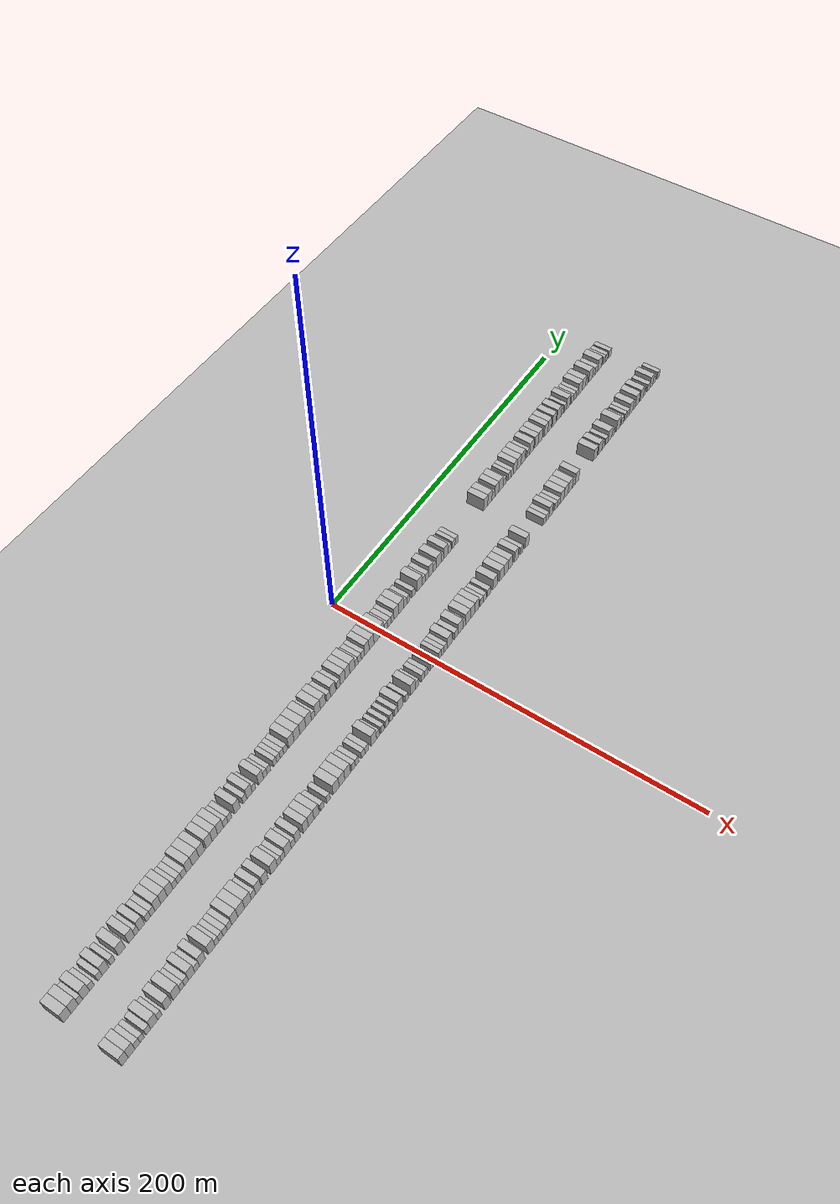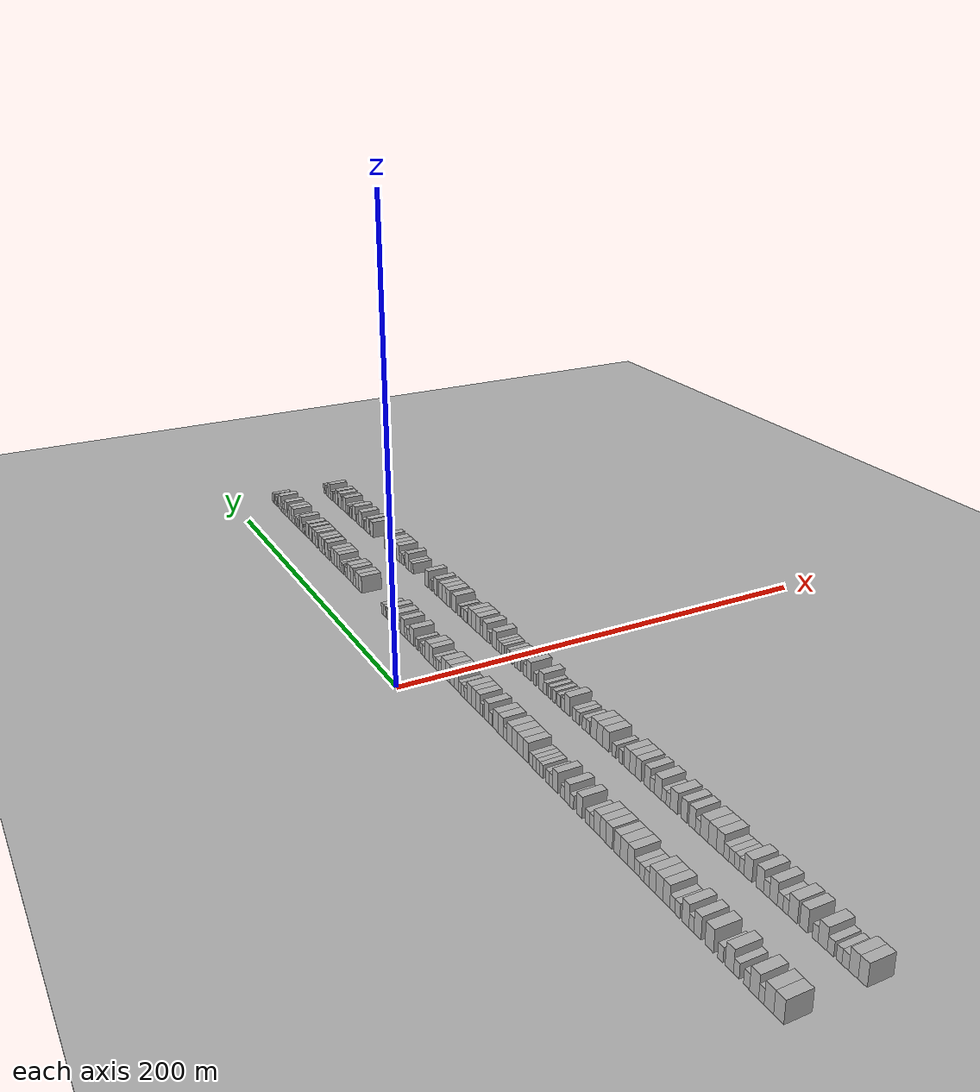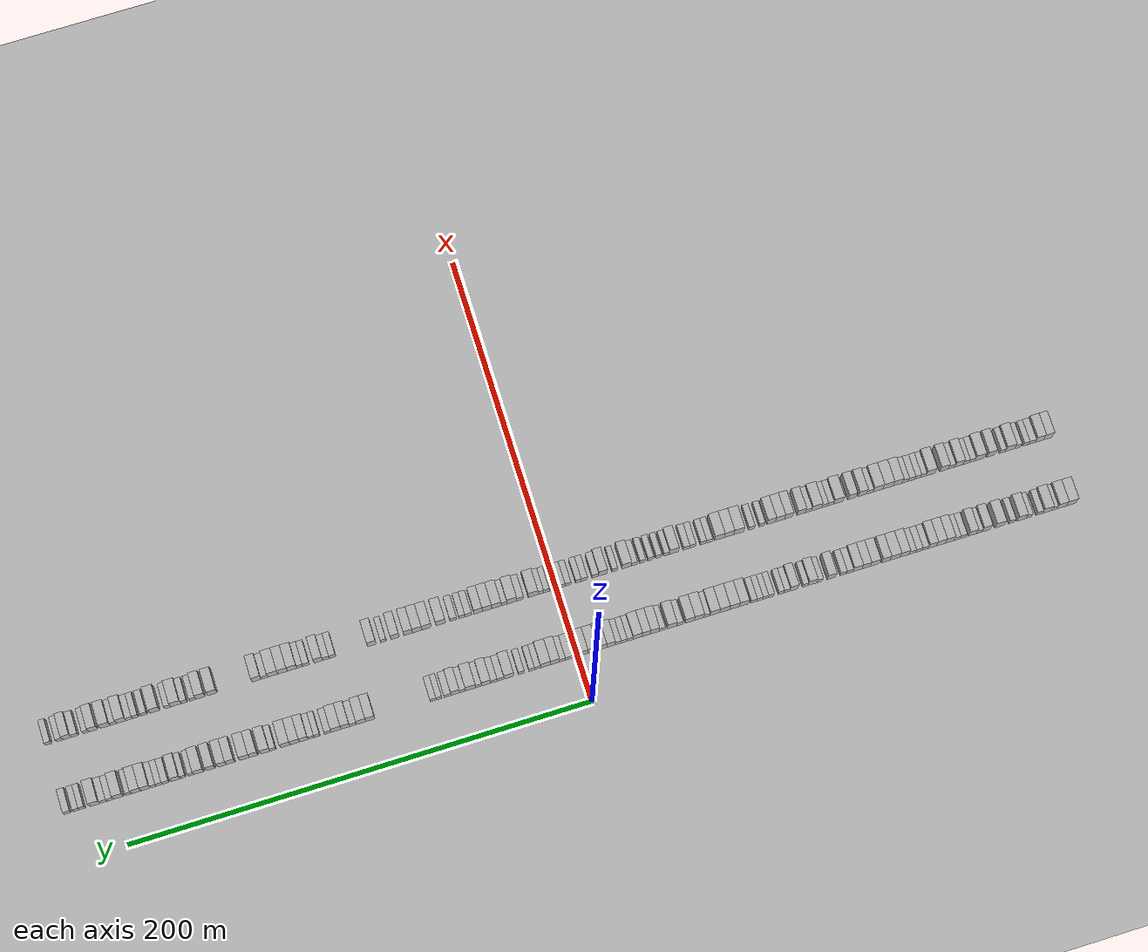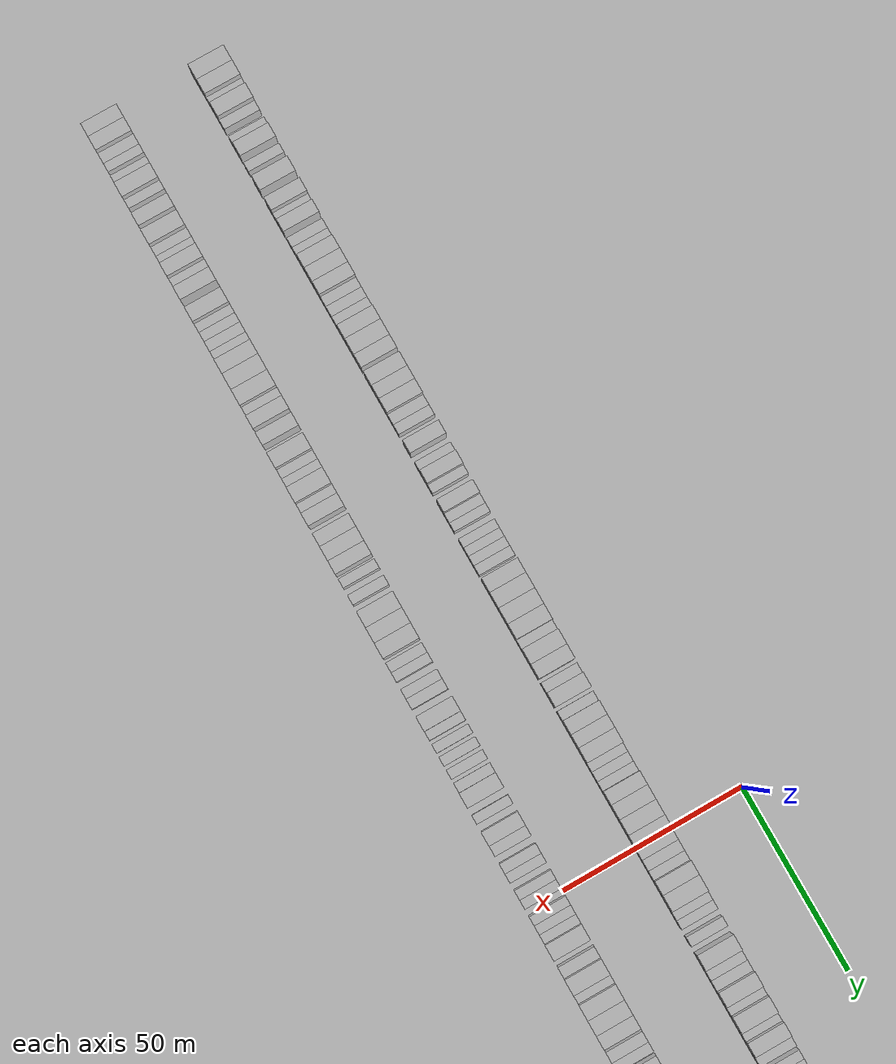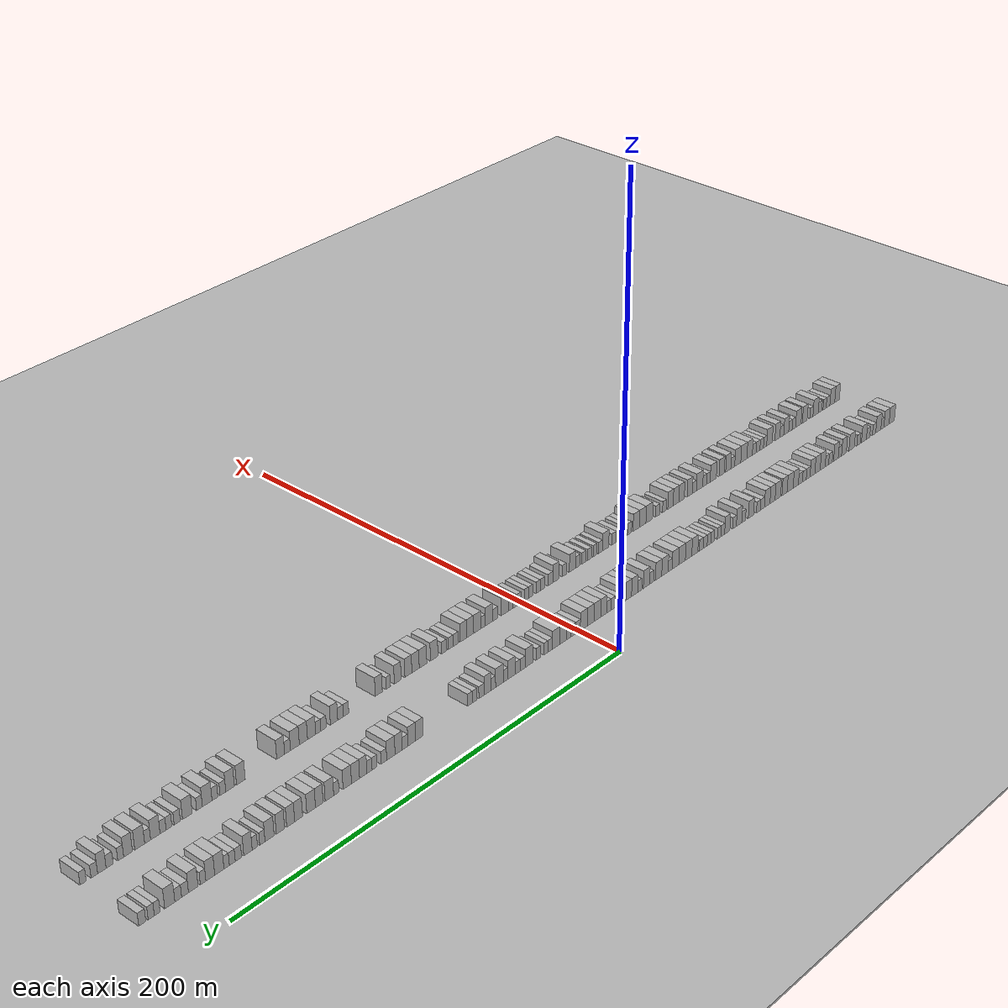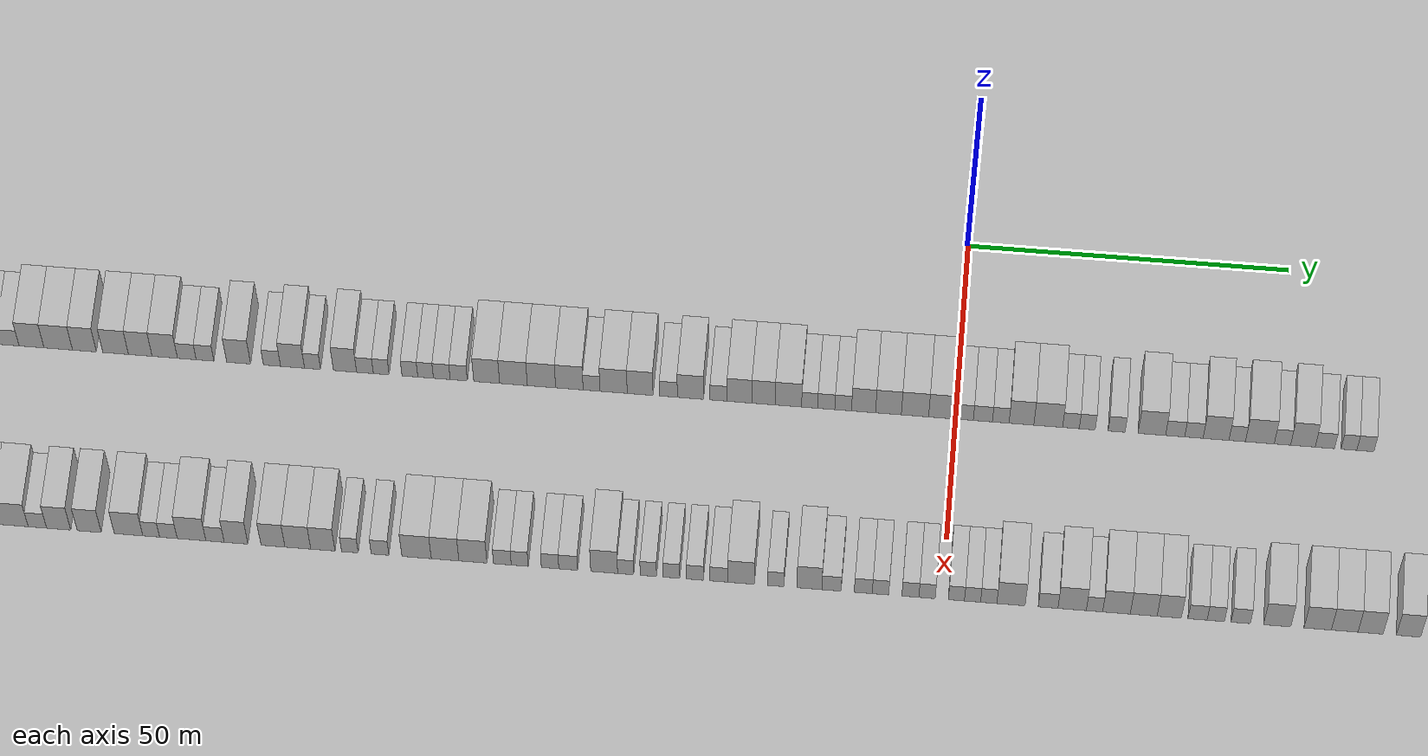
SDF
<?xml version="1.0" encoding="utf-8"?>

<sdf version="1.6">

   <world name="default">

      <gui fullscreen="0">

         <camera name="user_camera">

            <pose>-15 0 4.57585 0 0 0</pose>

            <view_controller>orbit</view_controller>

         </camera>

      </gui>

      <scene>

         <sky>

           <clouds>

             <speed>12</speed>

           </clouds>

         </sky>

         <ambient>0.4 0.4 0.4 1</ambient>

         <background>0.7 0.7 0.7 1</background>

         <shadows>1</shadows>

      </scene>

      <gravity>0 0 -9.8066</gravity>

      <magnetic_field>6e-06 2.3e-05 -4.2e-05</magnetic_field>

      <physics default="0" name="default_physics" type="ode">

         <ode>

            <solver>

               <type>quick</type>

               <iters>10</iters>

               <sor>1.0</sor>

               <use_dynamic_moi_rescaling>0</use_dynamic_moi_rescaling>

            </solver>

            <constraints>

               <cfm>0</cfm>

               <erp>0.2</erp>

               <contact_max_correcting_vel>100</contact_max_correcting_vel>

               <contact_surface_layer>0.001</contact_surface_layer>

            </constraints>

         </ode>

         <max_step_size>0.004</max_step_size>

         <real_time_factor>1</real_time_factor>

         <real_time_update_rate>250</real_time_update_rate>

      </physics>

      <light name="sun" type="directional">

         <cast_shadows>1</cast_shadows>

         <pose>0 0 10 0 0 0</pose>

         <diffuse>0.8 0.8 0.8 1</diffuse>

         <specular>0.2 0.2 0.2 1</specular>

         <attenuation>

            <range>1000</range>

            <constant>0.9</constant>

            <linear>0.01</linear>

            <quadratic>0.001</quadratic>

         </attenuation>

         <direction>-0.5 0.1 -0.9</direction>

      </light>

      <include>

         <name>ground_plane_1</name>

         <uri>model://HANNAS_ground_plane</uri>

         <pose>0 0 0  0 0 0</pose>

      </include>

      <include>

         <name>ground_plane_2</name>

         <uri>model://HANNAS_ground_plane</uri>

         <pose>100 0 0  0 0 0</pose>

      </include>

      <model name="building_1">

         <static>1</static>

         <pose frame="">25.0000 -217.8196 0 0.000000 0.000000 0.000000</pose>

         <link name="link">

            <pose frame="">0 0 4.50 0 0 0</pose>

            <collision name="collision">

               <geometry>

                  <box>

                     <size>10.0000 4.3608 9.0000</size>

                  </box>

               </geometry>

               <max_contacts>10</max_contacts>

               <surface>

                  <contact>

                     <ode/>

                  </contact>

                  <bounce/>

                  <friction>

                     <torsional>

                        <ode/>

                     </torsional>

                     <ode/>

                  </friction>

               </surface>

            </collision>

            <visual name="visual">

               <cast_shadows>0</cast_shadows>

               <geometry>

                  <box>

                     <size>10.0000 4.3608 9.0000</size>

                  </box>

               </geometry>

               <material>

                  <script>

                     <uri>model://HANNAS_wall/materials/scripts</uri>

                     <uri>model://HANNAS_wall/materials/textures</uri>

                     <name>vrc/HANNAS_wall</name>

                  </script>

               </material>

            </visual>

            <self_collide>0</self_collide>

            <enable_wind>0</enable_wind>

            <kinematic>0</kinematic>

         </link>

      </model>

      <model name="building_2">

         <static>1</static>

         <pose frame="">25.0000 -213.5517 0 0.000000 0.000000 0.000000</pose>

         <link name="link">

            <pose frame="">0 0 4.50 0 0 0</pose>

            <collision name="collision">

               <geometry>

                  <box>

                     <size>10.0000 4.1750 9.0000</size>

                  </box>

               </geometry>

               <max_contacts>10</max_contacts>

               <surface>

                  <contact>

                     <ode/>

                  </contact>

                  <bounce/>

                  <friction>

                     <torsional>

                        <ode/>

                     </torsional>

                     <ode/>

                  </friction>

               </surface>

            </collision>

            <visual name="visual">

               <cast_shadows>0</cast_shadows>

               <geometry>

                  <box>

                     <size>10.0000 4.1750 9.0000</size>

                  </box>

               </geometry>

               <material>

                  <script>

                     <uri>model://HANNAS_wall/materials/scripts</uri>

                     <uri>model://HANNAS_wall/materials/textures</uri>

                     <name>vrc/HANNAS_wall</name>

                  </script>

               </material>

            </visual>

            <self_collide>0</self_collide>

            <enable_wind>0</enable_wind>

            <kinematic>0</kinematic>

         </link>

      </model>

      <model name="building_3">

         <static>1</static>

         <pose frame="">25.0000 -210.2575 0 0.000000 0.000000 0.000000</pose>

         <link name="link">

            <pose frame="">0 0 3.00 0 0 0</pose>

            <collision name="collision">

               <geometry>

                  <box>

                     <size>10.0000 2.4133 6.0000</size>

                  </box>

               </geometry>

               <max_contacts>10</max_contacts>

               <surface>

                  <contact>

                     <ode/>

                  </contact>

                  <bounce/>

                  <friction>

                     <torsional>

                        <ode/>

                     </torsional>

                     <ode/>

                  </friction>

               </surface>

            </collision>

            <visual name="visual">

               <cast_shadows>0</cast_shadows>

               <geometry>

                  <box>

                     <size>10.0000 2.4133 6.0000</size>

                  </box>

               </geometry>

               <material>

                  <script>

                     <uri>model://HANNAS_wall/materials/scripts</uri>

                     <uri>model://HANNAS_wall/materials/textures</uri>

                     <name>vrc/HANNAS_wall</name>

                  </script>

               </material>

            </visual>

            <self_collide>0</self_collide>

            <enable_wind>0</enable_wind>

            <kinematic>0</kinematic>

         </link>

      </model>

      <model name="building_4">

         <static>1</static>

         <pose frame="">25.0000 -206.9874 0 0.000000 0.000000 0.000000</pose>

         <link name="link">

            <pose frame="">0 0 4.50 0 0 0</pose>

            <collision name="collision">

               <geometry>

                  <box>

                     <size>10.0000 4.1270 9.0000</size>

                  </box>

               </geometry>

               <max_contacts>10</max_contacts>

               <surface>

                  <contact>

                     <ode/>

                  </contact>

                  <bounce/>

                  <friction>

                     <torsional>

                        <ode/>

                     </torsional>

                     <ode/>

                  </friction>

               </surface>

            </collision>

            <visual name="visual">

               <cast_shadows>0</cast_shadows>

               <geometry>

                  <box>

                     <size>10.0000 4.1270 9.0000</size>

                  </box>

               </geometry>

               <material>

                  <script>

                     <uri>model://HANNAS_wall/materials/scripts</uri>

                     <uri>model://HANNAS_wall/materials/textures</uri>

                     <name>vrc/HANNAS_wall</name>

                  </script>

               </material>

            </visual>

            <self_collide>0</self_collide>

            <enable_wind>0</enable_wind>

            <kinematic>0</kinematic>

         </link>

      </model>

      <model name="building_5">

         <static>1</static>

         <pose frame="">25.0000 -203.5547 0 0.000000 0.000000 0.000000</pose>

         <link name="link">

            <pose frame="">0 0 3.00 0 0 0</pose>

            <collision name="collision">

               <geometry>

                  <box>

                     <size>10.0000 2.7383 6.0000</size>

                  </box>

               </geometry>

               <max_contacts>10</max_contacts>

               <surface>

                  <contact>

                     <ode/>

                  </contact>

                  <bounce/>

                  <friction>

                     <torsional>

                        <ode/>

                     </torsional>

                     <ode/>

                  </friction>

               </surface>

            </collision>

            <visual name="visual">

               <cast_shadows>0</cast_shadows>

               <geometry>

                  <box>

                     <size>10.0000 2.7383 6.0000</size>

                  </box>

               </geometry>

               <material>

                  <script>

                     <uri>model://HANNAS_wall/materials/scripts</uri>

                     <uri>model://HANNAS_wall/materials/textures</uri>

                     <name>vrc/HANNAS_wall</name>

                  </script>

               </material>

            </visual>

            <self_collide>0</self_collide>

            <enable_wind>0</enable_wind>

            <kinematic>0</kinematic>

         </link>

      </model>

      <model name="building_6">

         <static>1</static>

         <pose frame="">25.0000 -198.8463 0 0.000000 0.000000 0.000000</pose>

         <link name="link">

            <pose frame="">0 0 3.00 0 0 0</pose>

            <collision name="collision">

               <geometry>

                  <box>

                     <size>10.0000 2.6786 6.0000</size>

                  </box>

               </geometry>

               <max_contacts>10</max_contacts>

               <surface>

                  <contact>

                     <ode/>

                  </contact>

                  <bounce/>

                  <friction>

                     <torsional>

                        <ode/>

                     </torsional>

                     <ode/>

                  </friction>

               </surface>

            </collision>

            <visual name="visual">

               <cast_shadows>0</cast_shadows>

               <geometry>

                  <box>

                     <size>10.0000 2.6786 6.0000</size>

                  </box>

               </geometry>

               <material>

                  <script>

                     <uri>model://HANNAS_wall/materials/scripts</uri>

                     <uri>model://HANNAS_wall/materials/textures</uri>

                     <name>vrc/HANNAS_wall</name>

                  </script>

               </material>

            </visual>

            <self_collide>0</self_collide>

            <enable_wind>0</enable_wind>

            <kinematic>0</kinematic>

         </link>

      </model>

      <model name="building_7">

         <static>1</static>

         <pose frame="">25.0000 -195.5430 0 0.000000 0.000000 0.000000</pose>

         <link name="link">

            <pose frame="">0 0 4.50 0 0 0</pose>

            <collision name="collision">

               <geometry>

                  <box>

                     <size>10.0000 3.9280 9.0000</size>

                  </box>

               </geometry>

               <max_contacts>10</max_contacts>

               <surface>

                  <contact>

                     <ode/>

                  </contact>

                  <bounce/>

                  <friction>

                     <torsional>

                        <ode/>

                     </torsional>

                     <ode/>

                  </friction>

               </surface>

            </collision>

            <visual name="visual">

               <cast_shadows>0</cast_shadows>

               <geometry>

                  <box>

                     <size>10.0000 3.9280 9.0000</size>

                  </box>

               </geometry>

               <material>

                  <script>

                     <uri>model://HANNAS_wall/materials/scripts</uri>

                     <uri>model://HANNAS_wall/materials/textures</uri>

                     <name>vrc/HANNAS_wall</name>

                  </script>

               </material>

            </visual>

            <self_collide>0</self_collide>

            <enable_wind>0</enable_wind>

            <kinematic>0</kinematic>

         </link>

      </model>

      <model name="building_8">

         <static>1</static>

         <pose frame="">25.0000 -191.2647 0 0.000000 0.000000 0.000000</pose>

         <link name="link">

            <pose frame="">0 0 3.00 0 0 0</pose>

            <collision name="collision">

               <geometry>

                  <box>

                     <size>10.0000 2.6285 6.0000</size>

                  </box>

               </geometry>

               <max_contacts>10</max_contacts>

               <surface>

                  <contact>

                     <ode/>

                  </contact>

                  <bounce/>

                  <friction>

                     <torsional>

                        <ode/>

                     </torsional>

                     <ode/>

                  </friction>

               </surface>

            </collision>

            <visual name="visual">

               <cast_shadows>0</cast_shadows>

               <geometry>

                  <box>

                     <size>10.0000 2.6285 6.0000</size>

                  </box>

               </geometry>

               <material>

                  <script>

                     <uri>model://HANNAS_wall/materials/scripts</uri>

                     <uri>model://HANNAS_wall/materials/textures</uri>

                     <name>vrc/HANNAS_wall</name>

                  </script>

               </material>

            </visual>

            <self_collide>0</self_collide>

            <enable_wind>0</enable_wind>

            <kinematic>0</kinematic>

         </link>

      </model>

      <model name="building_9">

         <static>1</static>

         <pose frame="">25.0000 -185.8397 0 0.000000 0.000000 0.000000</pose>

         <link name="link">

            <pose frame="">0 0 4.50 0 0 0</pose>

            <collision name="collision">

               <geometry>

                  <box>

                     <size>10.0000 4.2216 9.0000</size>

                  </box>

               </geometry>

               <max_contacts>10</max_contacts>

               <surface>

                  <contact>

                     <ode/>

                  </contact>

                  <bounce/>

                  <friction>

                     <torsional>

                        <ode/>

                     </torsional>

                     <ode/>

                  </friction>

               </surface>

            </collision>

            <visual name="visual">

               <cast_shadows>0</cast_shadows>

               <geometry>

                  <box>

                     <size>10.0000 4.2216 9.0000</size>

                  </box>

               </geometry>

               <material>

                  <script>

                     <uri>model://HANNAS_wall/materials/scripts</uri>

                     <uri>model://HANNAS_wall/materials/textures</uri>

                     <name>vrc/HANNAS_wall</name>

                  </script>

               </material>

            </visual>

            <self_collide>0</self_collide>

            <enable_wind>0</enable_wind>

            <kinematic>0</kinematic>

         </link>

      </model>

      <model name="building_10">

         <static>1</static>

         <pose frame="">25.0000 -179.8683 0 0.000000 0.000000 0.000000</pose>

         <link name="link">

            <pose frame="">0 0 4.50 0 0 0</pose>

            <collision name="collision">

               <geometry>

                  <box>

                     <size>10.0000 3.7211 9.0000</size>

                  </box>

               </geometry>

               <max_contacts>10</max_contacts>

               <surface>

                  <contact>

                     <ode/>

                  </contact>

                  <bounce/>

                  <friction>

                     <torsional>

                        <ode/>

                     </torsional>

                     <ode/>

                  </friction>

               </surface>

            </collision>

            <visual name="visual">

               <cast_shadows>0</cast_shadows>

               <geometry>

                  <box>

                     <size>10.0000 3.7211 9.0000</size>

                  </box>

               </geometry>

               <material>

                  <script>

                     <uri>model://HANNAS_wall/materials/scripts</uri>

                     <uri>model://HANNAS_wall/materials/textures</uri>

                     <name>vrc/HANNAS_wall</name>

                  </script>

               </material>

            </visual>

            <self_collide>0</self_collide>

            <enable_wind>0</enable_wind>

            <kinematic>0</kinematic>

         </link>

      </model>

      <model name="building_11">

         <static>1</static>

         <pose frame="">25.0000 -176.7563 0 0.000000 0.000000 0.000000</pose>

         <link name="link">

            <pose frame="">0 0 3.00 0 0 0</pose>

            <collision name="collision">

               <geometry>

                  <box>

                     <size>10.0000 2.5028 6.0000</size>

                  </box>

               </geometry>

               <max_contacts>10</max_contacts>

               <surface>

                  <contact>

                     <ode/>

                  </contact>

                  <bounce/>

                  <friction>

                     <torsional>

                        <ode/>

                     </torsional>

                     <ode/>

                  </friction>

               </surface>

            </collision>

            <visual name="visual">

               <cast_shadows>0</cast_shadows>

               <geometry>

                  <box>

                     <size>10.0000 2.5028 6.0000</size>

                  </box>

               </geometry>

               <material>

                  <script>

                     <uri>model://HANNAS_wall/materials/scripts</uri>

                     <uri>model://HANNAS_wall/materials/textures</uri>

                     <name>vrc/HANNAS_wall</name>

                  </script>

               </material>

            </visual>

            <self_collide>0</self_collide>

            <enable_wind>0</enable_wind>

            <kinematic>0</kinematic>

         </link>

      </model>

      <model name="building_12">

         <static>1</static>

         <pose frame="">25.0000 -173.7009 0 0.000000 0.000000 0.000000</pose>

         <link name="link">

            <pose frame="">0 0 4.50 0 0 0</pose>

            <collision name="collision">

               <geometry>

                  <box>

                     <size>10.0000 3.6080 9.0000</size>

                  </box>

               </geometry>

               <max_contacts>10</max_contacts>

               <surface>

                  <contact>

                     <ode/>

                  </contact>

                  <bounce/>

                  <friction>

                     <torsional>

                        <ode/>

                     </torsional>

                     <ode/>

                  </friction>

               </surface>

            </collision>

            <visual name="visual">

               <cast_shadows>0</cast_shadows>

               <geometry>

                  <box>

                     <size>10.0000 3.6080 9.0000</size>

                  </box>

               </geometry>

               <material>

                  <script>

                     <uri>model://HANNAS_wall/materials/scripts</uri>

                     <uri>model://HANNAS_wall/materials/textures</uri>

                     <name>vrc/HANNAS_wall</name>

                  </script>

               </material>

            </visual>

            <self_collide>0</self_collide>

            <enable_wind>0</enable_wind>

            <kinematic>0</kinematic>

         </link>

      </model>

      <model name="building_13">

         <static>1</static>

         <pose frame="">25.0000 -169.5221 0 0.000000 0.000000 0.000000</pose>

         <link name="link">

            <pose frame="">0 0 3.00 0 0 0</pose>

            <collision name="collision">

               <geometry>

                  <box>

                     <size>10.0000 2.7497 6.0000</size>

                  </box>

               </geometry>

               <max_contacts>10</max_contacts>

               <surface>

                  <contact>

                     <ode/>

                  </contact>

                  <bounce/>

                  <friction>

                     <torsional>

                        <ode/>

                     </torsional>

                     <ode/>

                  </friction>

               </surface>

            </collision>

            <visual name="visual">

               <cast_shadows>0</cast_shadows>

               <geometry>

                  <box>

                     <size>10.0000 2.7497 6.0000</size>

                  </box>

               </geometry>

               <material>

                  <script>

                     <uri>model://HANNAS_wall/materials/scripts</uri>

                     <uri>model://HANNAS_wall/materials/textures</uri>

                     <name>vrc/HANNAS_wall</name>

                  </script>

               </material>

            </visual>

            <self_collide>0</self_collide>

            <enable_wind>0</enable_wind>

            <kinematic>0</kinematic>

         </link>

      </model>

      <model name="building_14">

         <static>1</static>

         <pose frame="">25.0000 -166.7844 0 0.000000 0.000000 0.000000</pose>

         <link name="link">

            <pose frame="">0 0 3.00 0 0 0</pose>

            <collision name="collision">

               <geometry>

                  <box>

                     <size>10.0000 2.7257 6.0000</size>

                  </box>

               </geometry>

               <max_contacts>10</max_contacts>

               <surface>

                  <contact>

                     <ode/>

                  </contact>

                  <bounce/>

                  <friction>

                     <torsional>

                        <ode/>

                     </torsional>

                     <ode/>

                  </friction>

               </surface>

            </collision>

            <visual name="visual">

               <cast_shadows>0</cast_shadows>

               <geometry>

                  <box>

                     <size>10.0000 2.7257 6.0000</size>

                  </box>

               </geometry>

               <material>

                  <script>

                     <uri>model://HANNAS_wall/materials/scripts</uri>

                     <uri>model://HANNAS_wall/materials/textures</uri>

                     <name>vrc/HANNAS_wall</name>

                  </script>

               </material>

            </visual>

            <self_collide>0</self_collide>

            <enable_wind>0</enable_wind>

            <kinematic>0</kinematic>

         </link>

      </model>

      <model name="building_15">

         <static>1</static>

         <pose frame="">25.0000 -163.5337 0 0.000000 0.000000 0.000000</pose>

         <link name="link">

            <pose frame="">0 0 4.50 0 0 0</pose>

            <collision name="collision">

               <geometry>

                  <box>

                     <size>10.0000 3.7757 9.0000</size>

                  </box>

               </geometry>

               <max_contacts>10</max_contacts>

               <surface>

                  <contact>

                     <ode/>

                  </contact>

                  <bounce/>

                  <friction>

                     <torsional>

                        <ode/>

                     </torsional>

                     <ode/>

                  </friction>

               </surface>

            </collision>

            <visual name="visual">

               <cast_shadows>0</cast_shadows>

               <geometry>

                  <box>

                     <size>10.0000 3.7757 9.0000</size>

                  </box>

               </geometry>

               <material>

                  <script>

                     <uri>model://HANNAS_wall/materials/scripts</uri>

                     <uri>model://HANNAS_wall/materials/textures</uri>

                     <name>vrc/HANNAS_wall</name>

                  </script>

               </material>

            </visual>

            <self_collide>0</self_collide>

            <enable_wind>0</enable_wind>

            <kinematic>0</kinematic>

         </link>

      </model>

      <model name="building_16">

         <static>1</static>

         <pose frame="">25.0000 -159.6657 0 0.000000 0.000000 0.000000</pose>

         <link name="link">

            <pose frame="">0 0 4.50 0 0 0</pose>

            <collision name="collision">

               <geometry>

                  <box>

                     <size>10.0000 3.9602 9.0000</size>

                  </box>

               </geometry>

               <max_contacts>10</max_contacts>

               <surface>

                  <contact>

                     <ode/>

                  </contact>

                  <bounce/>

                  <friction>

                     <torsional>

                        <ode/>

                     </torsional>

                     <ode/>

                  </friction>

               </surface>

            </collision>

            <visual name="visual">

               <cast_shadows>0</cast_shadows>

               <geometry>

                  <box>

                     <size>10.0000 3.9602 9.0000</size>

                  </box>

               </geometry>

               <material>

                  <script>

                     <uri>model://HANNAS_wall/materials/scripts</uri>

                     <uri>model://HANNAS_wall/materials/textures</uri>

                     <name>vrc/HANNAS_wall</name>

                  </script>

               </material>

            </visual>

            <self_collide>0</self_collide>

            <enable_wind>0</enable_wind>

            <kinematic>0</kinematic>

         </link>

      </model>

      <model name="building_17">

         <static>1</static>

         <pose frame="">25.0000 -155.8524 0 0.000000 0.000000 0.000000</pose>

         <link name="link">

            <pose frame="">0 0 4.50 0 0 0</pose>

            <collision name="collision">

               <geometry>

                  <box>

                     <size>10.0000 3.6663 9.0000</size>

                  </box>

               </geometry>

               <max_contacts>10</max_contacts>

               <surface>

                  <contact>

                     <ode/>

                  </contact>

                  <bounce/>

                  <friction>

                     <torsional>

                        <ode/>

                     </torsional>

                     <ode/>

                  </friction>

               </surface>

            </collision>

            <visual name="visual">

               <cast_shadows>0</cast_shadows>

               <geometry>

                  <box>

                     <size>10.0000 3.6663 9.0000</size>

                  </box>

               </geometry>

               <material>

                  <script>

                     <uri>model://HANNAS_wall/materials/scripts</uri>

                     <uri>model://HANNAS_wall/materials/textures</uri>

                     <name>vrc/HANNAS_wall</name>

                  </script>

               </material>

            </visual>

            <self_collide>0</self_collide>

            <enable_wind>0</enable_wind>

            <kinematic>0</kinematic>

         </link>

      </model>

      <model name="building_18">

         <static>1</static>

         <pose frame="">25.0000 -152.6347 0 0.000000 0.000000 0.000000</pose>

         <link name="link">

            <pose frame="">0 0 3.00 0 0 0</pose>

            <collision name="collision">

               <geometry>

                  <box>

                     <size>10.0000 2.7692 6.0000</size>

                  </box>

               </geometry>

               <max_contacts>10</max_contacts>

               <surface>

                  <contact>

                     <ode/>

                  </contact>

                  <bounce/>

                  <friction>

                     <torsional>

                        <ode/>

                     </torsional>

                     <ode/>

                  </friction>

               </surface>

            </collision>

            <visual name="visual">

               <cast_shadows>0</cast_shadows>

               <geometry>

                  <box>

                     <size>10.0000 2.7692 6.0000</size>

                  </box>

               </geometry>

               <material>

                  <script>

                     <uri>model://HANNAS_wall/materials/scripts</uri>

                     <uri>model://HANNAS_wall/materials/textures</uri>

                     <name>vrc/HANNAS_wall</name>

                  </script>

               </material>

            </visual>

            <self_collide>0</self_collide>

            <enable_wind>0</enable_wind>

            <kinematic>0</kinematic>

         </link>

      </model>

      <model name="building_19">

         <static>1</static>

         <pose frame="">25.0000 -149.8208 0 0.000000 0.000000 0.000000</pose>

         <link name="link">

            <pose frame="">0 0 3.00 0 0 0</pose>

            <collision name="collision">

               <geometry>

                  <box>

                     <size>10.0000 2.8584 6.0000</size>

                  </box>

               </geometry>

               <max_contacts>10</max_contacts>

               <surface>

                  <contact>

                     <ode/>

                  </contact>

                  <bounce/>

                  <friction>

                     <torsional>

                        <ode/>

                     </torsional>

                     <ode/>

                  </friction>

               </surface>

            </collision>

            <visual name="visual">

               <cast_shadows>0</cast_shadows>

               <geometry>

                  <box>

                     <size>10.0000 2.8584 6.0000</size>

                  </box>

               </geometry>

               <material>

                  <script>

                     <uri>model://HANNAS_wall/materials/scripts</uri>

                     <uri>model://HANNAS_wall/materials/textures</uri>

                     <name>vrc/HANNAS_wall</name>

                  </script>

               </material>

            </visual>

            <self_collide>0</self_collide>

            <enable_wind>0</enable_wind>

            <kinematic>0</kinematic>

         </link>

      </model>

      <model name="building_20">

         <static>1</static>

         <pose frame="">25.0000 -146.8978 0 0.000000 0.000000 0.000000</pose>

         <link name="link">

            <pose frame="">0 0 3.00 0 0 0</pose>

            <collision name="collision">

               <geometry>

                  <box>

                     <size>10.0000 2.9875 6.0000</size>

                  </box>

               </geometry>

               <max_contacts>10</max_contacts>

               <surface>

                  <contact>

                     <ode/>

                  </contact>

                  <bounce/>

                  <friction>

                     <torsional>

                        <ode/>

                     </torsional>

                     <ode/>

                  </friction>

               </surface>

            </collision>

            <visual name="visual">

               <cast_shadows>0</cast_shadows>

               <geometry>

                  <box>

                     <size>10.0000 2.9875 6.0000</size>

                  </box>

               </geometry>

               <material>

                  <script>

                     <uri>model://HANNAS_wall/materials/scripts</uri>

                     <uri>model://HANNAS_wall/materials/textures</uri>

                     <name>vrc/HANNAS_wall</name>

                  </script>

               </material>

            </visual>

            <self_collide>0</self_collide>

            <enable_wind>0</enable_wind>

            <kinematic>0</kinematic>

         </link>

      </model>

      <model name="building_21">

         <static>1</static>

         <pose frame="">25.0000 -143.4549 0 0.000000 0.000000 0.000000</pose>

         <link name="link">

            <pose frame="">0 0 4.50 0 0 0</pose>

            <collision name="collision">

               <geometry>

                  <box>

                     <size>10.0000 3.8983 9.0000</size>

                  </box>

               </geometry>

               <max_contacts>10</max_contacts>

               <surface>

                  <contact>

                     <ode/>

                  </contact>

                  <bounce/>

                  <friction>

                     <torsional>

                        <ode/>

                     </torsional>

                     <ode/>

                  </friction>

               </surface>

            </collision>

            <visual name="visual">

               <cast_shadows>0</cast_shadows>

               <geometry>

                  <box>

                     <size>10.0000 3.8983 9.0000</size>

                  </box>

               </geometry>

               <material>

                  <script>

                     <uri>model://HANNAS_wall/materials/scripts</uri>

                     <uri>model://HANNAS_wall/materials/textures</uri>

                     <name>vrc/HANNAS_wall</name>

                  </script>

               </material>

            </visual>

            <self_collide>0</self_collide>

            <enable_wind>0</enable_wind>

            <kinematic>0</kinematic>

         </link>

      </model>

      <model name="building_22">

         <static>1</static>

         <pose frame="">25.0000 -139.2806 0 0.000000 0.000000 0.000000</pose>

         <link name="link">

            <pose frame="">0 0 4.50 0 0 0</pose>

            <collision name="collision">

               <geometry>

                  <box>

                     <size>10.0000 4.4503 9.0000</size>

                  </box>

               </geometry>

               <max_contacts>10</max_contacts>

               <surface>

                  <contact>

                     <ode/>

                  </contact>

                  <bounce/>

                  <friction>

                     <torsional>

                        <ode/>

                     </torsional>

                     <ode/>

                  </friction>

               </surface>

            </collision>

            <visual name="visual">

               <cast_shadows>0</cast_shadows>

               <geometry>

                  <box>

                     <size>10.0000 4.4503 9.0000</size>

                  </box>

               </geometry>

               <material>

                  <script>

                     <uri>model://HANNAS_wall/materials/scripts</uri>

                     <uri>model://HANNAS_wall/materials/textures</uri>

                     <name>vrc/HANNAS_wall</name>

                  </script>

               </material>

            </visual>

            <self_collide>0</self_collide>

            <enable_wind>0</enable_wind>

            <kinematic>0</kinematic>

         </link>

      </model>

      <model name="building_23">

         <static>1</static>

         <pose frame="">25.0000 -135.1921 0 0.000000 0.000000 0.000000</pose>

         <link name="link">

            <pose frame="">0 0 4.50 0 0 0</pose>

            <collision name="collision">

               <geometry>

                  <box>

                     <size>10.0000 3.7267 9.0000</size>

                  </box>

               </geometry>

               <max_contacts>10</max_contacts>

               <surface>

                  <contact>

                     <ode/>

                  </contact>

                  <bounce/>

                  <friction>

                     <torsional>

                        <ode/>

                     </torsional>

                     <ode/>

                  </friction>

               </surface>

            </collision>

            <visual name="visual">

               <cast_shadows>0</cast_shadows>

               <geometry>

                  <box>

                     <size>10.0000 3.7267 9.0000</size>

                  </box>

               </geometry>

               <material>

                  <script>

                     <uri>model://HANNAS_wall/materials/scripts</uri>

                     <uri>model://HANNAS_wall/materials/textures</uri>

                     <name>vrc/HANNAS_wall</name>

                  </script>

               </material>

            </visual>

            <self_collide>0</self_collide>

            <enable_wind>0</enable_wind>

            <kinematic>0</kinematic>

         </link>

      </model>

      <model name="building_24">

         <static>1</static>

         <pose frame="">25.0000 -130.3292 0 0.000000 0.000000 0.000000</pose>

         <link name="link">

            <pose frame="">0 0 4.50 0 0 0</pose>

            <collision name="collision">

               <geometry>

                  <box>

                     <size>10.0000 3.9993 9.0000</size>

                  </box>

               </geometry>

               <max_contacts>10</max_contacts>

               <surface>

                  <contact>

                     <ode/>

                  </contact>

                  <bounce/>

                  <friction>

                     <torsional>

                        <ode/>

                     </torsional>

                     <ode/>

                  </friction>

               </surface>

            </collision>

            <visual name="visual">

               <cast_shadows>0</cast_shadows>

               <geometry>

                  <box>

                     <size>10.0000 3.9993 9.0000</size>

                  </box>

               </geometry>

               <material>

                  <script>

                     <uri>model://HANNAS_wall/materials/scripts</uri>

                     <uri>model://HANNAS_wall/materials/textures</uri>

                     <name>vrc/HANNAS_wall</name>

                  </script>

               </material>

            </visual>

            <self_collide>0</self_collide>

            <enable_wind>0</enable_wind>

            <kinematic>0</kinematic>

         </link>

      </model>

      <model name="building_25">

         <static>1</static>

         <pose frame="">25.0000 -126.4850 0 0.000000 0.000000 0.000000</pose>

         <link name="link">

            <pose frame="">0 0 4.50 0 0 0</pose>

            <collision name="collision">

               <geometry>

                  <box>

                     <size>10.0000 3.6889 9.0000</size>

                  </box>

               </geometry>

               <max_contacts>10</max_contacts>

               <surface>

                  <contact>

                     <ode/>

                  </contact>

                  <bounce/>

                  <friction>

                     <torsional>

                        <ode/>

                     </torsional>

                     <ode/>

                  </friction>

               </surface>

            </collision>

            <visual name="visual">

               <cast_shadows>0</cast_shadows>

               <geometry>

                  <box>

                     <size>10.0000 3.6889 9.0000</size>

                  </box>

               </geometry>

               <material>

                  <script>

                     <uri>model://HANNAS_wall/materials/scripts</uri>

                     <uri>model://HANNAS_wall/materials/textures</uri>

                     <name>vrc/HANNAS_wall</name>

                  </script>

               </material>

            </visual>

            <self_collide>0</self_collide>

            <enable_wind>0</enable_wind>

            <kinematic>0</kinematic>

         </link>

      </model>

      <model name="building_26">

         <static>1</static>

         <pose frame="">25.0000 -122.6593 0 0.000000 0.000000 0.000000</pose>

         <link name="link">

            <pose frame="">0 0 4.50 0 0 0</pose>

            <collision name="collision">

               <geometry>

                  <box>

                     <size>10.0000 3.9626 9.0000</size>

                  </box>

               </geometry>

               <max_contacts>10</max_contacts>

               <surface>

                  <contact>

                     <ode/>

                  </contact>

                  <bounce/>

                  <friction>

                     <torsional>

                        <ode/>

                     </torsional>

                     <ode/>

                  </friction>

               </surface>

            </collision>

            <visual name="visual">

               <cast_shadows>0</cast_shadows>

               <geometry>

                  <box>

                     <size>10.0000 3.9626 9.0000</size>

                  </box>

               </geometry>

               <material>

                  <script>

                     <uri>model://HANNAS_wall/materials/scripts</uri>

                     <uri>model://HANNAS_wall/materials/textures</uri>

                     <name>vrc/HANNAS_wall</name>

                  </script>

               </material>

            </visual>

            <self_collide>0</self_collide>

            <enable_wind>0</enable_wind>

            <kinematic>0</kinematic>

         </link>

      </model>

      <model name="building_27">

         <static>1</static>

         <pose frame="">25.0000 -119.2190 0 0.000000 0.000000 0.000000</pose>

         <link name="link">

            <pose frame="">0 0 3.00 0 0 0</pose>

            <collision name="collision">

               <geometry>

                  <box>

                     <size>10.0000 2.9181 6.0000</size>

                  </box>

               </geometry>

               <max_contacts>10</max_contacts>

               <surface>

                  <contact>

                     <ode/>

                  </contact>

                  <bounce/>

                  <friction>

                     <torsional>

                        <ode/>

                     </torsional>

                     <ode/>

                  </friction>

               </surface>

            </collision>

            <visual name="visual">

               <cast_shadows>0</cast_shadows>

               <geometry>

                  <box>

                     <size>10.0000 2.9181 6.0000</size>

                  </box>

               </geometry>

               <material>

                  <script>

                     <uri>model://HANNAS_wall/materials/scripts</uri>

                     <uri>model://HANNAS_wall/materials/textures</uri>

                     <name>vrc/HANNAS_wall</name>

                  </script>

               </material>

            </visual>

            <self_collide>0</self_collide>

            <enable_wind>0</enable_wind>

            <kinematic>0</kinematic>

         </link>

      </model>

      <model name="building_28">

         <static>1</static>

         <pose frame="">25.0000 -116.3828 0 0.000000 0.000000 0.000000</pose>

         <link name="link">

            <pose frame="">0 0 3.00 0 0 0</pose>

            <collision name="collision">

               <geometry>

                  <box>

                     <size>10.0000 2.7541 6.0000</size>

                  </box>

               </geometry>

               <max_contacts>10</max_contacts>

               <surface>

                  <contact>

                     <ode/>

                  </contact>

                  <bounce/>

                  <friction>

                     <torsional>

                        <ode/>

                     </torsional>

                     <ode/>

                  </friction>

               </surface>

            </collision>

            <visual name="visual">

               <cast_shadows>0</cast_shadows>

               <geometry>

                  <box>

                     <size>10.0000 2.7541 6.0000</size>

                  </box>

               </geometry>

               <material>

                  <script>

                     <uri>model://HANNAS_wall/materials/scripts</uri>

                     <uri>model://HANNAS_wall/materials/textures</uri>

                     <name>vrc/HANNAS_wall</name>

                  </script>

               </material>

            </visual>

            <self_collide>0</self_collide>

            <enable_wind>0</enable_wind>

            <kinematic>0</kinematic>

         </link>

      </model>

      <model name="building_29">

         <static>1</static>

         <pose frame="">25.0000 -111.1421 0 0.000000 0.000000 0.000000</pose>

         <link name="link">

            <pose frame="">0 0 4.50 0 0 0</pose>

            <collision name="collision">

               <geometry>

                  <box>

                     <size>10.0000 3.7273 9.0000</size>

                  </box>

               </geometry>

               <max_contacts>10</max_contacts>

               <surface>

                  <contact>

                     <ode/>

                  </contact>

                  <bounce/>

                  <friction>

                     <torsional>

                        <ode/>

                     </torsional>

                     <ode/>

                  </friction>

               </surface>

            </collision>

            <visual name="visual">

               <cast_shadows>0</cast_shadows>

               <geometry>

                  <box>

                     <size>10.0000 3.7273 9.0000</size>

                  </box>

               </geometry>

               <material>

                  <script>

                     <uri>model://HANNAS_wall/materials/scripts</uri>

                     <uri>model://HANNAS_wall/materials/textures</uri>

                     <name>vrc/HANNAS_wall</name>

                  </script>

               </material>

            </visual>

            <self_collide>0</self_collide>

            <enable_wind>0</enable_wind>

            <kinematic>0</kinematic>

         </link>

      </model>

      <model name="building_30">

         <static>1</static>

         <pose frame="">25.0000 -105.9499 0 0.000000 0.000000 0.000000</pose>

         <link name="link">

            <pose frame="">0 0 3.00 0 0 0</pose>

            <collision name="collision">

               <geometry>

                  <box>

                     <size>10.0000 2.6573 6.0000</size>

                  </box>

               </geometry>

               <max_contacts>10</max_contacts>

               <surface>

                  <contact>

                     <ode/>

                  </contact>

                  <bounce/>

                  <friction>

                     <torsional>

                        <ode/>

                     </torsional>

                     <ode/>

                  </friction>

               </surface>

            </collision>

            <visual name="visual">

               <cast_shadows>0</cast_shadows>

               <geometry>

                  <box>

                     <size>10.0000 2.6573 6.0000</size>

                  </box>

               </geometry>

               <material>

                  <script>

                     <uri>model://HANNAS_wall/materials/scripts</uri>

                     <uri>model://HANNAS_wall/materials/textures</uri>

                     <name>vrc/HANNAS_wall</name>

                  </script>

               </material>

            </visual>

            <self_collide>0</self_collide>

            <enable_wind>0</enable_wind>

            <kinematic>0</kinematic>

         </link>

      </model>

      <model name="building_31">

         <static>1</static>

         <pose frame="">25.0000 -102.7578 0 0.000000 0.000000 0.000000</pose>

         <link name="link">

            <pose frame="">0 0 4.50 0 0 0</pose>

            <collision name="collision">

               <geometry>

                  <box>

                     <size>10.0000 3.7269 9.0000</size>

                  </box>

               </geometry>

               <max_contacts>10</max_contacts>

               <surface>

                  <contact>

                     <ode/>

                  </contact>

                  <bounce/>

                  <friction>

                     <torsional>

                        <ode/>

                     </torsional>

                     <ode/>

                  </friction>

               </surface>

            </collision>

            <visual name="visual">

               <cast_shadows>0</cast_shadows>

               <geometry>

                  <box>

                     <size>10.0000 3.7269 9.0000</size>

                  </box>

               </geometry>

               <material>

                  <script>

                     <uri>model://HANNAS_wall/materials/scripts</uri>

                     <uri>model://HANNAS_wall/materials/textures</uri>

                     <name>vrc/HANNAS_wall</name>

                  </script>

               </material>

            </visual>

            <self_collide>0</self_collide>

            <enable_wind>0</enable_wind>

            <kinematic>0</kinematic>

         </link>

      </model>

      <model name="building_32">

         <static>1</static>

         <pose frame="">25.0000 -99.6385 0 0.000000 0.000000 0.000000</pose>

         <link name="link">

            <pose frame="">0 0 3.00 0 0 0</pose>

            <collision name="collision">

               <geometry>

                  <box>

                     <size>10.0000 2.5117 6.0000</size>

                  </box>

               </geometry>

               <max_contacts>10</max_contacts>

               <surface>

                  <contact>

                     <ode/>

                  </contact>

                  <bounce/>

                  <friction>

                     <torsional>

                        <ode/>

                     </torsional>

                     <ode/>

                  </friction>

               </surface>

            </collision>

            <visual name="visual">

               <cast_shadows>0</cast_shadows>

               <geometry>

                  <box>

                     <size>10.0000 2.5117 6.0000</size>

                  </box>

               </geometry>

               <material>

                  <script>

                     <uri>model://HANNAS_wall/materials/scripts</uri>

                     <uri>model://HANNAS_wall/materials/textures</uri>

                     <name>vrc/HANNAS_wall</name>

                  </script>

               </material>

            </visual>

            <self_collide>0</self_collide>

            <enable_wind>0</enable_wind>

            <kinematic>0</kinematic>

         </link>

      </model>

      <model name="building_33">

         <static>1</static>

         <pose frame="">25.0000 -94.5818 0 0.000000 0.000000 0.000000</pose>

         <link name="link">

            <pose frame="">0 0 4.50 0 0 0</pose>

            <collision name="collision">

               <geometry>

                  <box>

                     <size>10.0000 3.6016 9.0000</size>

                  </box>

               </geometry>

               <max_contacts>10</max_contacts>

               <surface>

                  <contact>

                     <ode/>

                  </contact>

                  <bounce/>

                  <friction>

                     <torsional>

                        <ode/>

                     </torsional>

                     <ode/>

                  </friction>

               </surface>

            </collision>

            <visual name="visual">

               <cast_shadows>0</cast_shadows>

               <geometry>

                  <box>

                     <size>10.0000 3.6016 9.0000</size>

                  </box>

               </geometry>

               <material>

                  <script>

                     <uri>model://HANNAS_wall/materials/scripts</uri>

                     <uri>model://HANNAS_wall/materials/textures</uri>

                     <name>vrc/HANNAS_wall</name>

                  </script>

               </material>

            </visual>

            <self_collide>0</self_collide>

            <enable_wind>0</enable_wind>

            <kinematic>0</kinematic>

         </link>

      </model>

      <model name="building_34">

         <static>1</static>

         <pose frame="">25.0000 -91.4817 0 0.000000 0.000000 0.000000</pose>

         <link name="link">

            <pose frame="">0 0 3.00 0 0 0</pose>

            <collision name="collision">

               <geometry>

                  <box>

                     <size>10.0000 2.5986 6.0000</size>

                  </box>

               </geometry>

               <max_contacts>10</max_contacts>

               <surface>

                  <contact>

                     <ode/>

                  </contact>

                  <bounce/>

                  <friction>

                     <torsional>

                        <ode/>

                     </torsional>

                     <ode/>

                  </friction>

               </surface>

            </collision>

            <visual name="visual">

               <cast_shadows>0</cast_shadows>

               <geometry>

                  <box>

                     <size>10.0000 2.5986 6.0000</size>

                  </box>

               </geometry>

               <material>

                  <script>

                     <uri>model://HANNAS_wall/materials/scripts</uri>

                     <uri>model://HANNAS_wall/materials/textures</uri>

                     <name>vrc/HANNAS_wall</name>

                  </script>

               </material>

            </visual>

            <self_collide>0</self_collide>

            <enable_wind>0</enable_wind>

            <kinematic>0</kinematic>

         </link>

      </model>

      <model name="building_35">

         <static>1</static>

         <pose frame="">25.0000 -88.9547 0 0.000000 0.000000 0.000000</pose>

         <link name="link">

            <pose frame="">0 0 3.00 0 0 0</pose>

            <collision name="collision">

               <geometry>

                  <box>

                     <size>10.0000 2.4553 6.0000</size>

                  </box>

               </geometry>

               <max_contacts>10</max_contacts>

               <surface>

                  <contact>

                     <ode/>

                  </contact>

                  <bounce/>

                  <friction>

                     <torsional>

                        <ode/>

                     </torsional>

                     <ode/>

                  </friction>

               </surface>

            </collision>

            <visual name="visual">

               <cast_shadows>0</cast_shadows>

               <geometry>

                  <box>

                     <size>10.0000 2.4553 6.0000</size>

                  </box>

               </geometry>

               <material>

                  <script>

                     <uri>model://HANNAS_wall/materials/scripts</uri>

                     <uri>model://HANNAS_wall/materials/textures</uri>

                     <name>vrc/HANNAS_wall</name>

                  </script>

               </material>

            </visual>

            <self_collide>0</self_collide>

            <enable_wind>0</enable_wind>

            <kinematic>0</kinematic>

         </link>

      </model>

      <model name="building_36">

         <static>1</static>

         <pose frame="">25.0000 -84.4982 0 0.000000 0.000000 0.000000</pose>

         <link name="link">

            <pose frame="">0 0 3.00 0 0 0</pose>

            <collision name="collision">

               <geometry>

                  <box>

                     <size>10.0000 2.4577 6.0000</size>

                  </box>

               </geometry>

               <max_contacts>10</max_contacts>

               <surface>

                  <contact>

                     <ode/>

                  </contact>

                  <bounce/>

                  <friction>

                     <torsional>

                        <ode/>

                     </torsional>

                     <ode/>

                  </friction>

               </surface>

            </collision>

            <visual name="visual">

               <cast_shadows>0</cast_shadows>

               <geometry>

                  <box>

                     <size>10.0000 2.4577 6.0000</size>

                  </box>

               </geometry>

               <material>

                  <script>

                     <uri>model://HANNAS_wall/materials/scripts</uri>

                     <uri>model://HANNAS_wall/materials/textures</uri>

                     <name>vrc/HANNAS_wall</name>

                  </script>

               </material>

            </visual>

            <self_collide>0</self_collide>

            <enable_wind>0</enable_wind>

            <kinematic>0</kinematic>

         </link>

      </model>

      <model name="building_37">

         <static>1</static>

         <pose frame="">25.0000 -82.0529 0 0.000000 0.000000 0.000000</pose>

         <link name="link">

            <pose frame="">0 0 3.00 0 0 0</pose>

            <collision name="collision">

               <geometry>

                  <box>

                     <size>10.0000 2.4330 6.0000</size>

                  </box>

               </geometry>

               <max_contacts>10</max_contacts>

               <surface>

                  <contact>

                     <ode/>

                  </contact>

                  <bounce/>

                  <friction>

                     <torsional>

                        <ode/>

                     </torsional>

                     <ode/>

                  </friction>

               </surface>

            </collision>

            <visual name="visual">

               <cast_shadows>0</cast_shadows>

               <geometry>

                  <box>

                     <size>10.0000 2.4330 6.0000</size>

                  </box>

               </geometry>

               <material>

                  <script>

                     <uri>model://HANNAS_wall/materials/scripts</uri>

                     <uri>model://HANNAS_wall/materials/textures</uri>

                     <name>vrc/HANNAS_wall</name>

                  </script>

               </material>

            </visual>

            <self_collide>0</self_collide>

            <enable_wind>0</enable_wind>

            <kinematic>0</kinematic>

         </link>

      </model>

      <model name="building_38">

         <static>1</static>

         <pose frame="">25.0000 -79.5354 0 0.000000 0.000000 0.000000</pose>

         <link name="link">

            <pose frame="">0 0 3.00 0 0 0</pose>

            <collision name="collision">

               <geometry>

                  <box>

                     <size>10.0000 2.6020 6.0000</size>

                  </box>

               </geometry>

               <max_contacts>10</max_contacts>

               <surface>

                  <contact>

                     <ode/>

                  </contact>

                  <bounce/>

                  <friction>

                     <torsional>

                        <ode/>

                     </torsional>

                     <ode/>

                  </friction>

               </surface>

            </collision>

            <visual name="visual">

               <cast_shadows>0</cast_shadows>

               <geometry>

                  <box>

                     <size>10.0000 2.6020 6.0000</size>

                  </box>

               </geometry>

               <material>

                  <script>

                     <uri>model://HANNAS_wall/materials/scripts</uri>

                     <uri>model://HANNAS_wall/materials/textures</uri>

                     <name>vrc/HANNAS_wall</name>

                  </script>

               </material>

            </visual>

            <self_collide>0</self_collide>

            <enable_wind>0</enable_wind>

            <kinematic>0</kinematic>

         </link>

      </model>

      <model name="building_39">

         <static>1</static>

         <pose frame="">25.0000 -76.9047 0 0.000000 0.000000 0.000000</pose>

         <link name="link">

            <pose frame="">0 0 3.00 0 0 0</pose>

            <collision name="collision">

               <geometry>

                  <box>

                     <size>10.0000 2.6593 6.0000</size>

                  </box>

               </geometry>

               <max_contacts>10</max_contacts>

               <surface>

                  <contact>

                     <ode/>

                  </contact>

                  <bounce/>

                  <friction>

                     <torsional>

                        <ode/>

                     </torsional>

                     <ode/>

                  </friction>

               </surface>

            </collision>

            <visual name="visual">

               <cast_shadows>0</cast_shadows>

               <geometry>

                  <box>

                     <size>10.0000 2.6593 6.0000</size>

                  </box>

               </geometry>

               <material>

                  <script>

                     <uri>model://HANNAS_wall/materials/scripts</uri>

                     <uri>model://HANNAS_wall/materials/textures</uri>

                     <name>vrc/HANNAS_wall</name>

                  </script>

               </material>

            </visual>

            <self_collide>0</self_collide>

            <enable_wind>0</enable_wind>

            <kinematic>0</kinematic>

         </link>

      </model>

      <model name="building_40">

         <static>1</static>

         <pose frame="">25.0000 -72.5668 0 0.000000 0.000000 0.000000</pose>

         <link name="link">

            <pose frame="">0 0 4.50 0 0 0</pose>

            <collision name="collision">

               <geometry>

                  <box>

                     <size>10.0000 4.0165 9.0000</size>

                  </box>

               </geometry>

               <max_contacts>10</max_contacts>

               <surface>

                  <contact>

                     <ode/>

                  </contact>

                  <bounce/>

                  <friction>

                     <torsional>

                        <ode/>

                     </torsional>

                     <ode/>

                  </friction>

               </surface>

            </collision>

            <visual name="visual">

               <cast_shadows>0</cast_shadows>

               <geometry>

                  <box>

                     <size>10.0000 4.0165 9.0000</size>

                  </box>

               </geometry>

               <material>

                  <script>

                     <uri>model://HANNAS_wall/materials/scripts</uri>

                     <uri>model://HANNAS_wall/materials/textures</uri>

                     <name>vrc/HANNAS_wall</name>

                  </script>

               </material>

            </visual>

            <self_collide>0</self_collide>

            <enable_wind>0</enable_wind>

            <kinematic>0</kinematic>

         </link>

      </model>

      <model name="building_41">

         <static>1</static>

         <pose frame="">25.0000 -68.4101 0 0.000000 0.000000 0.000000</pose>

         <link name="link">

            <pose frame="">0 0 4.50 0 0 0</pose>

            <collision name="collision">

               <geometry>

                  <box>

                     <size>10.0000 4.2969 9.0000</size>

                  </box>

               </geometry>

               <max_contacts>10</max_contacts>

               <surface>

                  <contact>

                     <ode/>

                  </contact>

                  <bounce/>

                  <friction>

                     <torsional>

                        <ode/>

                     </torsional>

                     <ode/>

                  </friction>

               </surface>

            </collision>

            <visual name="visual">

               <cast_shadows>0</cast_shadows>

               <geometry>

                  <box>

                     <size>10.0000 4.2969 9.0000</size>

                  </box>

               </geometry>

               <material>

                  <script>

                     <uri>model://HANNAS_wall/materials/scripts</uri>

                     <uri>model://HANNAS_wall/materials/textures</uri>

                     <name>vrc/HANNAS_wall</name>

                  </script>

               </material>

            </visual>

            <self_collide>0</self_collide>

            <enable_wind>0</enable_wind>

            <kinematic>0</kinematic>

         </link>

      </model>

      <model name="building_42">

         <static>1</static>

         <pose frame="">25.0000 -64.0627 0 0.000000 0.000000 0.000000</pose>

         <link name="link">

            <pose frame="">0 0 4.50 0 0 0</pose>

            <collision name="collision">

               <geometry>

                  <box>

                     <size>10.0000 4.3979 9.0000</size>

                  </box>

               </geometry>

               <max_contacts>10</max_contacts>

               <surface>

                  <contact>

                     <ode/>

                  </contact>

                  <bounce/>

                  <friction>

                     <torsional>

                        <ode/>

                     </torsional>

                     <ode/>

                  </friction>

               </surface>

            </collision>

            <visual name="visual">

               <cast_shadows>0</cast_shadows>

               <geometry>

                  <box>

                     <size>10.0000 4.3979 9.0000</size>

                  </box>

               </geometry>

               <material>

                  <script>

                     <uri>model://HANNAS_wall/materials/scripts</uri>

                     <uri>model://HANNAS_wall/materials/textures</uri>

                     <name>vrc/HANNAS_wall</name>

                  </script>

               </material>

            </visual>

            <self_collide>0</self_collide>

            <enable_wind>0</enable_wind>

            <kinematic>0</kinematic>

         </link>

      </model>

      <model name="building_43">

         <static>1</static>

         <pose frame="">25.0000 -59.7352 0 0.000000 0.000000 0.000000</pose>

         <link name="link">

            <pose frame="">0 0 4.50 0 0 0</pose>

            <collision name="collision">

               <geometry>

                  <box>

                     <size>10.0000 4.2573 9.0000</size>

                  </box>

               </geometry>

               <max_contacts>10</max_contacts>

               <surface>

                  <contact>

                     <ode/>

                  </contact>

                  <bounce/>

                  <friction>

                     <torsional>

                        <ode/>

                     </torsional>

                     <ode/>

                  </friction>

               </surface>

            </collision>

            <visual name="visual">

               <cast_shadows>0</cast_shadows>

               <geometry>

                  <box>

                     <size>10.0000 4.2573 9.0000</size>

                  </box>

               </geometry>

               <material>

                  <script>

                     <uri>model://HANNAS_wall/materials/scripts</uri>

                     <uri>model://HANNAS_wall/materials/textures</uri>

                     <name>vrc/HANNAS_wall</name>

                  </script>

               </material>

            </visual>

            <self_collide>0</self_collide>

            <enable_wind>0</enable_wind>

            <kinematic>0</kinematic>

         </link>

      </model>

      <model name="building_44">

         <static>1</static>

         <pose frame="">25.0000 -56.2948 0 0.000000 0.000000 0.000000</pose>

         <link name="link">

            <pose frame="">0 0 3.00 0 0 0</pose>

            <collision name="collision">

               <geometry>

                  <box>

                     <size>10.0000 2.6233 6.0000</size>

                  </box>

               </geometry>

               <max_contacts>10</max_contacts>

               <surface>

                  <contact>

                     <ode/>

                  </contact>

                  <bounce/>

                  <friction>

                     <torsional>

                        <ode/>

                     </torsional>

                     <ode/>

                  </friction>

               </surface>

            </collision>

            <visual name="visual">

               <cast_shadows>0</cast_shadows>

               <geometry>

                  <box>

                     <size>10.0000 2.6233 6.0000</size>

                  </box>

               </geometry>

               <material>

                  <script>

                     <uri>model://HANNAS_wall/materials/scripts</uri>

                     <uri>model://HANNAS_wall/materials/textures</uri>

                     <name>vrc/HANNAS_wall</name>

                  </script>

               </material>

            </visual>

            <self_collide>0</self_collide>

            <enable_wind>0</enable_wind>

            <kinematic>0</kinematic>

         </link>

      </model>

      <model name="building_45">

         <static>1</static>

         <pose frame="">25.0000 -52.8796 0 0.000000 0.000000 0.000000</pose>

         <link name="link">

            <pose frame="">0 0 4.50 0 0 0</pose>

            <collision name="collision">

               <geometry>

                  <box>

                     <size>10.0000 4.2071 9.0000</size>

                  </box>

               </geometry>

               <max_contacts>10</max_contacts>

               <surface>

                  <contact>

                     <ode/>

                  </contact>

                  <bounce/>

                  <friction>

                     <torsional>

                        <ode/>

                     </torsional>

                     <ode/>

                  </friction>

               </surface>

            </collision>

            <visual name="visual">

               <cast_shadows>0</cast_shadows>

               <geometry>

                  <box>

                     <size>10.0000 4.2071 9.0000</size>

                  </box>

               </geometry>

               <material>

                  <script>

                     <uri>model://HANNAS_wall/materials/scripts</uri>

                     <uri>model://HANNAS_wall/materials/textures</uri>

                     <name>vrc/HANNAS_wall</name>

                  </script>

               </material>

            </visual>

            <self_collide>0</self_collide>

            <enable_wind>0</enable_wind>

            <kinematic>0</kinematic>

         </link>

      </model>

      <model name="building_46">

         <static>1</static>

         <pose frame="">25.0000 -48.7759 0 0.000000 0.000000 0.000000</pose>

         <link name="link">

            <pose frame="">0 0 4.50 0 0 0</pose>

            <collision name="collision">

               <geometry>

                  <box>

                     <size>10.0000 4.0003 9.0000</size>

                  </box>

               </geometry>

               <max_contacts>10</max_contacts>

               <surface>

                  <contact>

                     <ode/>

                  </contact>

                  <bounce/>

                  <friction>

                     <torsional>

                        <ode/>

                     </torsional>

                     <ode/>

                  </friction>

               </surface>

            </collision>

            <visual name="visual">

               <cast_shadows>0</cast_shadows>

               <geometry>

                  <box>

                     <size>10.0000 4.0003 9.0000</size>

                  </box>

               </geometry>

               <material>

                  <script>

                     <uri>model://HANNAS_wall/materials/scripts</uri>

                     <uri>model://HANNAS_wall/materials/textures</uri>

                     <name>vrc/HANNAS_wall</name>

                  </script>

               </material>

            </visual>

            <self_collide>0</self_collide>

            <enable_wind>0</enable_wind>

            <kinematic>0</kinematic>

         </link>

      </model>

      <model name="building_47">

         <static>1</static>

         <pose frame="">25.0000 -44.3915 0 0.000000 0.000000 0.000000</pose>

         <link name="link">

            <pose frame="">0 0 3.00 0 0 0</pose>

            <collision name="collision">

               <geometry>

                  <box>

                     <size>10.0000 2.7683 6.0000</size>

                  </box>

               </geometry>

               <max_contacts>10</max_contacts>

               <surface>

                  <contact>

                     <ode/>

                  </contact>

                  <bounce/>

                  <friction>

                     <torsional>

                        <ode/>

                     </torsional>

                     <ode/>

                  </friction>

               </surface>

            </collision>

            <visual name="visual">

               <cast_shadows>0</cast_shadows>

               <geometry>

                  <box>

                     <size>10.0000 2.7683 6.0000</size>

                  </box>

               </geometry>

               <material>

                  <script>

                     <uri>model://HANNAS_wall/materials/scripts</uri>

                     <uri>model://HANNAS_wall/materials/textures</uri>

                     <name>vrc/HANNAS_wall</name>

                  </script>

               </material>

            </visual>

            <self_collide>0</self_collide>

            <enable_wind>0</enable_wind>

            <kinematic>0</kinematic>

         </link>

      </model>

      <model name="building_48">

         <static>1</static>

         <pose frame="">25.0000 -40.9824 0 0.000000 0.000000 0.000000</pose>

         <link name="link">

            <pose frame="">0 0 4.50 0 0 0</pose>

            <collision name="collision">

               <geometry>

                  <box>

                     <size>10.0000 4.0500 9.0000</size>

                  </box>

               </geometry>

               <max_contacts>10</max_contacts>

               <surface>

                  <contact>

                     <ode/>

                  </contact>

                  <bounce/>

                  <friction>

                     <torsional>

                        <ode/>

                     </torsional>

                     <ode/>

                  </friction>

               </surface>

            </collision>

            <visual name="visual">

               <cast_shadows>0</cast_shadows>

               <geometry>

                  <box>

                     <size>10.0000 4.0500 9.0000</size>

                  </box>

               </geometry>

               <material>

                  <script>

                     <uri>model://HANNAS_wall/materials/scripts</uri>

                     <uri>model://HANNAS_wall/materials/textures</uri>

                     <name>vrc/HANNAS_wall</name>

                  </script>

               </material>

            </visual>

            <self_collide>0</self_collide>

            <enable_wind>0</enable_wind>

            <kinematic>0</kinematic>

         </link>

      </model>

      <model name="building_49">

         <static>1</static>

         <pose frame="">25.0000 -36.6390 0 0.000000 0.000000 0.000000</pose>

         <link name="link">

            <pose frame="">0 0 3.00 0 0 0</pose>

            <collision name="collision">

               <geometry>

                  <box>

                     <size>10.0000 2.6367 6.0000</size>

                  </box>

               </geometry>

               <max_contacts>10</max_contacts>

               <surface>

                  <contact>

                     <ode/>

                  </contact>

                  <bounce/>

                  <friction>

                     <torsional>

                        <ode/>

                     </torsional>

                     <ode/>

                  </friction>

               </surface>

            </collision>

            <visual name="visual">

               <cast_shadows>0</cast_shadows>

               <geometry>

                  <box>

                     <size>10.0000 2.6367 6.0000</size>

                  </box>

               </geometry>

               <material>

                  <script>

                     <uri>model://HANNAS_wall/materials/scripts</uri>

                     <uri>model://HANNAS_wall/materials/textures</uri>

                     <name>vrc/HANNAS_wall</name>

                  </script>

               </material>

            </visual>

            <self_collide>0</self_collide>

            <enable_wind>0</enable_wind>

            <kinematic>0</kinematic>

         </link>

      </model>

      <model name="building_50">

         <static>1</static>

         <pose frame="">25.0000 -33.4120 0 0.000000 0.000000 0.000000</pose>

         <link name="link">

            <pose frame="">0 0 4.50 0 0 0</pose>

            <collision name="collision">

               <geometry>

                  <box>

                     <size>10.0000 3.8174 9.0000</size>

                  </box>

               </geometry>

               <max_contacts>10</max_contacts>

               <surface>

                  <contact>

                     <ode/>

                  </contact>

                  <bounce/>

                  <friction>

                     <torsional>

                        <ode/>

                     </torsional>

                     <ode/>

                  </friction>

               </surface>

            </collision>

            <visual name="visual">

               <cast_shadows>0</cast_shadows>

               <geometry>

                  <box>

                     <size>10.0000 3.8174 9.0000</size>

                  </box>

               </geometry>

               <material>

                  <script>

                     <uri>model://HANNAS_wall/materials/scripts</uri>

                     <uri>model://HANNAS_wall/materials/textures</uri>

                     <name>vrc/HANNAS_wall</name>

                  </script>

               </material>

            </visual>

            <self_collide>0</self_collide>

            <enable_wind>0</enable_wind>

            <kinematic>0</kinematic>

         </link>

      </model>

      <model name="building_51">

         <static>1</static>

         <pose frame="">25.0000 -29.6957 0 0.000000 0.000000 0.000000</pose>

         <link name="link">

            <pose frame="">0 0 4.50 0 0 0</pose>

            <collision name="collision">

               <geometry>

                  <box>

                     <size>10.0000 3.6152 9.0000</size>

                  </box>

               </geometry>

               <max_contacts>10</max_contacts>

               <surface>

                  <contact>

                     <ode/>

                  </contact>

                  <bounce/>

                  <friction>

                     <torsional>

                        <ode/>

                     </torsional>

                     <ode/>

                  </friction>

               </surface>

            </collision>

            <visual name="visual">

               <cast_shadows>0</cast_shadows>

               <geometry>

                  <box>

                     <size>10.0000 3.6152 9.0000</size>

                  </box>

               </geometry>

               <material>

                  <script>

                     <uri>model://HANNAS_wall/materials/scripts</uri>

                     <uri>model://HANNAS_wall/materials/textures</uri>

                     <name>vrc/HANNAS_wall</name>

                  </script>

               </material>

            </visual>

            <self_collide>0</self_collide>

            <enable_wind>0</enable_wind>

            <kinematic>0</kinematic>

         </link>

      </model>

      <model name="building_52">

         <static>1</static>

         <pose frame="">25.0000 -25.8387 0 0.000000 0.000000 0.000000</pose>

         <link name="link">

            <pose frame="">0 0 4.50 0 0 0</pose>

            <collision name="collision">

               <geometry>

                  <box>

                     <size>10.0000 4.0989 9.0000</size>

                  </box>

               </geometry>

               <max_contacts>10</max_contacts>

               <surface>

                  <contact>

                     <ode/>

                  </contact>

                  <bounce/>

                  <friction>

                     <torsional>

                        <ode/>

                     </torsional>

                     <ode/>

                  </friction>

               </surface>

            </collision>

            <visual name="visual">

               <cast_shadows>0</cast_shadows>

               <geometry>

                  <box>

                     <size>10.0000 4.0989 9.0000</size>

                  </box>

               </geometry>

               <material>

                  <script>

                     <uri>model://HANNAS_wall/materials/scripts</uri>

                     <uri>model://HANNAS_wall/materials/textures</uri>

                     <name>vrc/HANNAS_wall</name>

                  </script>

               </material>

            </visual>

            <self_collide>0</self_collide>

            <enable_wind>0</enable_wind>

            <kinematic>0</kinematic>

         </link>

      </model>

      <model name="building_53">

         <static>1</static>

         <pose frame="">25.0000 -22.5500 0 0.000000 0.000000 0.000000</pose>

         <link name="link">

            <pose frame="">0 0 3.00 0 0 0</pose>

            <collision name="collision">

               <geometry>

                  <box>

                     <size>10.0000 2.4784 6.0000</size>

                  </box>

               </geometry>

               <max_contacts>10</max_contacts>

               <surface>

                  <contact>

                     <ode/>

                  </contact>

                  <bounce/>

                  <friction>

                     <torsional>

                        <ode/>

                     </torsional>

                     <ode/>

                  </friction>

               </surface>

            </collision>

            <visual name="visual">

               <cast_shadows>0</cast_shadows>

               <geometry>

                  <box>

                     <size>10.0000 2.4784 6.0000</size>

                  </box>

               </geometry>

               <material>

                  <script>

                     <uri>model://HANNAS_wall/materials/scripts</uri>

                     <uri>model://HANNAS_wall/materials/textures</uri>

                     <name>vrc/HANNAS_wall</name>

                  </script>

               </material>

            </visual>

            <self_collide>0</self_collide>

            <enable_wind>0</enable_wind>

            <kinematic>0</kinematic>

         </link>

      </model>

      <model name="building_54">

         <static>1</static>

         <pose frame="">25.0000 -19.9848 0 0.000000 0.000000 0.000000</pose>

         <link name="link">

            <pose frame="">0 0 3.00 0 0 0</pose>

            <collision name="collision">

               <geometry>

                  <box>

                     <size>10.0000 2.6522 6.0000</size>

                  </box>

               </geometry>

               <max_contacts>10</max_contacts>

               <surface>

                  <contact>

                     <ode/>

                  </contact>

                  <bounce/>

                  <friction>

                     <torsional>

                        <ode/>

                     </torsional>

                     <ode/>

                  </friction>

               </surface>

            </collision>

            <visual name="visual">

               <cast_shadows>0</cast_shadows>

               <geometry>

                  <box>

                     <size>10.0000 2.6522 6.0000</size>

                  </box>

               </geometry>

               <material>

                  <script>

                     <uri>model://HANNAS_wall/materials/scripts</uri>

                     <uri>model://HANNAS_wall/materials/textures</uri>

                     <name>vrc/HANNAS_wall</name>

                  </script>

               </material>

            </visual>

            <self_collide>0</self_collide>

            <enable_wind>0</enable_wind>

            <kinematic>0</kinematic>

         </link>

      </model>

      <model name="building_55">

         <static>1</static>

         <pose frame="">25.0000 -17.3643 0 0.000000 0.000000 0.000000</pose>

         <link name="link">

            <pose frame="">0 0 3.00 0 0 0</pose>

            <collision name="collision">

               <geometry>

                  <box>

                     <size>10.0000 2.5887 6.0000</size>

                  </box>

               </geometry>

               <max_contacts>10</max_contacts>

               <surface>

                  <contact>

                     <ode/>

                  </contact>

                  <bounce/>

                  <friction>

                     <torsional>

                        <ode/>

                     </torsional>

                     <ode/>

                  </friction>

               </surface>

            </collision>

            <visual name="visual">

               <cast_shadows>0</cast_shadows>

               <geometry>

                  <box>

                     <size>10.0000 2.5887 6.0000</size>

                  </box>

               </geometry>

               <material>

                  <script>

                     <uri>model://HANNAS_wall/materials/scripts</uri>

                     <uri>model://HANNAS_wall/materials/textures</uri>

                     <name>vrc/HANNAS_wall</name>

                  </script>

               </material>

            </visual>

            <self_collide>0</self_collide>

            <enable_wind>0</enable_wind>

            <kinematic>0</kinematic>

         </link>

      </model>

      <model name="building_56">

         <static>1</static>

         <pose frame="">25.0000 -14.2128 0 0.000000 0.000000 0.000000</pose>

         <link name="link">

            <pose frame="">0 0 4.50 0 0 0</pose>

            <collision name="collision">

               <geometry>

                  <box>

                     <size>10.0000 3.7143 9.0000</size>

                  </box>

               </geometry>

               <max_contacts>10</max_contacts>

               <surface>

                  <contact>

                     <ode/>

                  </contact>

                  <bounce/>

                  <friction>

                     <torsional>

                        <ode/>

                     </torsional>

                     <ode/>

                  </friction>

               </surface>

            </collision>

            <visual name="visual">

               <cast_shadows>0</cast_shadows>

               <geometry>

                  <box>

                     <size>10.0000 3.7143 9.0000</size>

                  </box>

               </geometry>

               <material>

                  <script>

                     <uri>model://HANNAS_wall/materials/scripts</uri>

                     <uri>model://HANNAS_wall/materials/textures</uri>

                     <name>vrc/HANNAS_wall</name>

                  </script>

               </material>

            </visual>

            <self_collide>0</self_collide>

            <enable_wind>0</enable_wind>

            <kinematic>0</kinematic>

         </link>

      </model>

      <model name="building_57">

         <static>1</static>

         <pose frame="">25.0000 -10.3668 0 0.000000 0.000000 0.000000</pose>

         <link name="link">

            <pose frame="">0 0 4.50 0 0 0</pose>

            <collision name="collision">

               <geometry>

                  <box>

                     <size>10.0000 3.9776 9.0000</size>

                  </box>

               </geometry>

               <max_contacts>10</max_contacts>

               <surface>

                  <contact>

                     <ode/>

                  </contact>

                  <bounce/>

                  <friction>

                     <torsional>

                        <ode/>

                     </torsional>

                     <ode/>

                  </friction>

               </surface>

            </collision>

            <visual name="visual">

               <cast_shadows>0</cast_shadows>

               <geometry>

                  <box>

                     <size>10.0000 3.9776 9.0000</size>

                  </box>

               </geometry>

               <material>

                  <script>

                     <uri>model://HANNAS_wall/materials/scripts</uri>

                     <uri>model://HANNAS_wall/materials/textures</uri>

                     <name>vrc/HANNAS_wall</name>

                  </script>

               </material>

            </visual>

            <self_collide>0</self_collide>

            <enable_wind>0</enable_wind>

            <kinematic>0</kinematic>

         </link>

      </model>

      <model name="building_58">

         <static>1</static>

         <pose frame="">25.0000 -6.2731 0 0.000000 0.000000 0.000000</pose>

         <link name="link">

            <pose frame="">0 0 4.50 0 0 0</pose>

            <collision name="collision">

               <geometry>

                  <box>

                     <size>10.0000 4.2100 9.0000</size>

                  </box>

               </geometry>

               <max_contacts>10</max_contacts>

               <surface>

                  <contact>

                     <ode/>

                  </contact>

                  <bounce/>

                  <friction>

                     <torsional>

                        <ode/>

                     </torsional>

                     <ode/>

                  </friction>

               </surface>

            </collision>

            <visual name="visual">

               <cast_shadows>0</cast_shadows>

               <geometry>

                  <box>

                     <size>10.0000 4.2100 9.0000</size>

                  </box>

               </geometry>

               <material>

                  <script>

                     <uri>model://HANNAS_wall/materials/scripts</uri>

                     <uri>model://HANNAS_wall/materials/textures</uri>

                     <name>vrc/HANNAS_wall</name>

                  </script>

               </material>

            </visual>

            <self_collide>0</self_collide>

            <enable_wind>0</enable_wind>

            <kinematic>0</kinematic>

         </link>

      </model>

      <model name="building_59">

         <static>1</static>

         <pose frame="">25.0000 -2.0743 0 0.000000 0.000000 0.000000</pose>

         <link name="link">

            <pose frame="">0 0 4.50 0 0 0</pose>

            <collision name="collision">

               <geometry>

                  <box>

                     <size>10.0000 4.1874 9.0000</size>

                  </box>

               </geometry>

               <max_contacts>10</max_contacts>

               <surface>

                  <contact>

                     <ode/>

                  </contact>

                  <bounce/>

                  <friction>

                     <torsional>

                        <ode/>

                     </torsional>

                     <ode/>

                  </friction>

               </surface>

            </collision>

            <visual name="visual">

               <cast_shadows>0</cast_shadows>

               <geometry>

                  <box>

                     <size>10.0000 4.1874 9.0000</size>

                  </box>

               </geometry>

               <material>

                  <script>

                     <uri>model://HANNAS_wall/materials/scripts</uri>

                     <uri>model://HANNAS_wall/materials/textures</uri>

                     <name>vrc/HANNAS_wall</name>

                  </script>

               </material>

            </visual>

            <self_collide>0</self_collide>

            <enable_wind>0</enable_wind>

            <kinematic>0</kinematic>

         </link>

      </model>

      <model name="building_60">

         <static>1</static>

         <pose frame="">25.0000 1.3728 0 0.000000 0.000000 0.000000</pose>

         <link name="link">

            <pose frame="">0 0 3.00 0 0 0</pose>

            <collision name="collision">

               <geometry>

                  <box>

                     <size>10.0000 2.7069 6.0000</size>

                  </box>

               </geometry>

               <max_contacts>10</max_contacts>

               <surface>

                  <contact>

                     <ode/>

                  </contact>

                  <bounce/>

                  <friction>

                     <torsional>

                        <ode/>

                     </torsional>

                     <ode/>

                  </friction>

               </surface>

            </collision>

            <visual name="visual">

               <cast_shadows>0</cast_shadows>

               <geometry>

                  <box>

                     <size>10.0000 2.7069 6.0000</size>

                  </box>

               </geometry>

               <material>

                  <script>

                     <uri>model://HANNAS_wall/materials/scripts</uri>

                     <uri>model://HANNAS_wall/materials/textures</uri>

                     <name>vrc/HANNAS_wall</name>

                  </script>

               </material>

            </visual>

            <self_collide>0</self_collide>

            <enable_wind>0</enable_wind>

            <kinematic>0</kinematic>

         </link>

      </model>

      <model name="building_61">

         <static>1</static>

         <pose frame="">25.0000 4.1991 0 0.000000 0.000000 0.000000</pose>

         <link name="link">

            <pose frame="">0 0 3.00 0 0 0</pose>

            <collision name="collision">

               <geometry>

                  <box>

                     <size>10.0000 2.9457 6.0000</size>

                  </box>

               </geometry>

               <max_contacts>10</max_contacts>

               <surface>

                  <contact>

                     <ode/>

                  </contact>

                  <bounce/>

                  <friction>

                     <torsional>

                        <ode/>

                     </torsional>

                     <ode/>

                  </friction>

               </surface>

            </collision>

            <visual name="visual">

               <cast_shadows>0</cast_shadows>

               <geometry>

                  <box>

                     <size>10.0000 2.9457 6.0000</size>

                  </box>

               </geometry>

               <material>

                  <script>

                     <uri>model://HANNAS_wall/materials/scripts</uri>

                     <uri>model://HANNAS_wall/materials/textures</uri>

                     <name>vrc/HANNAS_wall</name>

                  </script>

               </material>

            </visual>

            <self_collide>0</self_collide>

            <enable_wind>0</enable_wind>

            <kinematic>0</kinematic>

         </link>

      </model>

      <model name="building_62">

         <static>1</static>

         <pose frame="">25.0000 6.9556 0 0.000000 0.000000 0.000000</pose>

         <link name="link">

            <pose frame="">0 0 3.00 0 0 0</pose>

            <collision name="collision">

               <geometry>

                  <box>

                     <size>10.0000 2.5673 6.0000</size>

                  </box>

               </geometry>

               <max_contacts>10</max_contacts>

               <surface>

                  <contact>

                     <ode/>

                  </contact>

                  <bounce/>

                  <friction>

                     <torsional>

                        <ode/>

                     </torsional>

                     <ode/>

                  </friction>

               </surface>

            </collision>

            <visual name="visual">

               <cast_shadows>0</cast_shadows>

               <geometry>

                  <box>

                     <size>10.0000 2.5673 6.0000</size>

                  </box>

               </geometry>

               <material>

                  <script>

                     <uri>model://HANNAS_wall/materials/scripts</uri>

                     <uri>model://HANNAS_wall/materials/textures</uri>

                     <name>vrc/HANNAS_wall</name>

                  </script>

               </material>

            </visual>

            <self_collide>0</self_collide>

            <enable_wind>0</enable_wind>

            <kinematic>0</kinematic>

         </link>

      </model>

      <model name="building_63">

         <static>1</static>

         <pose frame="">25.0000 10.1472 0 0.000000 0.000000 0.000000</pose>

         <link name="link">

            <pose frame="">0 0 4.50 0 0 0</pose>

            <collision name="collision">

               <geometry>

                  <box>

                     <size>10.0000 3.8159 9.0000</size>

                  </box>

               </geometry>

               <max_contacts>10</max_contacts>

               <surface>

                  <contact>

                     <ode/>

                  </contact>

                  <bounce/>

                  <friction>

                     <torsional>

                        <ode/>

                     </torsional>

                     <ode/>

                  </friction>

               </surface>

            </collision>

            <visual name="visual">

               <cast_shadows>0</cast_shadows>

               <geometry>

                  <box>

                     <size>10.0000 3.8159 9.0000</size>

                  </box>

               </geometry>

               <material>

                  <script>

                     <uri>model://HANNAS_wall/materials/scripts</uri>

                     <uri>model://HANNAS_wall/materials/textures</uri>

                     <name>vrc/HANNAS_wall</name>

                  </script>

               </material>

            </visual>

            <self_collide>0</self_collide>

            <enable_wind>0</enable_wind>

            <kinematic>0</kinematic>

         </link>

      </model>

      <model name="building_64">

         <static>1</static>

         <pose frame="">25.0000 14.2762 0 0.000000 0.000000 0.000000</pose>

         <link name="link">

            <pose frame="">0 0 4.50 0 0 0</pose>

            <collision name="collision">

               <geometry>

                  <box>

                     <size>10.0000 4.4421 9.0000</size>

                  </box>

               </geometry>

               <max_contacts>10</max_contacts>

               <surface>

                  <contact>

                     <ode/>

                  </contact>

                  <bounce/>

                  <friction>

                     <torsional>

                        <ode/>

                     </torsional>

                     <ode/>

                  </friction>

               </surface>

            </collision>

            <visual name="visual">

               <cast_shadows>0</cast_shadows>

               <geometry>

                  <box>

                     <size>10.0000 4.4421 9.0000</size>

                  </box>

               </geometry>

               <material>

                  <script>

                     <uri>model://HANNAS_wall/materials/scripts</uri>

                     <uri>model://HANNAS_wall/materials/textures</uri>

                     <name>vrc/HANNAS_wall</name>

                  </script>

               </material>

            </visual>

            <self_collide>0</self_collide>

            <enable_wind>0</enable_wind>

            <kinematic>0</kinematic>

         </link>

      </model>

      <model name="building_65">

         <static>1</static>

         <pose frame="">25.0000 17.7818 0 0.000000 0.000000 0.000000</pose>

         <link name="link">

            <pose frame="">0 0 3.00 0 0 0</pose>

            <collision name="collision">

               <geometry>

                  <box>

                     <size>10.0000 2.5691 6.0000</size>

                  </box>

               </geometry>

               <max_contacts>10</max_contacts>

               <surface>

                  <contact>

                     <ode/>

                  </contact>

                  <bounce/>

                  <friction>

                     <torsional>

                        <ode/>

                     </torsional>

                     <ode/>

                  </friction>

               </surface>

            </collision>

            <visual name="visual">

               <cast_shadows>0</cast_shadows>

               <geometry>

                  <box>

                     <size>10.0000 2.5691 6.0000</size>

                  </box>

               </geometry>

               <material>

                  <script>

                     <uri>model://HANNAS_wall/materials/scripts</uri>

                     <uri>model://HANNAS_wall/materials/textures</uri>

                     <name>vrc/HANNAS_wall</name>

                  </script>

               </material>

            </visual>

            <self_collide>0</self_collide>

            <enable_wind>0</enable_wind>

            <kinematic>0</kinematic>

         </link>

      </model>

      <model name="building_66">

         <static>1</static>

         <pose frame="">25.0000 20.2902 0 0.000000 0.000000 0.000000</pose>

         <link name="link">

            <pose frame="">0 0 3.00 0 0 0</pose>

            <collision name="collision">

               <geometry>

                  <box>

                     <size>10.0000 2.4477 6.0000</size>

                  </box>

               </geometry>

               <max_contacts>10</max_contacts>

               <surface>

                  <contact>

                     <ode/>

                  </contact>

                  <bounce/>

                  <friction>

                     <torsional>

                        <ode/>

                     </torsional>

                     <ode/>

                  </friction>

               </surface>

            </collision>

            <visual name="visual">

               <cast_shadows>0</cast_shadows>

               <geometry>

                  <box>

                     <size>10.0000 2.4477 6.0000</size>

                  </box>

               </geometry>

               <material>

                  <script>

                     <uri>model://HANNAS_wall/materials/scripts</uri>

                     <uri>model://HANNAS_wall/materials/textures</uri>

                     <name>vrc/HANNAS_wall</name>

                  </script>

               </material>

            </visual>

            <self_collide>0</self_collide>

            <enable_wind>0</enable_wind>

            <kinematic>0</kinematic>

         </link>

      </model>

      <model name="building_67">

         <static>1</static>

         <pose frame="">25.0000 24.8181 0 0.000000 0.000000 0.000000</pose>

         <link name="link">

            <pose frame="">0 0 3.00 0 0 0</pose>

            <collision name="collision">

               <geometry>

                  <box>

                     <size>10.0000 2.6080 6.0000</size>

                  </box>

               </geometry>

               <max_contacts>10</max_contacts>

               <surface>

                  <contact>

                     <ode/>

                  </contact>

                  <bounce/>

                  <friction>

                     <torsional>

                        <ode/>

                     </torsional>

                     <ode/>

                  </friction>

               </surface>

            </collision>

            <visual name="visual">

               <cast_shadows>0</cast_shadows>

               <geometry>

                  <box>

                     <size>10.0000 2.6080 6.0000</size>

                  </box>

               </geometry>

               <material>

                  <script>

                     <uri>model://HANNAS_wall/materials/scripts</uri>

                     <uri>model://HANNAS_wall/materials/textures</uri>

                     <name>vrc/HANNAS_wall</name>

                  </script>

               </material>

            </visual>

            <self_collide>0</self_collide>

            <enable_wind>0</enable_wind>

            <kinematic>0</kinematic>

         </link>

      </model>

      <model name="building_68">

         <static>1</static>

         <pose frame="">25.0000 30.2400 0 0.000000 0.000000 0.000000</pose>

         <link name="link">

            <pose frame="">0 0 4.50 0 0 0</pose>

            <collision name="collision">

               <geometry>

                  <box>

                     <size>10.0000 4.2359 9.0000</size>

                  </box>

               </geometry>

               <max_contacts>10</max_contacts>

               <surface>

                  <contact>

                     <ode/>

                  </contact>

                  <bounce/>

                  <friction>

                     <torsional>

                        <ode/>

                     </torsional>

                     <ode/>

                  </friction>

               </surface>

            </collision>

            <visual name="visual">

               <cast_shadows>0</cast_shadows>

               <geometry>

                  <box>

                     <size>10.0000 4.2359 9.0000</size>

                  </box>

               </geometry>

               <material>

                  <script>

                     <uri>model://HANNAS_wall/materials/scripts</uri>

                     <uri>model://HANNAS_wall/materials/textures</uri>

                     <name>vrc/HANNAS_wall</name>

                  </script>

               </material>

            </visual>

            <self_collide>0</self_collide>

            <enable_wind>0</enable_wind>

            <kinematic>0</kinematic>

         </link>

      </model>

      <model name="building_69">

         <static>1</static>

         <pose frame="">25.0000 33.8242 0 0.000000 0.000000 0.000000</pose>

         <link name="link">

            <pose frame="">0 0 3.00 0 0 0</pose>

            <collision name="collision">

               <geometry>

                  <box>

                     <size>10.0000 2.9326 6.0000</size>

                  </box>

               </geometry>

               <max_contacts>10</max_contacts>

               <surface>

                  <contact>

                     <ode/>

                  </contact>

                  <bounce/>

                  <friction>

                     <torsional>

                        <ode/>

                     </torsional>

                     <ode/>

                  </friction>

               </surface>

            </collision>

            <visual name="visual">

               <cast_shadows>0</cast_shadows>

               <geometry>

                  <box>

                     <size>10.0000 2.9326 6.0000</size>

                  </box>

               </geometry>

               <material>

                  <script>

                     <uri>model://HANNAS_wall/materials/scripts</uri>

                     <uri>model://HANNAS_wall/materials/textures</uri>

                     <name>vrc/HANNAS_wall</name>

                  </script>

               </material>

            </visual>

            <self_collide>0</self_collide>

            <enable_wind>0</enable_wind>

            <kinematic>0</kinematic>

         </link>

      </model>

      <model name="building_70">

         <static>1</static>

         <pose frame="">25.0000 36.7032 0 0.000000 0.000000 0.000000</pose>

         <link name="link">

            <pose frame="">0 0 3.00 0 0 0</pose>

            <collision name="collision">

               <geometry>

                  <box>

                     <size>10.0000 2.8254 6.0000</size>

                  </box>

               </geometry>

               <max_contacts>10</max_contacts>

               <surface>

                  <contact>

                     <ode/>

                  </contact>

                  <bounce/>

                  <friction>

                     <torsional>

                        <ode/>

                     </torsional>

                     <ode/>

                  </friction>

               </surface>

            </collision>

            <visual name="visual">

               <cast_shadows>0</cast_shadows>

               <geometry>

                  <box>

                     <size>10.0000 2.8254 6.0000</size>

                  </box>

               </geometry>

               <material>

                  <script>

                     <uri>model://HANNAS_wall/materials/scripts</uri>

                     <uri>model://HANNAS_wall/materials/textures</uri>

                     <name>vrc/HANNAS_wall</name>

                  </script>

               </material>

            </visual>

            <self_collide>0</self_collide>

            <enable_wind>0</enable_wind>

            <kinematic>0</kinematic>

         </link>

      </model>

      <model name="building_71">

         <static>1</static>

         <pose frame="">25.0000 40.1133 0 0.000000 0.000000 0.000000</pose>

         <link name="link">

            <pose frame="">0 0 4.50 0 0 0</pose>

            <collision name="collision">

               <geometry>

                  <box>

                     <size>10.0000 3.9947 9.0000</size>

                  </box>

               </geometry>

               <max_contacts>10</max_contacts>

               <surface>

                  <contact>

                     <ode/>

                  </contact>

                  <bounce/>

                  <friction>

                     <torsional>

                        <ode/>

                     </torsional>

                     <ode/>

                  </friction>

               </surface>

            </collision>

            <visual name="visual">

               <cast_shadows>0</cast_shadows>

               <geometry>

                  <box>

                     <size>10.0000 3.9947 9.0000</size>

                  </box>

               </geometry>

               <material>

                  <script>

                     <uri>model://HANNAS_wall/materials/scripts</uri>

                     <uri>model://HANNAS_wall/materials/textures</uri>

                     <name>vrc/HANNAS_wall</name>

                  </script>

               </material>

            </visual>

            <self_collide>0</self_collide>

            <enable_wind>0</enable_wind>

            <kinematic>0</kinematic>

         </link>

      </model>

      <model name="building_72">

         <static>1</static>

         <pose frame="">25.0000 43.3792 0 0.000000 0.000000 0.000000</pose>

         <link name="link">

            <pose frame="">0 0 3.00 0 0 0</pose>

            <collision name="collision">

               <geometry>

                  <box>

                     <size>10.0000 2.5372 6.0000</size>

                  </box>

               </geometry>

               <max_contacts>10</max_contacts>

               <surface>

                  <contact>

                     <ode/>

                  </contact>

                  <bounce/>

                  <friction>

                     <torsional>

                        <ode/>

                     </torsional>

                     <ode/>

                  </friction>

               </surface>

            </collision>

            <visual name="visual">

               <cast_shadows>0</cast_shadows>

               <geometry>

                  <box>

                     <size>10.0000 2.5372 6.0000</size>

                  </box>

               </geometry>

               <material>

                  <script>

                     <uri>model://HANNAS_wall/materials/scripts</uri>

                     <uri>model://HANNAS_wall/materials/textures</uri>

                     <name>vrc/HANNAS_wall</name>

                  </script>

               </material>

            </visual>

            <self_collide>0</self_collide>

            <enable_wind>0</enable_wind>

            <kinematic>0</kinematic>

         </link>

      </model>

      <model name="building_73">

         <static>1</static>

         <pose frame="">25.0000 46.8555 0 0.000000 0.000000 0.000000</pose>

         <link name="link">

            <pose frame="">0 0 4.50 0 0 0</pose>

            <collision name="collision">

               <geometry>

                  <box>

                     <size>10.0000 4.4154 9.0000</size>

                  </box>

               </geometry>

               <max_contacts>10</max_contacts>

               <surface>

                  <contact>

                     <ode/>

                  </contact>

                  <bounce/>

                  <friction>

                     <torsional>

                        <ode/>

                     </torsional>

                     <ode/>

                  </friction>

               </surface>

            </collision>

            <visual name="visual">

               <cast_shadows>0</cast_shadows>

               <geometry>

                  <box>

                     <size>10.0000 4.4154 9.0000</size>

                  </box>

               </geometry>

               <material>

                  <script>

                     <uri>model://HANNAS_wall/materials/scripts</uri>

                     <uri>model://HANNAS_wall/materials/textures</uri>

                     <name>vrc/HANNAS_wall</name>

                  </script>

               </material>

            </visual>

            <self_collide>0</self_collide>

            <enable_wind>0</enable_wind>

            <kinematic>0</kinematic>

         </link>

      </model>

      <model name="building_74">

         <static>1</static>

         <pose frame="">25.0000 50.3216 0 0.000000 0.000000 0.000000</pose>

         <link name="link">

            <pose frame="">0 0 3.00 0 0 0</pose>

            <collision name="collision">

               <geometry>

                  <box>

                     <size>10.0000 2.5167 6.0000</size>

                  </box>

               </geometry>

               <max_contacts>10</max_contacts>

               <surface>

                  <contact>

                     <ode/>

                  </contact>

                  <bounce/>

                  <friction>

                     <torsional>

                        <ode/>

                     </torsional>

                     <ode/>

                  </friction>

               </surface>

            </collision>

            <visual name="visual">

               <cast_shadows>0</cast_shadows>

               <geometry>

                  <box>

                     <size>10.0000 2.5167 6.0000</size>

                  </box>

               </geometry>

               <material>

                  <script>

                     <uri>model://HANNAS_wall/materials/scripts</uri>

                     <uri>model://HANNAS_wall/materials/textures</uri>

                     <name>vrc/HANNAS_wall</name>

                  </script>

               </material>

            </visual>

            <self_collide>0</self_collide>

            <enable_wind>0</enable_wind>

            <kinematic>0</kinematic>

         </link>

      </model>

      <model name="building_75">

         <static>1</static>

         <pose frame="">25.0000 53.4678 0 0.000000 0.000000 0.000000</pose>

         <link name="link">

            <pose frame="">0 0 4.50 0 0 0</pose>

            <collision name="collision">

               <geometry>

                  <box>

                     <size>10.0000 3.7756 9.0000</size>

                  </box>

               </geometry>

               <max_contacts>10</max_contacts>

               <surface>

                  <contact>

                     <ode/>

                  </contact>

                  <bounce/>

                  <friction>

                     <torsional>

                        <ode/>

                     </torsional>

                     <ode/>

                  </friction>

               </surface>

            </collision>

            <visual name="visual">

               <cast_shadows>0</cast_shadows>

               <geometry>

                  <box>

                     <size>10.0000 3.7756 9.0000</size>

                  </box>

               </geometry>

               <material>

                  <script>

                     <uri>model://HANNAS_wall/materials/scripts</uri>

                     <uri>model://HANNAS_wall/materials/textures</uri>

                     <name>vrc/HANNAS_wall</name>

                  </script>

               </material>

            </visual>

            <self_collide>0</self_collide>

            <enable_wind>0</enable_wind>

            <kinematic>0</kinematic>

         </link>

      </model>

      <model name="building_76">

         <static>1</static>

         <pose frame="">25.0000 56.8490 0 0.000000 0.000000 0.000000</pose>

         <link name="link">

            <pose frame="">0 0 3.00 0 0 0</pose>

            <collision name="collision">

               <geometry>

                  <box>

                     <size>10.0000 2.9869 6.0000</size>

                  </box>

               </geometry>

               <max_contacts>10</max_contacts>

               <surface>

                  <contact>

                     <ode/>

                  </contact>

                  <bounce/>

                  <friction>

                     <torsional>

                        <ode/>

                     </torsional>

                     <ode/>

                  </friction>

               </surface>

            </collision>

            <visual name="visual">

               <cast_shadows>0</cast_shadows>

               <geometry>

                  <box>

                     <size>10.0000 2.9869 6.0000</size>

                  </box>

               </geometry>

               <material>

                  <script>

                     <uri>model://HANNAS_wall/materials/scripts</uri>

                     <uri>model://HANNAS_wall/materials/textures</uri>

                     <name>vrc/HANNAS_wall</name>

                  </script>

               </material>

            </visual>

            <self_collide>0</self_collide>

            <enable_wind>0</enable_wind>

            <kinematic>0</kinematic>

         </link>

      </model>

      <model name="building_77">

         <static>1</static>

         <pose frame="">25.0000 60.5534 0 0.000000 0.000000 0.000000</pose>

         <link name="link">

            <pose frame="">0 0 3.00 0 0 0</pose>

            <collision name="collision">

               <geometry>

                  <box>

                     <size>10.0000 2.4219 6.0000</size>

                  </box>

               </geometry>

               <max_contacts>10</max_contacts>

               <surface>

                  <contact>

                     <ode/>

                  </contact>

                  <bounce/>

                  <friction>

                     <torsional>

                        <ode/>

                     </torsional>

                     <ode/>

                  </friction>

               </surface>

            </collision>

            <visual name="visual">

               <cast_shadows>0</cast_shadows>

               <geometry>

                  <box>

                     <size>10.0000 2.4219 6.0000</size>

                  </box>

               </geometry>

               <material>

                  <script>

                     <uri>model://HANNAS_wall/materials/scripts</uri>

                     <uri>model://HANNAS_wall/materials/textures</uri>

                     <name>vrc/HANNAS_wall</name>

                  </script>

               </material>

            </visual>

            <self_collide>0</self_collide>

            <enable_wind>0</enable_wind>

            <kinematic>0</kinematic>

         </link>

      </model>

      <model name="building_78">

         <static>1</static>

         <pose frame="">25.0000 63.0762 0 0.000000 0.000000 0.000000</pose>

         <link name="link">

            <pose frame="">0 0 3.00 0 0 0</pose>

            <collision name="collision">

               <geometry>

                  <box>

                     <size>10.0000 2.6237 6.0000</size>

                  </box>

               </geometry>

               <max_contacts>10</max_contacts>

               <surface>

                  <contact>

                     <ode/>

                  </contact>

                  <bounce/>

                  <friction>

                     <torsional>

                        <ode/>

                     </torsional>

                     <ode/>

                  </friction>

               </surface>

            </collision>

            <visual name="visual">

               <cast_shadows>0</cast_shadows>

               <geometry>

                  <box>

                     <size>10.0000 2.6237 6.0000</size>

                  </box>

               </geometry>

               <material>

                  <script>

                     <uri>model://HANNAS_wall/materials/scripts</uri>

                     <uri>model://HANNAS_wall/materials/textures</uri>

                     <name>vrc/HANNAS_wall</name>

                  </script>

               </material>

            </visual>

            <self_collide>0</self_collide>

            <enable_wind>0</enable_wind>

            <kinematic>0</kinematic>

         </link>

      </model>

      <model name="building_79">

         <static>1</static>

         <pose frame="">25.0000 90.1974 0 0.000000 0.000000 0.000000</pose>

         <link name="link">

            <pose frame="">0 0 4.50 0 0 0</pose>

            <collision name="collision">

               <geometry>

                  <box>

                     <size>10.0000 3.8729 9.0000</size>

                  </box>

               </geometry>

               <max_contacts>10</max_contacts>

               <surface>

                  <contact>

                     <ode/>

                  </contact>

                  <bounce/>

                  <friction>

                     <torsional>

                        <ode/>

                     </torsional>

                     <ode/>

                  </friction>

               </surface>

            </collision>

            <visual name="visual">

               <cast_shadows>0</cast_shadows>

               <geometry>

                  <box>

                     <size>10.0000 3.8729 9.0000</size>

                  </box>

               </geometry>

               <material>

                  <script>

                     <uri>model://HANNAS_wall/materials/scripts</uri>

                     <uri>model://HANNAS_wall/materials/textures</uri>

                     <name>vrc/HANNAS_wall</name>

                  </script>

               </material>

            </visual>

            <self_collide>0</self_collide>

            <enable_wind>0</enable_wind>

            <kinematic>0</kinematic>

         </link>

      </model>

      <model name="building_80">

         <static>1</static>

         <pose frame="">25.0000 94.1409 0 0.000000 0.000000 0.000000</pose>

         <link name="link">

            <pose frame="">0 0 4.50 0 0 0</pose>

            <collision name="collision">

               <geometry>

                  <box>

                     <size>10.0000 4.0142 9.0000</size>

                  </box>

               </geometry>

               <max_contacts>10</max_contacts>

               <surface>

                  <contact>

                     <ode/>

                  </contact>

                  <bounce/>

                  <friction>

                     <torsional>

                        <ode/>

                     </torsional>

                     <ode/>

                  </friction>

               </surface>

            </collision>

            <visual name="visual">

               <cast_shadows>0</cast_shadows>

               <geometry>

                  <box>

                     <size>10.0000 4.0142 9.0000</size>

                  </box>

               </geometry>

               <material>

                  <script>

                     <uri>model://HANNAS_wall/materials/scripts</uri>

                     <uri>model://HANNAS_wall/materials/textures</uri>

                     <name>vrc/HANNAS_wall</name>

                  </script>

               </material>

            </visual>

            <self_collide>0</self_collide>

            <enable_wind>0</enable_wind>

            <kinematic>0</kinematic>

         </link>

      </model>

      <model name="building_81">

         <static>1</static>

         <pose frame="">25.0000 97.6164 0 0.000000 0.000000 0.000000</pose>

         <link name="link">

            <pose frame="">0 0 3.00 0 0 0</pose>

            <collision name="collision">

               <geometry>

                  <box>

                     <size>10.0000 2.9367 6.0000</size>

                  </box>

               </geometry>

               <max_contacts>10</max_contacts>

               <surface>

                  <contact>

                     <ode/>

                  </contact>

                  <bounce/>

                  <friction>

                     <torsional>

                        <ode/>

                     </torsional>

                     <ode/>

                  </friction>

               </surface>

            </collision>

            <visual name="visual">

               <cast_shadows>0</cast_shadows>

               <geometry>

                  <box>

                     <size>10.0000 2.9367 6.0000</size>

                  </box>

               </geometry>

               <material>

                  <script>

                     <uri>model://HANNAS_wall/materials/scripts</uri>

                     <uri>model://HANNAS_wall/materials/textures</uri>

                     <name>vrc/HANNAS_wall</name>

                  </script>

               </material>

            </visual>

            <self_collide>0</self_collide>

            <enable_wind>0</enable_wind>

            <kinematic>0</kinematic>

         </link>

      </model>

      <model name="building_82">

         <static>1</static>

         <pose frame="">25.0000 100.9340 0 0.000000 0.000000 0.000000</pose>

         <link name="link">

            <pose frame="">0 0 4.50 0 0 0</pose>

            <collision name="collision">

               <geometry>

                  <box>

                     <size>10.0000 3.6985 9.0000</size>

                  </box>

               </geometry>

               <max_contacts>10</max_contacts>

               <surface>

                  <contact>

                     <ode/>

                  </contact>

                  <bounce/>

                  <friction>

                     <torsional>

                        <ode/>

                     </torsional>

                     <ode/>

                  </friction>

               </surface>

            </collision>

            <visual name="visual">

               <cast_shadows>0</cast_shadows>

               <geometry>

                  <box>

                     <size>10.0000 3.6985 9.0000</size>

                  </box>

               </geometry>

               <material>

                  <script>

                     <uri>model://HANNAS_wall/materials/scripts</uri>

                     <uri>model://HANNAS_wall/materials/textures</uri>

                     <name>vrc/HANNAS_wall</name>

                  </script>

               </material>

            </visual>

            <self_collide>0</self_collide>

            <enable_wind>0</enable_wind>

            <kinematic>0</kinematic>

         </link>

      </model>

      <model name="building_83">

         <static>1</static>

         <pose frame="">25.0000 104.9208 0 0.000000 0.000000 0.000000</pose>

         <link name="link">

            <pose frame="">0 0 4.50 0 0 0</pose>

            <collision name="collision">

               <geometry>

                  <box>

                     <size>10.0000 4.2751 9.0000</size>

                  </box>

               </geometry>

               <max_contacts>10</max_contacts>

               <surface>

                  <contact>

                     <ode/>

                  </contact>

                  <bounce/>

                  <friction>

                     <torsional>

                        <ode/>

                     </torsional>

                     <ode/>

                  </friction>

               </surface>

            </collision>

            <visual name="visual">

               <cast_shadows>0</cast_shadows>

               <geometry>

                  <box>

                     <size>10.0000 4.2751 9.0000</size>

                  </box>

               </geometry>

               <material>

                  <script>

                     <uri>model://HANNAS_wall/materials/scripts</uri>

                     <uri>model://HANNAS_wall/materials/textures</uri>

                     <name>vrc/HANNAS_wall</name>

                  </script>

               </material>

            </visual>

            <self_collide>0</self_collide>

            <enable_wind>0</enable_wind>

            <kinematic>0</kinematic>

         </link>

      </model>

      <model name="building_84">

         <static>1</static>

         <pose frame="">25.0000 108.5040 0 0.000000 0.000000 0.000000</pose>

         <link name="link">

            <pose frame="">0 0 3.00 0 0 0</pose>

            <collision name="collision">

               <geometry>

                  <box>

                     <size>10.0000 2.8912 6.0000</size>

                  </box>

               </geometry>

               <max_contacts>10</max_contacts>

               <surface>

                  <contact>

                     <ode/>

                  </contact>

                  <bounce/>

                  <friction>

                     <torsional>

                        <ode/>

                     </torsional>

                     <ode/>

                  </friction>

               </surface>

            </collision>

            <visual name="visual">

               <cast_shadows>0</cast_shadows>

               <geometry>

                  <box>

                     <size>10.0000 2.8912 6.0000</size>

                  </box>

               </geometry>

               <material>

                  <script>

                     <uri>model://HANNAS_wall/materials/scripts</uri>

                     <uri>model://HANNAS_wall/materials/textures</uri>

                     <name>vrc/HANNAS_wall</name>

                  </script>

               </material>

            </visual>

            <self_collide>0</self_collide>

            <enable_wind>0</enable_wind>

            <kinematic>0</kinematic>

         </link>

      </model>

      <model name="building_85">

         <static>1</static>

         <pose frame="">25.0000 113.1909 0 0.000000 0.000000 0.000000</pose>

         <link name="link">

            <pose frame="">0 0 3.00 0 0 0</pose>

            <collision name="collision">

               <geometry>

                  <box>

                     <size>10.0000 2.4826 6.0000</size>

                  </box>

               </geometry>

               <max_contacts>10</max_contacts>

               <surface>

                  <contact>

                     <ode/>

                  </contact>

                  <bounce/>

                  <friction>

                     <torsional>

                        <ode/>

                     </torsional>

                     <ode/>

                  </friction>

               </surface>

            </collision>

            <visual name="visual">

               <cast_shadows>0</cast_shadows>

               <geometry>

                  <box>

                     <size>10.0000 2.4826 6.0000</size>

                  </box>

               </geometry>

               <material>

                  <script>

                     <uri>model://HANNAS_wall/materials/scripts</uri>

                     <uri>model://HANNAS_wall/materials/textures</uri>

                     <name>vrc/HANNAS_wall</name>

                  </script>

               </material>

            </visual>

            <self_collide>0</self_collide>

            <enable_wind>0</enable_wind>

            <kinematic>0</kinematic>

         </link>

      </model>

      <model name="building_86">

         <static>1</static>

         <pose frame="">25.0000 115.7240 0 0.000000 0.000000 0.000000</pose>

         <link name="link">

            <pose frame="">0 0 3.00 0 0 0</pose>

            <collision name="collision">

               <geometry>

                  <box>

                     <size>10.0000 2.5836 6.0000</size>

                  </box>

               </geometry>

               <max_contacts>10</max_contacts>

               <surface>

                  <contact>

                     <ode/>

                  </contact>

                  <bounce/>

                  <friction>

                     <torsional>

                        <ode/>

                     </torsional>

                     <ode/>

                  </friction>

               </surface>

            </collision>

            <visual name="visual">

               <cast_shadows>0</cast_shadows>

               <geometry>

                  <box>

                     <size>10.0000 2.5836 6.0000</size>

                  </box>

               </geometry>

               <material>

                  <script>

                     <uri>model://HANNAS_wall/materials/scripts</uri>

                     <uri>model://HANNAS_wall/materials/textures</uri>

                     <name>vrc/HANNAS_wall</name>

                  </script>

               </material>

            </visual>

            <self_collide>0</self_collide>

            <enable_wind>0</enable_wind>

            <kinematic>0</kinematic>

         </link>

      </model>

      <model name="building_87">

         <static>1</static>

         <pose frame="">25.0000 118.8537 0 0.000000 0.000000 0.000000</pose>

         <link name="link">

            <pose frame="">0 0 4.50 0 0 0</pose>

            <collision name="collision">

               <geometry>

                  <box>

                     <size>10.0000 3.6759 9.0000</size>

                  </box>

               </geometry>

               <max_contacts>10</max_contacts>

               <surface>

                  <contact>

                     <ode/>

                  </contact>

                  <bounce/>

                  <friction>

                     <torsional>

                        <ode/>

                     </torsional>

                     <ode/>

                  </friction>

               </surface>

            </collision>

            <visual name="visual">

               <cast_shadows>0</cast_shadows>

               <geometry>

                  <box>

                     <size>10.0000 3.6759 9.0000</size>

                  </box>

               </geometry>

               <material>

                  <script>

                     <uri>model://HANNAS_wall/materials/scripts</uri>

                     <uri>model://HANNAS_wall/materials/textures</uri>

                     <name>vrc/HANNAS_wall</name>

                  </script>

               </material>

            </visual>

            <self_collide>0</self_collide>

            <enable_wind>0</enable_wind>

            <kinematic>0</kinematic>

         </link>

      </model>

      <model name="building_88">

         <static>1</static>

         <pose frame="">25.0000 122.6930 0 0.000000 0.000000 0.000000</pose>

         <link name="link">

            <pose frame="">0 0 4.50 0 0 0</pose>

            <collision name="collision">

               <geometry>

                  <box>

                     <size>10.0000 4.0027 9.0000</size>

                  </box>

               </geometry>

               <max_contacts>10</max_contacts>

               <surface>

                  <contact>

                     <ode/>

                  </contact>

                  <bounce/>

                  <friction>

                     <torsional>

                        <ode/>

                     </torsional>

                     <ode/>

                  </friction>

               </surface>

            </collision>

            <visual name="visual">

               <cast_shadows>0</cast_shadows>

               <geometry>

                  <box>

                     <size>10.0000 4.0027 9.0000</size>

                  </box>

               </geometry>

               <material>

                  <script>

                     <uri>model://HANNAS_wall/materials/scripts</uri>

                     <uri>model://HANNAS_wall/materials/textures</uri>

                     <name>vrc/HANNAS_wall</name>

                  </script>

               </material>

            </visual>

            <self_collide>0</self_collide>

            <enable_wind>0</enable_wind>

            <kinematic>0</kinematic>

         </link>

      </model>

      <model name="building_89">

         <static>1</static>

         <pose frame="">25.0000 126.7635 0 0.000000 0.000000 0.000000</pose>

         <link name="link">

            <pose frame="">0 0 4.50 0 0 0</pose>

            <collision name="collision">

               <geometry>

                  <box>

                     <size>10.0000 4.1382 9.0000</size>

                  </box>

               </geometry>

               <max_contacts>10</max_contacts>

               <surface>

                  <contact>

                     <ode/>

                  </contact>

                  <bounce/>

                  <friction>

                     <torsional>

                        <ode/>

                     </torsional>

                     <ode/>

                  </friction>

               </surface>

            </collision>

            <visual name="visual">

               <cast_shadows>0</cast_shadows>

               <geometry>

                  <box>

                     <size>10.0000 4.1382 9.0000</size>

                  </box>

               </geometry>

               <material>

                  <script>

                     <uri>model://HANNAS_wall/materials/scripts</uri>

                     <uri>model://HANNAS_wall/materials/textures</uri>

                     <name>vrc/HANNAS_wall</name>

                  </script>

               </material>

            </visual>

            <self_collide>0</self_collide>

            <enable_wind>0</enable_wind>

            <kinematic>0</kinematic>

         </link>

      </model>

      <model name="building_90">

         <static>1</static>

         <pose frame="">25.0000 132.1211 0 0.000000 0.000000 0.000000</pose>

         <link name="link">

            <pose frame="">0 0 3.00 0 0 0</pose>

            <collision name="collision">

               <geometry>

                  <box>

                     <size>10.0000 2.5770 6.0000</size>

                  </box>

               </geometry>

               <max_contacts>10</max_contacts>

               <surface>

                  <contact>

                     <ode/>

                  </contact>

                  <bounce/>

                  <friction>

                     <torsional>

                        <ode/>

                     </torsional>

                     <ode/>

                  </friction>

               </surface>

            </collision>

            <visual name="visual">

               <cast_shadows>0</cast_shadows>

               <geometry>

                  <box>

                     <size>10.0000 2.5770 6.0000</size>

                  </box>

               </geometry>

               <material>

                  <script>

                     <uri>model://HANNAS_wall/materials/scripts</uri>

                     <uri>model://HANNAS_wall/materials/textures</uri>

                     <name>vrc/HANNAS_wall</name>

                  </script>

               </material>

            </visual>

            <self_collide>0</self_collide>

            <enable_wind>0</enable_wind>

            <kinematic>0</kinematic>

         </link>

      </model>

      <model name="building_91">

         <static>1</static>

         <pose frame="">25.0000 135.4814 0 0.000000 0.000000 0.000000</pose>

         <link name="link">

            <pose frame="">0 0 4.50 0 0 0</pose>

            <collision name="collision">

               <geometry>

                  <box>

                     <size>10.0000 4.1437 9.0000</size>

                  </box>

               </geometry>

               <max_contacts>10</max_contacts>

               <surface>

                  <contact>

                     <ode/>

                  </contact>

                  <bounce/>

                  <friction>

                     <torsional>

                        <ode/>

                     </torsional>

                     <ode/>

                  </friction>

               </surface>

            </collision>

            <visual name="visual">

               <cast_shadows>0</cast_shadows>

               <geometry>

                  <box>

                     <size>10.0000 4.1437 9.0000</size>

                  </box>

               </geometry>

               <material>

                  <script>

                     <uri>model://HANNAS_wall/materials/scripts</uri>

                     <uri>model://HANNAS_wall/materials/textures</uri>

                     <name>vrc/HANNAS_wall</name>

                  </script>

               </material>

            </visual>

            <self_collide>0</self_collide>

            <enable_wind>0</enable_wind>

            <kinematic>0</kinematic>

         </link>

      </model>

      <model name="building_92">

         <static>1</static>

         <pose frame="">25.0000 140.3855 0 0.000000 0.000000 0.000000</pose>

         <link name="link">

            <pose frame="">0 0 4.50 0 0 0</pose>

            <collision name="collision">

               <geometry>

                  <box>

                     <size>10.0000 3.6646 9.0000</size>

                  </box>

               </geometry>

               <max_contacts>10</max_contacts>

               <surface>

                  <contact>

                     <ode/>

                  </contact>

                  <bounce/>

                  <friction>

                     <torsional>

                        <ode/>

                     </torsional>

                     <ode/>

                  </friction>

               </surface>

            </collision>

            <visual name="visual">

               <cast_shadows>0</cast_shadows>

               <geometry>

                  <box>

                     <size>10.0000 3.6646 9.0000</size>

                  </box>

               </geometry>

               <material>

                  <script>

                     <uri>model://HANNAS_wall/materials/scripts</uri>

                     <uri>model://HANNAS_wall/materials/textures</uri>

                     <name>vrc/HANNAS_wall</name>

                  </script>

               </material>

            </visual>

            <self_collide>0</self_collide>

            <enable_wind>0</enable_wind>

            <kinematic>0</kinematic>

         </link>

      </model>

      <model name="building_93">

         <static>1</static>

         <pose frame="">25.0000 144.2961 0 0.000000 0.000000 0.000000</pose>

         <link name="link">

            <pose frame="">0 0 4.50 0 0 0</pose>

            <collision name="collision">

               <geometry>

                  <box>

                     <size>10.0000 4.1567 9.0000</size>

                  </box>

               </geometry>

               <max_contacts>10</max_contacts>

               <surface>

                  <contact>

                     <ode/>

                  </contact>

                  <bounce/>

                  <friction>

                     <torsional>

                        <ode/>

                     </torsional>

                     <ode/>

                  </friction>

               </surface>

            </collision>

            <visual name="visual">

               <cast_shadows>0</cast_shadows>

               <geometry>

                  <box>

                     <size>10.0000 4.1567 9.0000</size>

                  </box>

               </geometry>

               <material>

                  <script>

                     <uri>model://HANNAS_wall/materials/scripts</uri>

                     <uri>model://HANNAS_wall/materials/textures</uri>

                     <name>vrc/HANNAS_wall</name>

                  </script>

               </material>

            </visual>

            <self_collide>0</self_collide>

            <enable_wind>0</enable_wind>

            <kinematic>0</kinematic>

         </link>

      </model>

      <model name="building_94">

         <static>1</static>

         <pose frame="">25.0000 150.2407 0 0.000000 0.000000 0.000000</pose>

         <link name="link">

            <pose frame="">0 0 4.50 0 0 0</pose>

            <collision name="collision">

               <geometry>

                  <box>

                     <size>10.0000 3.7324 9.0000</size>

                  </box>

               </geometry>

               <max_contacts>10</max_contacts>

               <surface>

                  <contact>

                     <ode/>

                  </contact>

                  <bounce/>

                  <friction>

                     <torsional>

                        <ode/>

                     </torsional>

                     <ode/>

                  </friction>

               </surface>

            </collision>

            <visual name="visual">

               <cast_shadows>0</cast_shadows>

               <geometry>

                  <box>

                     <size>10.0000 3.7324 9.0000</size>

                  </box>

               </geometry>

               <material>

                  <script>

                     <uri>model://HANNAS_wall/materials/scripts</uri>

                     <uri>model://HANNAS_wall/materials/textures</uri>

                     <name>vrc/HANNAS_wall</name>

                  </script>

               </material>

            </visual>

            <self_collide>0</self_collide>

            <enable_wind>0</enable_wind>

            <kinematic>0</kinematic>

         </link>

      </model>

      <model name="building_95">

         <static>1</static>

         <pose frame="">25.0000 153.9782 0 0.000000 0.000000 0.000000</pose>

         <link name="link">

            <pose frame="">0 0 4.50 0 0 0</pose>

            <collision name="collision">

               <geometry>

                  <box>

                     <size>10.0000 3.7425 9.0000</size>

                  </box>

               </geometry>

               <max_contacts>10</max_contacts>

               <surface>

                  <contact>

                     <ode/>

                  </contact>

                  <bounce/>

                  <friction>

                     <torsional>

                        <ode/>

                     </torsional>

                     <ode/>

                  </friction>

               </surface>

            </collision>

            <visual name="visual">

               <cast_shadows>0</cast_shadows>

               <geometry>

                  <box>

                     <size>10.0000 3.7425 9.0000</size>

                  </box>

               </geometry>

               <material>

                  <script>

                     <uri>model://HANNAS_wall/materials/scripts</uri>

                     <uri>model://HANNAS_wall/materials/textures</uri>

                     <name>vrc/HANNAS_wall</name>

                  </script>

               </material>

            </visual>

            <self_collide>0</self_collide>

            <enable_wind>0</enable_wind>

            <kinematic>0</kinematic>

         </link>

      </model>

      <model name="building_96">

         <static>1</static>

         <pose frame="">25.0000 158.7867 0 0.000000 0.000000 0.000000</pose>

         <link name="link">

            <pose frame="">0 0 4.50 0 0 0</pose>

            <collision name="collision">

               <geometry>

                  <box>

                     <size>10.0000 3.8747 9.0000</size>

                  </box>

               </geometry>

               <max_contacts>10</max_contacts>

               <surface>

                  <contact>

                     <ode/>

                  </contact>

                  <bounce/>

                  <friction>

                     <torsional>

                        <ode/>

                     </torsional>

                     <ode/>

                  </friction>

               </surface>

            </collision>

            <visual name="visual">

               <cast_shadows>0</cast_shadows>

               <geometry>

                  <box>

                     <size>10.0000 3.8747 9.0000</size>

                  </box>

               </geometry>

               <material>

                  <script>

                     <uri>model://HANNAS_wall/materials/scripts</uri>

                     <uri>model://HANNAS_wall/materials/textures</uri>

                     <name>vrc/HANNAS_wall</name>

                  </script>

               </material>

            </visual>

            <self_collide>0</self_collide>

            <enable_wind>0</enable_wind>

            <kinematic>0</kinematic>

         </link>

      </model>

      <model name="building_97">

         <static>1</static>

         <pose frame="">25.0000 163.8333 0 0.000000 0.000000 0.000000</pose>

         <link name="link">

            <pose frame="">0 0 4.50 0 0 0</pose>

            <collision name="collision">

               <geometry>

                  <box>

                     <size>10.0000 4.2186 9.0000</size>

                  </box>

               </geometry>

               <max_contacts>10</max_contacts>

               <surface>

                  <contact>

                     <ode/>

                  </contact>

                  <bounce/>

                  <friction>

                     <torsional>

                        <ode/>

                     </torsional>

                     <ode/>

                  </friction>

               </surface>

            </collision>

            <visual name="visual">

               <cast_shadows>0</cast_shadows>

               <geometry>

                  <box>

                     <size>10.0000 4.2186 9.0000</size>

                  </box>

               </geometry>

               <material>

                  <script>

                     <uri>model://HANNAS_wall/materials/scripts</uri>

                     <uri>model://HANNAS_wall/materials/textures</uri>

                     <name>vrc/HANNAS_wall</name>

                  </script>

               </material>

            </visual>

            <self_collide>0</self_collide>

            <enable_wind>0</enable_wind>

            <kinematic>0</kinematic>

         </link>

      </model>

      <model name="building_98">

         <static>1</static>

         <pose frame="">25.0000 167.1718 0 0.000000 0.000000 0.000000</pose>

         <link name="link">

            <pose frame="">0 0 3.00 0 0 0</pose>

            <collision name="collision">

               <geometry>

                  <box>

                     <size>10.0000 2.4583 6.0000</size>

                  </box>

               </geometry>

               <max_contacts>10</max_contacts>

               <surface>

                  <contact>

                     <ode/>

                  </contact>

                  <bounce/>

                  <friction>

                     <torsional>

                        <ode/>

                     </torsional>

                     <ode/>

                  </friction>

               </surface>

            </collision>

            <visual name="visual">

               <cast_shadows>0</cast_shadows>

               <geometry>

                  <box>

                     <size>10.0000 2.4583 6.0000</size>

                  </box>

               </geometry>

               <material>

                  <script>

                     <uri>model://HANNAS_wall/materials/scripts</uri>

                     <uri>model://HANNAS_wall/materials/textures</uri>

                     <name>vrc/HANNAS_wall</name>

                  </script>

               </material>

            </visual>

            <self_collide>0</self_collide>

            <enable_wind>0</enable_wind>

            <kinematic>0</kinematic>

         </link>

      </model>

      <model name="building_99">

         <static>1</static>

         <pose frame="">25.0000 170.6117 0 0.000000 0.000000 0.000000</pose>

         <link name="link">

            <pose frame="">0 0 3.00 0 0 0</pose>

            <collision name="collision">

               <geometry>

                  <box>

                     <size>10.0000 2.4215 6.0000</size>

                  </box>

               </geometry>

               <max_contacts>10</max_contacts>

               <surface>

                  <contact>

                     <ode/>

                  </contact>

                  <bounce/>

                  <friction>

                     <torsional>

                        <ode/>

                     </torsional>

                     <ode/>

                  </friction>

               </surface>

            </collision>

            <visual name="visual">

               <cast_shadows>0</cast_shadows>

               <geometry>

                  <box>

                     <size>10.0000 2.4215 6.0000</size>

                  </box>

               </geometry>

               <material>

                  <script>

                     <uri>model://HANNAS_wall/materials/scripts</uri>

                     <uri>model://HANNAS_wall/materials/textures</uri>

                     <name>vrc/HANNAS_wall</name>

                  </script>

               </material>

            </visual>

            <self_collide>0</self_collide>

            <enable_wind>0</enable_wind>

            <kinematic>0</kinematic>

         </link>

      </model>

      <model name="building_100">

         <static>1</static>

         <pose frame="">25.0000 173.7237 0 0.000000 0.000000 0.000000</pose>

         <link name="link">

            <pose frame="">0 0 4.50 0 0 0</pose>

            <collision name="collision">

               <geometry>

                  <box>

                     <size>10.0000 3.8026 9.0000</size>

                  </box>

               </geometry>

               <max_contacts>10</max_contacts>

               <surface>

                  <contact>

                     <ode/>

                  </contact>

                  <bounce/>

                  <friction>

                     <torsional>

                        <ode/>

                     </torsional>

                     <ode/>

                  </friction>

               </surface>

            </collision>

            <visual name="visual">

               <cast_shadows>0</cast_shadows>

               <geometry>

                  <box>

                     <size>10.0000 3.8026 9.0000</size>

                  </box>

               </geometry>

               <material>

                  <script>

                     <uri>model://HANNAS_wall/materials/scripts</uri>

                     <uri>model://HANNAS_wall/materials/textures</uri>

                     <name>vrc/HANNAS_wall</name>

                  </script>

               </material>

            </visual>

            <self_collide>0</self_collide>

            <enable_wind>0</enable_wind>

            <kinematic>0</kinematic>

         </link>

      </model>

      <model name="building_101">

         <static>1</static>

         <pose frame="">25.0000 178.0550 0 0.000000 0.000000 0.000000</pose>

         <link name="link">

            <pose frame="">0 0 3.00 0 0 0</pose>

            <collision name="collision">

               <geometry>

                  <box>

                     <size>10.0000 2.8601 6.0000</size>

                  </box>

               </geometry>

               <max_contacts>10</max_contacts>

               <surface>

                  <contact>

                     <ode/>

                  </contact>

                  <bounce/>

                  <friction>

                     <torsional>

                        <ode/>

                     </torsional>

                     <ode/>

                  </friction>

               </surface>

            </collision>

            <visual name="visual">

               <cast_shadows>0</cast_shadows>

               <geometry>

                  <box>

                     <size>10.0000 2.8601 6.0000</size>

                  </box>

               </geometry>

               <material>

                  <script>

                     <uri>model://HANNAS_wall/materials/scripts</uri>

                     <uri>model://HANNAS_wall/materials/textures</uri>

                     <name>vrc/HANNAS_wall</name>

                  </script>

               </material>

            </visual>

            <self_collide>0</self_collide>

            <enable_wind>0</enable_wind>

            <kinematic>0</kinematic>

         </link>

      </model>

      <model name="building_102">

         <static>1</static>

         <pose frame="">25.0000 180.8030 0 0.000000 0.000000 0.000000</pose>

         <link name="link">

            <pose frame="">0 0 3.00 0 0 0</pose>

            <collision name="collision">

               <geometry>

                  <box>

                     <size>10.0000 2.6358 6.0000</size>

                  </box>

               </geometry>

               <max_contacts>10</max_contacts>

               <surface>

                  <contact>

                     <ode/>

                  </contact>

                  <bounce/>

                  <friction>

                     <torsional>

                        <ode/>

                     </torsional>

                     <ode/>

                  </friction>

               </surface>

            </collision>

            <visual name="visual">

               <cast_shadows>0</cast_shadows>

               <geometry>

                  <box>

                     <size>10.0000 2.6358 6.0000</size>

                  </box>

               </geometry>

               <material>

                  <script>

                     <uri>model://HANNAS_wall/materials/scripts</uri>

                     <uri>model://HANNAS_wall/materials/textures</uri>

                     <name>vrc/HANNAS_wall</name>

                  </script>

               </material>

            </visual>

            <self_collide>0</self_collide>

            <enable_wind>0</enable_wind>

            <kinematic>0</kinematic>

         </link>

      </model>

      <model name="building_103">

         <static>1</static>

         <pose frame="">25.0000 183.3406 0 0.000000 0.000000 0.000000</pose>

         <link name="link">

            <pose frame="">0 0 3.00 0 0 0</pose>

            <collision name="collision">

               <geometry>

                  <box>

                     <size>10.0000 2.4395 6.0000</size>

                  </box>

               </geometry>

               <max_contacts>10</max_contacts>

               <surface>

                  <contact>

                     <ode/>

                  </contact>

                  <bounce/>

                  <friction>

                     <torsional>

                        <ode/>

                     </torsional>

                     <ode/>

                  </friction>

               </surface>

            </collision>

            <visual name="visual">

               <cast_shadows>0</cast_shadows>

               <geometry>

                  <box>

                     <size>10.0000 2.4395 6.0000</size>

                  </box>

               </geometry>

               <material>

                  <script>

                     <uri>model://HANNAS_wall/materials/scripts</uri>

                     <uri>model://HANNAS_wall/materials/textures</uri>

                     <name>vrc/HANNAS_wall</name>

                  </script>

               </material>

            </visual>

            <self_collide>0</self_collide>

            <enable_wind>0</enable_wind>

            <kinematic>0</kinematic>

         </link>

      </model>

      <model name="building_104">

         <static>1</static>

         <pose frame="">25.0000 186.6001 0 0.000000 0.000000 0.000000</pose>

         <link name="link">

            <pose frame="">0 0 4.50 0 0 0</pose>

            <collision name="collision">

               <geometry>

                  <box>

                     <size>10.0000 4.0794 9.0000</size>

                  </box>

               </geometry>

               <max_contacts>10</max_contacts>

               <surface>

                  <contact>

                     <ode/>

                  </contact>

                  <bounce/>

                  <friction>

                     <torsional>

                        <ode/>

                     </torsional>

                     <ode/>

                  </friction>

               </surface>

            </collision>

            <visual name="visual">

               <cast_shadows>0</cast_shadows>

               <geometry>

                  <box>

                     <size>10.0000 4.0794 9.0000</size>

                  </box>

               </geometry>

               <material>

                  <script>

                     <uri>model://HANNAS_wall/materials/scripts</uri>

                     <uri>model://HANNAS_wall/materials/textures</uri>

                     <name>vrc/HANNAS_wall</name>

                  </script>

               </material>

            </visual>

            <self_collide>0</self_collide>

            <enable_wind>0</enable_wind>

            <kinematic>0</kinematic>

         </link>

      </model>

      <model name="building_105">

         <static>1</static>

         <pose frame="">25.0000 190.5987 0 0.000000 0.000000 0.000000</pose>

         <link name="link">

            <pose frame="">0 0 4.50 0 0 0</pose>

            <collision name="collision">

               <geometry>

                  <box>

                     <size>10.0000 3.9179 9.0000</size>

                  </box>

               </geometry>

               <max_contacts>10</max_contacts>

               <surface>

                  <contact>

                     <ode/>

                  </contact>

                  <bounce/>

                  <friction>

                     <torsional>

                        <ode/>

                     </torsional>

                     <ode/>

                  </friction>

               </surface>

            </collision>

            <visual name="visual">

               <cast_shadows>0</cast_shadows>

               <geometry>

                  <box>

                     <size>10.0000 3.9179 9.0000</size>

                  </box>

               </geometry>

               <material>

                  <script>

                     <uri>model://HANNAS_wall/materials/scripts</uri>

                     <uri>model://HANNAS_wall/materials/textures</uri>

                     <name>vrc/HANNAS_wall</name>

                  </script>

               </material>

            </visual>

            <self_collide>0</self_collide>

            <enable_wind>0</enable_wind>

            <kinematic>0</kinematic>

         </link>

      </model>

      <model name="building_106">

         <static>1</static>

         <pose frame="">25.0000 193.7771 0 0.000000 0.000000 0.000000</pose>

         <link name="link">

            <pose frame="">0 0 3.00 0 0 0</pose>

            <collision name="collision">

               <geometry>

                  <box>

                     <size>10.0000 2.4388 6.0000</size>

                  </box>

               </geometry>

               <max_contacts>10</max_contacts>

               <surface>

                  <contact>

                     <ode/>

                  </contact>

                  <bounce/>

                  <friction>

                     <torsional>

                        <ode/>

                     </torsional>

                     <ode/>

                  </friction>

               </surface>

            </collision>

            <visual name="visual">

               <cast_shadows>0</cast_shadows>

               <geometry>

                  <box>

                     <size>10.0000 2.4388 6.0000</size>

                  </box>

               </geometry>

               <material>

                  <script>

                     <uri>model://HANNAS_wall/materials/scripts</uri>

                     <uri>model://HANNAS_wall/materials/textures</uri>

                     <name>vrc/HANNAS_wall</name>

                  </script>

               </material>

            </visual>

            <self_collide>0</self_collide>

            <enable_wind>0</enable_wind>

            <kinematic>0</kinematic>

         </link>

      </model>

      <model name="building_107">

         <static>1</static>

         <pose frame="">25.0000 198.0793 0 0.000000 0.000000 0.000000</pose>

         <link name="link">

            <pose frame="">0 0 4.50 0 0 0</pose>

            <collision name="collision">

               <geometry>

                  <box>

                     <size>10.0000 4.1656 9.0000</size>

                  </box>

               </geometry>

               <max_contacts>10</max_contacts>

               <surface>

                  <contact>

                     <ode/>

                  </contact>

                  <bounce/>

                  <friction>

                     <torsional>

                        <ode/>

                     </torsional>

                     <ode/>

                  </friction>

               </surface>

            </collision>

            <visual name="visual">

               <cast_shadows>0</cast_shadows>

               <geometry>

                  <box>

                     <size>10.0000 4.1656 9.0000</size>

                  </box>

               </geometry>

               <material>

                  <script>

                     <uri>model://HANNAS_wall/materials/scripts</uri>

                     <uri>model://HANNAS_wall/materials/textures</uri>

                     <name>vrc/HANNAS_wall</name>

                  </script>

               </material>

            </visual>

            <self_collide>0</self_collide>

            <enable_wind>0</enable_wind>

            <kinematic>0</kinematic>

         </link>

      </model>

      <model name="building_108">

         <static>1</static>

         <pose frame="">25.0000 201.6499 0 0.000000 0.000000 0.000000</pose>

         <link name="link">

            <pose frame="">0 0 3.00 0 0 0</pose>

            <collision name="collision">

               <geometry>

                  <box>

                     <size>10.0000 2.9756 6.0000</size>

                  </box>

               </geometry>

               <max_contacts>10</max_contacts>

               <surface>

                  <contact>

                     <ode/>

                  </contact>

                  <bounce/>

                  <friction>

                     <torsional>

                        <ode/>

                     </torsional>

                     <ode/>

                  </friction>

               </surface>

            </collision>

            <visual name="visual">

               <cast_shadows>0</cast_shadows>

               <geometry>

                  <box>

                     <size>10.0000 2.9756 6.0000</size>

                  </box>

               </geometry>

               <material>

                  <script>

                     <uri>model://HANNAS_wall/materials/scripts</uri>

                     <uri>model://HANNAS_wall/materials/textures</uri>

                     <name>vrc/HANNAS_wall</name>

                  </script>

               </material>

            </visual>

            <self_collide>0</self_collide>

            <enable_wind>0</enable_wind>

            <kinematic>0</kinematic>

         </link>

      </model>

      <model name="building_109">

         <static>1</static>

         <pose frame="">25.0000 204.5914 0 0.000000 0.000000 0.000000</pose>

         <link name="link">

            <pose frame="">0 0 3.00 0 0 0</pose>

            <collision name="collision">

               <geometry>

                  <box>

                     <size>10.0000 2.9075 6.0000</size>

                  </box>

               </geometry>

               <max_contacts>10</max_contacts>

               <surface>

                  <contact>

                     <ode/>

                  </contact>

                  <bounce/>

                  <friction>

                     <torsional>

                        <ode/>

                     </torsional>

                     <ode/>

                  </friction>

               </surface>

            </collision>

            <visual name="visual">

               <cast_shadows>0</cast_shadows>

               <geometry>

                  <box>

                     <size>10.0000 2.9075 6.0000</size>

                  </box>

               </geometry>

               <material>

                  <script>

                     <uri>model://HANNAS_wall/materials/scripts</uri>

                     <uri>model://HANNAS_wall/materials/textures</uri>

                     <name>vrc/HANNAS_wall</name>

                  </script>

               </material>

            </visual>

            <self_collide>0</self_collide>

            <enable_wind>0</enable_wind>

            <kinematic>0</kinematic>

         </link>

      </model>

      <model name="building_110">

         <static>1</static>

         <pose frame="">25.0000 208.2101 0 0.000000 0.000000 0.000000</pose>

         <link name="link">

            <pose frame="">0 0 4.50 0 0 0</pose>

            <collision name="collision">

               <geometry>

                  <box>

                     <size>10.0000 4.3299 9.0000</size>

                  </box>

               </geometry>

               <max_contacts>10</max_contacts>

               <surface>

                  <contact>

                     <ode/>

                  </contact>

                  <bounce/>

                  <friction>

                     <torsional>

                        <ode/>

                     </torsional>

                     <ode/>

                  </friction>

               </surface>

            </collision>

            <visual name="visual">

               <cast_shadows>0</cast_shadows>

               <geometry>

                  <box>

                     <size>10.0000 4.3299 9.0000</size>

                  </box>

               </geometry>

               <material>

                  <script>

                     <uri>model://HANNAS_wall/materials/scripts</uri>

                     <uri>model://HANNAS_wall/materials/textures</uri>

                     <name>vrc/HANNAS_wall</name>

                  </script>

               </material>

            </visual>

            <self_collide>0</self_collide>

            <enable_wind>0</enable_wind>

            <kinematic>0</kinematic>

         </link>

      </model>

      <model name="building_111">

         <static>1</static>

         <pose frame="">25.0000 213.5920 0 0.000000 0.000000 0.000000</pose>

         <link name="link">

            <pose frame="">0 0 3.00 0 0 0</pose>

            <collision name="collision">

               <geometry>

                  <box>

                     <size>10.0000 2.4338 6.0000</size>

                  </box>

               </geometry>

               <max_contacts>10</max_contacts>

               <surface>

                  <contact>

                     <ode/>

                  </contact>

                  <bounce/>

                  <friction>

                     <torsional>

                        <ode/>

                     </torsional>

                     <ode/>

                  </friction>

               </surface>

            </collision>

            <visual name="visual">

               <cast_shadows>0</cast_shadows>

               <geometry>

                  <box>

                     <size>10.0000 2.4338 6.0000</size>

                  </box>

               </geometry>

               <material>

                  <script>

                     <uri>model://HANNAS_wall/materials/scripts</uri>

                     <uri>model://HANNAS_wall/materials/textures</uri>

                     <name>vrc/HANNAS_wall</name>

                  </script>

               </material>

            </visual>

            <self_collide>0</self_collide>

            <enable_wind>0</enable_wind>

            <kinematic>0</kinematic>

         </link>

      </model>

      <model name="building_112">

         <static>1</static>

         <pose frame="">25.0000 216.1003 0 0.000000 0.000000 0.000000</pose>

         <link name="link">

            <pose frame="">0 0 3.00 0 0 0</pose>

            <collision name="collision">

               <geometry>

                  <box>

                     <size>10.0000 2.5828 6.0000</size>

                  </box>

               </geometry>

               <max_contacts>10</max_contacts>

               <surface>

                  <contact>

                     <ode/>

                  </contact>

                  <bounce/>

                  <friction>

                     <torsional>

                        <ode/>

                     </torsional>

                     <ode/>

                  </friction>

               </surface>

            </collision>

            <visual name="visual">

               <cast_shadows>0</cast_shadows>

               <geometry>

                  <box>

                     <size>10.0000 2.5828 6.0000</size>

                  </box>

               </geometry>

               <material>

                  <script>

                     <uri>model://HANNAS_wall/materials/scripts</uri>

                     <uri>model://HANNAS_wall/materials/textures</uri>

                     <name>vrc/HANNAS_wall</name>

                  </script>

               </material>

            </visual>

            <self_collide>0</self_collide>

            <enable_wind>0</enable_wind>

            <kinematic>0</kinematic>

         </link>

      </model>

      <model name="building_113">

         <static>1</static>

         <pose frame="">25.0000 219.8788 0 0.000000 0.000000 0.000000</pose>

         <link name="link">

            <pose frame="">0 0 3.00 0 0 0</pose>

            <collision name="collision">

               <geometry>

                  <box>

                     <size>10.0000 2.9742 6.0000</size>

                  </box>

               </geometry>

               <max_contacts>10</max_contacts>

               <surface>

                  <contact>

                     <ode/>

                  </contact>

                  <bounce/>

                  <friction>

                     <torsional>

                        <ode/>

                     </torsional>

                     <ode/>

                  </friction>

               </surface>

            </collision>

            <visual name="visual">

               <cast_shadows>0</cast_shadows>

               <geometry>

                  <box>

                     <size>10.0000 2.9742 6.0000</size>

                  </box>

               </geometry>

               <material>

                  <script>

                     <uri>model://HANNAS_wall/materials/scripts</uri>

                     <uri>model://HANNAS_wall/materials/textures</uri>

                     <name>vrc/HANNAS_wall</name>

                  </script>

               </material>

            </visual>

            <self_collide>0</self_collide>

            <enable_wind>0</enable_wind>

            <kinematic>0</kinematic>

         </link>

      </model>

      <model name="building_114">

         <static>1</static>

         <pose frame="">55.0000 -218.1189 0 0.000000 0.000000 0.000000</pose>

         <link name="link">

            <pose frame="">0 0 4.50 0 0 0</pose>

            <collision name="collision">

               <geometry>

                  <box>

                     <size>10.0000 3.7623 9.0000</size>

                  </box>

               </geometry>

               <max_contacts>10</max_contacts>

               <surface>

                  <contact>

                     <ode/>

                  </contact>

                  <bounce/>

                  <friction>

                     <torsional>

                        <ode/>

                     </torsional>

                     <ode/>

                  </friction>

               </surface>

            </collision>

            <visual name="visual">

               <cast_shadows>0</cast_shadows>

               <geometry>

                  <box>

                     <size>10.0000 3.7623 9.0000</size>

                  </box>

               </geometry>

               <material>

                  <script>

                     <uri>model://HANNAS_wall/materials/scripts</uri>

                     <uri>model://HANNAS_wall/materials/textures</uri>

                     <name>vrc/HANNAS_wall</name>

                  </script>

               </material>

            </visual>

            <self_collide>0</self_collide>

            <enable_wind>0</enable_wind>

            <kinematic>0</kinematic>

         </link>

      </model>

      <model name="building_115">

         <static>1</static>

         <pose frame="">55.0000 -214.2817 0 0.000000 0.000000 0.000000</pose>

         <link name="link">

            <pose frame="">0 0 4.50 0 0 0</pose>

            <collision name="collision">

               <geometry>

                  <box>

                     <size>10.0000 3.9121 9.0000</size>

                  </box>

               </geometry>

               <max_contacts>10</max_contacts>

               <surface>

                  <contact>

                     <ode/>

                  </contact>

                  <bounce/>

                  <friction>

                     <torsional>

                        <ode/>

                     </torsional>

                     <ode/>

                  </friction>

               </surface>

            </collision>

            <visual name="visual">

               <cast_shadows>0</cast_shadows>

               <geometry>

                  <box>

                     <size>10.0000 3.9121 9.0000</size>

                  </box>

               </geometry>

               <material>

                  <script>

                     <uri>model://HANNAS_wall/materials/scripts</uri>

                     <uri>model://HANNAS_wall/materials/textures</uri>

                     <name>vrc/HANNAS_wall</name>

                  </script>

               </material>

            </visual>

            <self_collide>0</self_collide>

            <enable_wind>0</enable_wind>

            <kinematic>0</kinematic>

         </link>

      </model>

      <model name="building_116">

         <static>1</static>

         <pose frame="">55.0000 -210.8537 0 0.000000 0.000000 0.000000</pose>

         <link name="link">

            <pose frame="">0 0 3.00 0 0 0</pose>

            <collision name="collision">

               <geometry>

                  <box>

                     <size>10.0000 2.9439 6.0000</size>

                  </box>

               </geometry>

               <max_contacts>10</max_contacts>

               <surface>

                  <contact>

                     <ode/>

                  </contact>

                  <bounce/>

                  <friction>

                     <torsional>

                        <ode/>

                     </torsional>

                     <ode/>

                  </friction>

               </surface>

            </collision>

            <visual name="visual">

               <cast_shadows>0</cast_shadows>

               <geometry>

                  <box>

                     <size>10.0000 2.9439 6.0000</size>

                  </box>

               </geometry>

               <material>

                  <script>

                     <uri>model://HANNAS_wall/materials/scripts</uri>

                     <uri>model://HANNAS_wall/materials/textures</uri>

                     <name>vrc/HANNAS_wall</name>

                  </script>

               </material>

            </visual>

            <self_collide>0</self_collide>

            <enable_wind>0</enable_wind>

            <kinematic>0</kinematic>

         </link>

      </model>

      <model name="building_117">

         <static>1</static>

         <pose frame="">55.0000 -208.1535 0 0.000000 0.000000 0.000000</pose>

         <link name="link">

            <pose frame="">0 0 3.00 0 0 0</pose>

            <collision name="collision">

               <geometry>

                  <box>

                     <size>10.0000 2.4567 6.0000</size>

                  </box>

               </geometry>

               <max_contacts>10</max_contacts>

               <surface>

                  <contact>

                     <ode/>

                  </contact>

                  <bounce/>

                  <friction>

                     <torsional>

                        <ode/>

                     </torsional>

                     <ode/>

                  </friction>

               </surface>

            </collision>

            <visual name="visual">

               <cast_shadows>0</cast_shadows>

               <geometry>

                  <box>

                     <size>10.0000 2.4567 6.0000</size>

                  </box>

               </geometry>

               <material>

                  <script>

                     <uri>model://HANNAS_wall/materials/scripts</uri>

                     <uri>model://HANNAS_wall/materials/textures</uri>

                     <name>vrc/HANNAS_wall</name>

                  </script>

               </material>

            </visual>

            <self_collide>0</self_collide>

            <enable_wind>0</enable_wind>

            <kinematic>0</kinematic>

         </link>

      </model>

      <model name="building_118">

         <static>1</static>

         <pose frame="">55.0000 -204.4945 0 0.000000 0.000000 0.000000</pose>

         <link name="link">

            <pose frame="">0 0 3.00 0 0 0</pose>

            <collision name="collision">

               <geometry>

                  <box>

                     <size>10.0000 2.8613 6.0000</size>

                  </box>

               </geometry>

               <max_contacts>10</max_contacts>

               <surface>

                  <contact>

                     <ode/>

                  </contact>

                  <bounce/>

                  <friction>

                     <torsional>

                        <ode/>

                     </torsional>

                     <ode/>

                  </friction>

               </surface>

            </collision>

            <visual name="visual">

               <cast_shadows>0</cast_shadows>

               <geometry>

                  <box>

                     <size>10.0000 2.8613 6.0000</size>

                  </box>

               </geometry>

               <material>

                  <script>

                     <uri>model://HANNAS_wall/materials/scripts</uri>

                     <uri>model://HANNAS_wall/materials/textures</uri>

                     <name>vrc/HANNAS_wall</name>

                  </script>

               </material>

            </visual>

            <self_collide>0</self_collide>

            <enable_wind>0</enable_wind>

            <kinematic>0</kinematic>

         </link>

      </model>

      <model name="building_119">

         <static>1</static>

         <pose frame="">55.0000 -200.9998 0 0.000000 0.000000 0.000000</pose>

         <link name="link">

            <pose frame="">0 0 4.50 0 0 0</pose>

            <collision name="collision">

               <geometry>

                  <box>

                     <size>10.0000 4.1281 9.0000</size>

                  </box>

               </geometry>

               <max_contacts>10</max_contacts>

               <surface>

                  <contact>

                     <ode/>

                  </contact>

                  <bounce/>

                  <friction>

                     <torsional>

                        <ode/>

                     </torsional>

                     <ode/>

                  </friction>

               </surface>

            </collision>

            <visual name="visual">

               <cast_shadows>0</cast_shadows>

               <geometry>

                  <box>

                     <size>10.0000 4.1281 9.0000</size>

                  </box>

               </geometry>

               <material>

                  <script>

                     <uri>model://HANNAS_wall/materials/scripts</uri>

                     <uri>model://HANNAS_wall/materials/textures</uri>

                     <name>vrc/HANNAS_wall</name>

                  </script>

               </material>

            </visual>

            <self_collide>0</self_collide>

            <enable_wind>0</enable_wind>

            <kinematic>0</kinematic>

         </link>

      </model>

      <model name="building_120">

         <static>1</static>

         <pose frame="">55.0000 -197.6704 0 0.000000 0.000000 0.000000</pose>

         <link name="link">

            <pose frame="">0 0 3.00 0 0 0</pose>

            <collision name="collision">

               <geometry>

                  <box>

                     <size>10.0000 2.5308 6.0000</size>

                  </box>

               </geometry>

               <max_contacts>10</max_contacts>

               <surface>

                  <contact>

                     <ode/>

                  </contact>

                  <bounce/>

                  <friction>

                     <torsional>

                        <ode/>

                     </torsional>

                     <ode/>

                  </friction>

               </surface>

            </collision>

            <visual name="visual">

               <cast_shadows>0</cast_shadows>

               <geometry>

                  <box>

                     <size>10.0000 2.5308 6.0000</size>

                  </box>

               </geometry>

               <material>

                  <script>

                     <uri>model://HANNAS_wall/materials/scripts</uri>

                     <uri>model://HANNAS_wall/materials/textures</uri>

                     <name>vrc/HANNAS_wall</name>

                  </script>

               </material>

            </visual>

            <self_collide>0</self_collide>

            <enable_wind>0</enable_wind>

            <kinematic>0</kinematic>

         </link>

      </model>

      <model name="building_121">

         <static>1</static>

         <pose frame="">55.0000 -192.5222 0 0.000000 0.000000 0.000000</pose>

         <link name="link">

            <pose frame="">0 0 4.50 0 0 0</pose>

            <collision name="collision">

               <geometry>

                  <box>

                     <size>10.0000 3.7657 9.0000</size>

                  </box>

               </geometry>

               <max_contacts>10</max_contacts>

               <surface>

                  <contact>

                     <ode/>

                  </contact>

                  <bounce/>

                  <friction>

                     <torsional>

                        <ode/>

                     </torsional>

                     <ode/>

                  </friction>

               </surface>

            </collision>

            <visual name="visual">

               <cast_shadows>0</cast_shadows>

               <geometry>

                  <box>

                     <size>10.0000 3.7657 9.0000</size>

                  </box>

               </geometry>

               <material>

                  <script>

                     <uri>model://HANNAS_wall/materials/scripts</uri>

                     <uri>model://HANNAS_wall/materials/textures</uri>

                     <name>vrc/HANNAS_wall</name>

                  </script>

               </material>

            </visual>

            <self_collide>0</self_collide>

            <enable_wind>0</enable_wind>

            <kinematic>0</kinematic>

         </link>

      </model>

      <model name="building_122">

         <static>1</static>

         <pose frame="">55.0000 -187.4908 0 0.000000 0.000000 0.000000</pose>

         <link name="link">

            <pose frame="">0 0 4.50 0 0 0</pose>

            <collision name="collision">

               <geometry>

                  <box>

                     <size>10.0000 4.2971 9.0000</size>

                  </box>

               </geometry>

               <max_contacts>10</max_contacts>

               <surface>

                  <contact>

                     <ode/>

                  </contact>

                  <bounce/>

                  <friction>

                     <torsional>

                        <ode/>

                     </torsional>

                     <ode/>

                  </friction>

               </surface>

            </collision>

            <visual name="visual">

               <cast_shadows>0</cast_shadows>

               <geometry>

                  <box>

                     <size>10.0000 4.2971 9.0000</size>

                  </box>

               </geometry>

               <material>

                  <script>

                     <uri>model://HANNAS_wall/materials/scripts</uri>

                     <uri>model://HANNAS_wall/materials/textures</uri>

                     <name>vrc/HANNAS_wall</name>

                  </script>

               </material>

            </visual>

            <self_collide>0</self_collide>

            <enable_wind>0</enable_wind>

            <kinematic>0</kinematic>

         </link>

      </model>

      <model name="building_123">

         <static>1</static>

         <pose frame="">55.0000 -184.0334 0 0.000000 0.000000 0.000000</pose>

         <link name="link">

            <pose frame="">0 0 3.00 0 0 0</pose>

            <collision name="collision">

               <geometry>

                  <box>

                     <size>10.0000 2.6176 6.0000</size>

                  </box>

               </geometry>

               <max_contacts>10</max_contacts>

               <surface>

                  <contact>

                     <ode/>

                  </contact>

                  <bounce/>

                  <friction>

                     <torsional>

                        <ode/>

                     </torsional>

                     <ode/>

                  </friction>

               </surface>

            </collision>

            <visual name="visual">

               <cast_shadows>0</cast_shadows>

               <geometry>

                  <box>

                     <size>10.0000 2.6176 6.0000</size>

                  </box>

               </geometry>

               <material>

                  <script>

                     <uri>model://HANNAS_wall/materials/scripts</uri>

                     <uri>model://HANNAS_wall/materials/textures</uri>

                     <name>vrc/HANNAS_wall</name>

                  </script>

               </material>

            </visual>

            <self_collide>0</self_collide>

            <enable_wind>0</enable_wind>

            <kinematic>0</kinematic>

         </link>

      </model>

      <model name="building_124">

         <static>1</static>

         <pose frame="">55.0000 -181.4055 0 0.000000 0.000000 0.000000</pose>

         <link name="link">

            <pose frame="">0 0 3.00 0 0 0</pose>

            <collision name="collision">

               <geometry>

                  <box>

                     <size>10.0000 2.6382 6.0000</size>

                  </box>

               </geometry>

               <max_contacts>10</max_contacts>

               <surface>

                  <contact>

                     <ode/>

                  </contact>

                  <bounce/>

                  <friction>

                     <torsional>

                        <ode/>

                     </torsional>

                     <ode/>

                  </friction>

               </surface>

            </collision>

            <visual name="visual">

               <cast_shadows>0</cast_shadows>

               <geometry>

                  <box>

                     <size>10.0000 2.6382 6.0000</size>

                  </box>

               </geometry>

               <material>

                  <script>

                     <uri>model://HANNAS_wall/materials/scripts</uri>

                     <uri>model://HANNAS_wall/materials/textures</uri>

                     <name>vrc/HANNAS_wall</name>

                  </script>

               </material>

            </visual>

            <self_collide>0</self_collide>

            <enable_wind>0</enable_wind>

            <kinematic>0</kinematic>

         </link>

      </model>

      <model name="building_125">

         <static>1</static>

         <pose frame="">55.0000 -178.1813 0 0.000000 0.000000 0.000000</pose>

         <link name="link">

            <pose frame="">0 0 4.50 0 0 0</pose>

            <collision name="collision">

               <geometry>

                  <box>

                     <size>10.0000 3.8101 9.0000</size>

                  </box>

               </geometry>

               <max_contacts>10</max_contacts>

               <surface>

                  <contact>

                     <ode/>

                  </contact>

                  <bounce/>

                  <friction>

                     <torsional>

                        <ode/>

                     </torsional>

                     <ode/>

                  </friction>

               </surface>

            </collision>

            <visual name="visual">

               <cast_shadows>0</cast_shadows>

               <geometry>

                  <box>

                     <size>10.0000 3.8101 9.0000</size>

                  </box>

               </geometry>

               <material>

                  <script>

                     <uri>model://HANNAS_wall/materials/scripts</uri>

                     <uri>model://HANNAS_wall/materials/textures</uri>

                     <name>vrc/HANNAS_wall</name>

                  </script>

               </material>

            </visual>

            <self_collide>0</self_collide>

            <enable_wind>0</enable_wind>

            <kinematic>0</kinematic>

         </link>

      </model>

      <model name="building_126">

         <static>1</static>

         <pose frame="">55.0000 -174.8141 0 0.000000 0.000000 0.000000</pose>

         <link name="link">

            <pose frame="">0 0 3.00 0 0 0</pose>

            <collision name="collision">

               <geometry>

                  <box>

                     <size>10.0000 2.9242 6.0000</size>

                  </box>

               </geometry>

               <max_contacts>10</max_contacts>

               <surface>

                  <contact>

                     <ode/>

                  </contact>

                  <bounce/>

                  <friction>

                     <torsional>

                        <ode/>

                     </torsional>

                     <ode/>

                  </friction>

               </surface>

            </collision>

            <visual name="visual">

               <cast_shadows>0</cast_shadows>

               <geometry>

                  <box>

                     <size>10.0000 2.9242 6.0000</size>

                  </box>

               </geometry>

               <material>

                  <script>

                     <uri>model://HANNAS_wall/materials/scripts</uri>

                     <uri>model://HANNAS_wall/materials/textures</uri>

                     <name>vrc/HANNAS_wall</name>

                  </script>

               </material>

            </visual>

            <self_collide>0</self_collide>

            <enable_wind>0</enable_wind>

            <kinematic>0</kinematic>

         </link>

      </model>

      <model name="building_127">

         <static>1</static>

         <pose frame="">55.0000 -171.4677 0 0.000000 0.000000 0.000000</pose>

         <link name="link">

            <pose frame="">0 0 4.50 0 0 0</pose>

            <collision name="collision">

               <geometry>

                  <box>

                     <size>10.0000 3.7686 9.0000</size>

                  </box>

               </geometry>

               <max_contacts>10</max_contacts>

               <surface>

                  <contact>

                     <ode/>

                  </contact>

                  <bounce/>

                  <friction>

                     <torsional>

                        <ode/>

                     </torsional>

                     <ode/>

                  </friction>

               </surface>

            </collision>

            <visual name="visual">

               <cast_shadows>0</cast_shadows>

               <geometry>

                  <box>

                     <size>10.0000 3.7686 9.0000</size>

                  </box>

               </geometry>

               <material>

                  <script>

                     <uri>model://HANNAS_wall/materials/scripts</uri>

                     <uri>model://HANNAS_wall/materials/textures</uri>

                     <name>vrc/HANNAS_wall</name>

                  </script>

               </material>

            </visual>

            <self_collide>0</self_collide>

            <enable_wind>0</enable_wind>

            <kinematic>0</kinematic>

         </link>

      </model>

      <model name="building_128">

         <static>1</static>

         <pose frame="">55.0000 -165.4883 0 0.000000 0.000000 0.000000</pose>

         <link name="link">

            <pose frame="">0 0 4.50 0 0 0</pose>

            <collision name="collision">

               <geometry>

                  <box>

                     <size>10.0000 4.1902 9.0000</size>

                  </box>

               </geometry>

               <max_contacts>10</max_contacts>

               <surface>

                  <contact>

                     <ode/>

                  </contact>

                  <bounce/>

                  <friction>

                     <torsional>

                        <ode/>

                     </torsional>

                     <ode/>

                  </friction>

               </surface>

            </collision>

            <visual name="visual">

               <cast_shadows>0</cast_shadows>

               <geometry>

                  <box>

                     <size>10.0000 4.1902 9.0000</size>

                  </box>

               </geometry>

               <material>

                  <script>

                     <uri>model://HANNAS_wall/materials/scripts</uri>

                     <uri>model://HANNAS_wall/materials/textures</uri>

                     <name>vrc/HANNAS_wall</name>

                  </script>

               </material>

            </visual>

            <self_collide>0</self_collide>

            <enable_wind>0</enable_wind>

            <kinematic>0</kinematic>

         </link>

      </model>

      <model name="building_129">

         <static>1</static>

         <pose frame="">55.0000 -162.1886 0 0.000000 0.000000 0.000000</pose>

         <link name="link">

            <pose frame="">0 0 3.00 0 0 0</pose>

            <collision name="collision">

               <geometry>

                  <box>

                     <size>10.0000 2.4093 6.0000</size>

                  </box>

               </geometry>

               <max_contacts>10</max_contacts>

               <surface>

                  <contact>

                     <ode/>

                  </contact>

                  <bounce/>

                  <friction>

                     <torsional>

                        <ode/>

                     </torsional>

                     <ode/>

                  </friction>

               </surface>

            </collision>

            <visual name="visual">

               <cast_shadows>0</cast_shadows>

               <geometry>

                  <box>

                     <size>10.0000 2.4093 6.0000</size>

                  </box>

               </geometry>

               <material>

                  <script>

                     <uri>model://HANNAS_wall/materials/scripts</uri>

                     <uri>model://HANNAS_wall/materials/textures</uri>

                     <name>vrc/HANNAS_wall</name>

                  </script>

               </material>

            </visual>

            <self_collide>0</self_collide>

            <enable_wind>0</enable_wind>

            <kinematic>0</kinematic>

         </link>

      </model>

      <model name="building_130">

         <static>1</static>

         <pose frame="">55.0000 -159.6796 0 0.000000 0.000000 0.000000</pose>

         <link name="link">

            <pose frame="">0 0 3.00 0 0 0</pose>

            <collision name="collision">

               <geometry>

                  <box>

                     <size>10.0000 2.6088 6.0000</size>

                  </box>

               </geometry>

               <max_contacts>10</max_contacts>

               <surface>

                  <contact>

                     <ode/>

                  </contact>

                  <bounce/>

                  <friction>

                     <torsional>

                        <ode/>

                     </torsional>

                     <ode/>

                  </friction>

               </surface>

            </collision>

            <visual name="visual">

               <cast_shadows>0</cast_shadows>

               <geometry>

                  <box>

                     <size>10.0000 2.6088 6.0000</size>

                  </box>

               </geometry>

               <material>

                  <script>

                     <uri>model://HANNAS_wall/materials/scripts</uri>

                     <uri>model://HANNAS_wall/materials/textures</uri>

                     <name>vrc/HANNAS_wall</name>

                  </script>

               </material>

            </visual>

            <self_collide>0</self_collide>

            <enable_wind>0</enable_wind>

            <kinematic>0</kinematic>

         </link>

      </model>

      <model name="building_131">

         <static>1</static>

         <pose frame="">55.0000 -156.9634 0 0.000000 0.000000 0.000000</pose>

         <link name="link">

            <pose frame="">0 0 3.00 0 0 0</pose>

            <collision name="collision">

               <geometry>

                  <box>

                     <size>10.0000 2.8235 6.0000</size>

                  </box>

               </geometry>

               <max_contacts>10</max_contacts>

               <surface>

                  <contact>

                     <ode/>

                  </contact>

                  <bounce/>

                  <friction>

                     <torsional>

                        <ode/>

                     </torsional>

                     <ode/>

                  </friction>

               </surface>

            </collision>

            <visual name="visual">

               <cast_shadows>0</cast_shadows>

               <geometry>

                  <box>

                     <size>10.0000 2.8235 6.0000</size>

                  </box>

               </geometry>

               <material>

                  <script>

                     <uri>model://HANNAS_wall/materials/scripts</uri>

                     <uri>model://HANNAS_wall/materials/textures</uri>

                     <name>vrc/HANNAS_wall</name>

                  </script>

               </material>

            </visual>

            <self_collide>0</self_collide>

            <enable_wind>0</enable_wind>

            <kinematic>0</kinematic>

         </link>

      </model>

      <model name="building_132">

         <static>1</static>

         <pose frame="">55.0000 -154.1457 0 0.000000 0.000000 0.000000</pose>

         <link name="link">

            <pose frame="">0 0 3.00 0 0 0</pose>

            <collision name="collision">

               <geometry>

                  <box>

                     <size>10.0000 2.8119 6.0000</size>

                  </box>

               </geometry>

               <max_contacts>10</max_contacts>

               <surface>

                  <contact>

                     <ode/>

                  </contact>

                  <bounce/>

                  <friction>

                     <torsional>

                        <ode/>

                     </torsional>

                     <ode/>

                  </friction>

               </surface>

            </collision>

            <visual name="visual">

               <cast_shadows>0</cast_shadows>

               <geometry>

                  <box>

                     <size>10.0000 2.8119 6.0000</size>

                  </box>

               </geometry>

               <material>

                  <script>

                     <uri>model://HANNAS_wall/materials/scripts</uri>

                     <uri>model://HANNAS_wall/materials/textures</uri>

                     <name>vrc/HANNAS_wall</name>

                  </script>

               </material>

            </visual>

            <self_collide>0</self_collide>

            <enable_wind>0</enable_wind>

            <kinematic>0</kinematic>

         </link>

      </model>

      <model name="building_133">

         <static>1</static>

         <pose frame="">55.0000 -150.7328 0 0.000000 0.000000 0.000000</pose>

         <link name="link">

            <pose frame="">0 0 4.50 0 0 0</pose>

            <collision name="collision">

               <geometry>

                  <box>

                     <size>10.0000 4.0139 9.0000</size>

                  </box>

               </geometry>

               <max_contacts>10</max_contacts>

               <surface>

                  <contact>

                     <ode/>

                  </contact>

                  <bounce/>

                  <friction>

                     <torsional>

                        <ode/>

                     </torsional>

                     <ode/>

                  </friction>

               </surface>

            </collision>

            <visual name="visual">

               <cast_shadows>0</cast_shadows>

               <geometry>

                  <box>

                     <size>10.0000 4.0139 9.0000</size>

                  </box>

               </geometry>

               <material>

                  <script>

                     <uri>model://HANNAS_wall/materials/scripts</uri>

                     <uri>model://HANNAS_wall/materials/textures</uri>

                     <name>vrc/HANNAS_wall</name>

                  </script>

               </material>

            </visual>

            <self_collide>0</self_collide>

            <enable_wind>0</enable_wind>

            <kinematic>0</kinematic>

         </link>

      </model>

      <model name="building_134">

         <static>1</static>

         <pose frame="">55.0000 -146.4838 0 0.000000 0.000000 0.000000</pose>

         <link name="link">

            <pose frame="">0 0 4.50 0 0 0</pose>

            <collision name="collision">

               <geometry>

                  <box>

                     <size>10.0000 4.4842 9.0000</size>

                  </box>

               </geometry>

               <max_contacts>10</max_contacts>

               <surface>

                  <contact>

                     <ode/>

                  </contact>

                  <bounce/>

                  <friction>

                     <torsional>

                        <ode/>

                     </torsional>

                     <ode/>

                  </friction>

               </surface>

            </collision>

            <visual name="visual">

               <cast_shadows>0</cast_shadows>

               <geometry>

                  <box>

                     <size>10.0000 4.4842 9.0000</size>

                  </box>

               </geometry>

               <material>

                  <script>

                     <uri>model://HANNAS_wall/materials/scripts</uri>

                     <uri>model://HANNAS_wall/materials/textures</uri>

                     <name>vrc/HANNAS_wall</name>

                  </script>

               </material>

            </visual>

            <self_collide>0</self_collide>

            <enable_wind>0</enable_wind>

            <kinematic>0</kinematic>

         </link>

      </model>

      <model name="building_135">

         <static>1</static>

         <pose frame="">55.0000 -142.0125 0 0.000000 0.000000 0.000000</pose>

         <link name="link">

            <pose frame="">0 0 4.50 0 0 0</pose>

            <collision name="collision">

               <geometry>

                  <box>

                     <size>10.0000 4.4585 9.0000</size>

                  </box>

               </geometry>

               <max_contacts>10</max_contacts>

               <surface>

                  <contact>

                     <ode/>

                  </contact>

                  <bounce/>

                  <friction>

                     <torsional>

                        <ode/>

                     </torsional>

                     <ode/>

                  </friction>

               </surface>

            </collision>

            <visual name="visual">

               <cast_shadows>0</cast_shadows>

               <geometry>

                  <box>

                     <size>10.0000 4.4585 9.0000</size>

                  </box>

               </geometry>

               <material>

                  <script>

                     <uri>model://HANNAS_wall/materials/scripts</uri>

                     <uri>model://HANNAS_wall/materials/textures</uri>

                     <name>vrc/HANNAS_wall</name>

                  </script>

               </material>

            </visual>

            <self_collide>0</self_collide>

            <enable_wind>0</enable_wind>

            <kinematic>0</kinematic>

         </link>

      </model>

      <model name="building_136">

         <static>1</static>

         <pose frame="">55.0000 -138.3709 0 0.000000 0.000000 0.000000</pose>

         <link name="link">

            <pose frame="">0 0 3.00 0 0 0</pose>

            <collision name="collision">

               <geometry>

                  <box>

                     <size>10.0000 2.8247 6.0000</size>

                  </box>

               </geometry>

               <max_contacts>10</max_contacts>

               <surface>

                  <contact>

                     <ode/>

                  </contact>

                  <bounce/>

                  <friction>

                     <torsional>

                        <ode/>

                     </torsional>

                     <ode/>

                  </friction>

               </surface>

            </collision>

            <visual name="visual">

               <cast_shadows>0</cast_shadows>

               <geometry>

                  <box>

                     <size>10.0000 2.8247 6.0000</size>

                  </box>

               </geometry>

               <material>

                  <script>

                     <uri>model://HANNAS_wall/materials/scripts</uri>

                     <uri>model://HANNAS_wall/materials/textures</uri>

                     <name>vrc/HANNAS_wall</name>

                  </script>

               </material>

            </visual>

            <self_collide>0</self_collide>

            <enable_wind>0</enable_wind>

            <kinematic>0</kinematic>

         </link>

      </model>

      <model name="building_137">

         <static>1</static>

         <pose frame="">55.0000 -135.1018 0 0.000000 0.000000 0.000000</pose>

         <link name="link">

            <pose frame="">0 0 4.50 0 0 0</pose>

            <collision name="collision">

               <geometry>

                  <box>

                     <size>10.0000 3.7133 9.0000</size>

                  </box>

               </geometry>

               <max_contacts>10</max_contacts>

               <surface>

                  <contact>

                     <ode/>

                  </contact>

                  <bounce/>

                  <friction>

                     <torsional>

                        <ode/>

                     </torsional>

                     <ode/>

                  </friction>

               </surface>

            </collision>

            <visual name="visual">

               <cast_shadows>0</cast_shadows>

               <geometry>

                  <box>

                     <size>10.0000 3.7133 9.0000</size>

                  </box>

               </geometry>

               <material>

                  <script>

                     <uri>model://HANNAS_wall/materials/scripts</uri>

                     <uri>model://HANNAS_wall/materials/textures</uri>

                     <name>vrc/HANNAS_wall</name>

                  </script>

               </material>

            </visual>

            <self_collide>0</self_collide>

            <enable_wind>0</enable_wind>

            <kinematic>0</kinematic>

         </link>

      </model>

      <model name="building_138">

         <static>1</static>

         <pose frame="">55.0000 -130.3985 0 0.000000 0.000000 0.000000</pose>

         <link name="link">

            <pose frame="">0 0 4.50 0 0 0</pose>

            <collision name="collision">

               <geometry>

                  <box>

                     <size>10.0000 3.6933 9.0000</size>

                  </box>

               </geometry>

               <max_contacts>10</max_contacts>

               <surface>

                  <contact>

                     <ode/>

                  </contact>

                  <bounce/>

                  <friction>

                     <torsional>

                        <ode/>

                     </torsional>

                     <ode/>

                  </friction>

               </surface>

            </collision>

            <visual name="visual">

               <cast_shadows>0</cast_shadows>

               <geometry>

                  <box>

                     <size>10.0000 3.6933 9.0000</size>

                  </box>

               </geometry>

               <material>

                  <script>

                     <uri>model://HANNAS_wall/materials/scripts</uri>

                     <uri>model://HANNAS_wall/materials/textures</uri>

                     <name>vrc/HANNAS_wall</name>

                  </script>

               </material>

            </visual>

            <self_collide>0</self_collide>

            <enable_wind>0</enable_wind>

            <kinematic>0</kinematic>

         </link>

      </model>

      <model name="building_139">

         <static>1</static>

         <pose frame="">55.0000 -124.3555 0 0.000000 0.000000 0.000000</pose>

         <link name="link">

            <pose frame="">0 0 4.50 0 0 0</pose>

            <collision name="collision">

               <geometry>

                  <box>

                     <size>10.0000 4.3927 9.0000</size>

                  </box>

               </geometry>

               <max_contacts>10</max_contacts>

               <surface>

                  <contact>

                     <ode/>

                  </contact>

                  <bounce/>

                  <friction>

                     <torsional>

                        <ode/>

                     </torsional>

                     <ode/>

                  </friction>

               </surface>

            </collision>

            <visual name="visual">

               <cast_shadows>0</cast_shadows>

               <geometry>

                  <box>

                     <size>10.0000 4.3927 9.0000</size>

                  </box>

               </geometry>

               <material>

                  <script>

                     <uri>model://HANNAS_wall/materials/scripts</uri>

                     <uri>model://HANNAS_wall/materials/textures</uri>

                     <name>vrc/HANNAS_wall</name>

                  </script>

               </material>

            </visual>

            <self_collide>0</self_collide>

            <enable_wind>0</enable_wind>

            <kinematic>0</kinematic>

         </link>

      </model>

      <model name="building_140">

         <static>1</static>

         <pose frame="">55.0000 -120.8831 0 0.000000 0.000000 0.000000</pose>

         <link name="link">

            <pose frame="">0 0 3.00 0 0 0</pose>

            <collision name="collision">

               <geometry>

                  <box>

                     <size>10.0000 2.5522 6.0000</size>

                  </box>

               </geometry>

               <max_contacts>10</max_contacts>

               <surface>

                  <contact>

                     <ode/>

                  </contact>

                  <bounce/>

                  <friction>

                     <torsional>

                        <ode/>

                     </torsional>

                     <ode/>

                  </friction>

               </surface>

            </collision>

            <visual name="visual">

               <cast_shadows>0</cast_shadows>

               <geometry>

                  <box>

                     <size>10.0000 2.5522 6.0000</size>

                  </box>

               </geometry>

               <material>

                  <script>

                     <uri>model://HANNAS_wall/materials/scripts</uri>

                     <uri>model://HANNAS_wall/materials/textures</uri>

                     <name>vrc/HANNAS_wall</name>

                  </script>

               </material>

            </visual>

            <self_collide>0</self_collide>

            <enable_wind>0</enable_wind>

            <kinematic>0</kinematic>

         </link>

      </model>

      <model name="building_141">

         <static>1</static>

         <pose frame="">55.0000 -118.2490 0 0.000000 0.000000 0.000000</pose>

         <link name="link">

            <pose frame="">0 0 3.00 0 0 0</pose>

            <collision name="collision">

               <geometry>

                  <box>

                     <size>10.0000 2.7160 6.0000</size>

                  </box>

               </geometry>

               <max_contacts>10</max_contacts>

               <surface>

                  <contact>

                     <ode/>

                  </contact>

                  <bounce/>

                  <friction>

                     <torsional>

                        <ode/>

                     </torsional>

                     <ode/>

                  </friction>

               </surface>

            </collision>

            <visual name="visual">

               <cast_shadows>0</cast_shadows>

               <geometry>

                  <box>

                     <size>10.0000 2.7160 6.0000</size>

                  </box>

               </geometry>

               <material>

                  <script>

                     <uri>model://HANNAS_wall/materials/scripts</uri>

                     <uri>model://HANNAS_wall/materials/textures</uri>

                     <name>vrc/HANNAS_wall</name>

                  </script>

               </material>

            </visual>

            <self_collide>0</self_collide>

            <enable_wind>0</enable_wind>

            <kinematic>0</kinematic>

         </link>

      </model>

      <model name="building_142">

         <static>1</static>

         <pose frame="">55.0000 -114.6873 0 0.000000 0.000000 0.000000</pose>

         <link name="link">

            <pose frame="">0 0 4.50 0 0 0</pose>

            <collision name="collision">

               <geometry>

                  <box>

                     <size>10.0000 4.4075 9.0000</size>

                  </box>

               </geometry>

               <max_contacts>10</max_contacts>

               <surface>

                  <contact>

                     <ode/>

                  </contact>

                  <bounce/>

                  <friction>

                     <torsional>

                        <ode/>

                     </torsional>

                     <ode/>

                  </friction>

               </surface>

            </collision>

            <visual name="visual">

               <cast_shadows>0</cast_shadows>

               <geometry>

                  <box>

                     <size>10.0000 4.4075 9.0000</size>

                  </box>

               </geometry>

               <material>

                  <script>

                     <uri>model://HANNAS_wall/materials/scripts</uri>

                     <uri>model://HANNAS_wall/materials/textures</uri>

                     <name>vrc/HANNAS_wall</name>

                  </script>

               </material>

            </visual>

            <self_collide>0</self_collide>

            <enable_wind>0</enable_wind>

            <kinematic>0</kinematic>

         </link>

      </model>

      <model name="building_143">

         <static>1</static>

         <pose frame="">55.0000 -111.0791 0 0.000000 0.000000 0.000000</pose>

         <link name="link">

            <pose frame="">0 0 3.00 0 0 0</pose>

            <collision name="collision">

               <geometry>

                  <box>

                     <size>10.0000 2.8089 6.0000</size>

                  </box>

               </geometry>

               <max_contacts>10</max_contacts>

               <surface>

                  <contact>

                     <ode/>

                  </contact>

                  <bounce/>

                  <friction>

                     <torsional>

                        <ode/>

                     </torsional>

                     <ode/>

                  </friction>

               </surface>

            </collision>

            <visual name="visual">

               <cast_shadows>0</cast_shadows>

               <geometry>

                  <box>

                     <size>10.0000 2.8089 6.0000</size>

                  </box>

               </geometry>

               <material>

                  <script>

                     <uri>model://HANNAS_wall/materials/scripts</uri>

                     <uri>model://HANNAS_wall/materials/textures</uri>

                     <name>vrc/HANNAS_wall</name>

                  </script>

               </material>

            </visual>

            <self_collide>0</self_collide>

            <enable_wind>0</enable_wind>

            <kinematic>0</kinematic>

         </link>

      </model>

      <model name="building_144">

         <static>1</static>

         <pose frame="">55.0000 -107.8506 0 0.000000 0.000000 0.000000</pose>

         <link name="link">

            <pose frame="">0 0 4.50 0 0 0</pose>

            <collision name="collision">

               <geometry>

                  <box>

                     <size>10.0000 3.6479 9.0000</size>

                  </box>

               </geometry>

               <max_contacts>10</max_contacts>

               <surface>

                  <contact>

                     <ode/>

                  </contact>

                  <bounce/>

                  <friction>

                     <torsional>

                        <ode/>

                     </torsional>

                     <ode/>

                  </friction>

               </surface>

            </collision>

            <visual name="visual">

               <cast_shadows>0</cast_shadows>

               <geometry>

                  <box>

                     <size>10.0000 3.6479 9.0000</size>

                  </box>

               </geometry>

               <material>

                  <script>

                     <uri>model://HANNAS_wall/materials/scripts</uri>

                     <uri>model://HANNAS_wall/materials/textures</uri>

                     <name>vrc/HANNAS_wall</name>

                  </script>

               </material>

            </visual>

            <self_collide>0</self_collide>

            <enable_wind>0</enable_wind>

            <kinematic>0</kinematic>

         </link>

      </model>

      <model name="building_145">

         <static>1</static>

         <pose frame="">55.0000 -102.1936 0 0.000000 0.000000 0.000000</pose>

         <link name="link">

            <pose frame="">0 0 4.50 0 0 0</pose>

            <collision name="collision">

               <geometry>

                  <box>

                     <size>10.0000 3.6661 9.0000</size>

                  </box>

               </geometry>

               <max_contacts>10</max_contacts>

               <surface>

                  <contact>

                     <ode/>

                  </contact>

                  <bounce/>

                  <friction>

                     <torsional>

                        <ode/>

                     </torsional>

                     <ode/>

                  </friction>

               </surface>

            </collision>

            <visual name="visual">

               <cast_shadows>0</cast_shadows>

               <geometry>

                  <box>

                     <size>10.0000 3.6661 9.0000</size>

                  </box>

               </geometry>

               <material>

                  <script>

                     <uri>model://HANNAS_wall/materials/scripts</uri>

                     <uri>model://HANNAS_wall/materials/textures</uri>

                     <name>vrc/HANNAS_wall</name>

                  </script>

               </material>

            </visual>

            <self_collide>0</self_collide>

            <enable_wind>0</enable_wind>

            <kinematic>0</kinematic>

         </link>

      </model>

      <model name="building_146">

         <static>1</static>

         <pose frame="">55.0000 -98.3778 0 0.000000 0.000000 0.000000</pose>

         <link name="link">

            <pose frame="">0 0 4.50 0 0 0</pose>

            <collision name="collision">

               <geometry>

                  <box>

                     <size>10.0000 3.9654 9.0000</size>

                  </box>

               </geometry>

               <max_contacts>10</max_contacts>

               <surface>

                  <contact>

                     <ode/>

                  </contact>

                  <bounce/>

                  <friction>

                     <torsional>

                        <ode/>

                     </torsional>

                     <ode/>

                  </friction>

               </surface>

            </collision>

            <visual name="visual">

               <cast_shadows>0</cast_shadows>

               <geometry>

                  <box>

                     <size>10.0000 3.9654 9.0000</size>

                  </box>

               </geometry>

               <material>

                  <script>

                     <uri>model://HANNAS_wall/materials/scripts</uri>

                     <uri>model://HANNAS_wall/materials/textures</uri>

                     <name>vrc/HANNAS_wall</name>

                  </script>

               </material>

            </visual>

            <self_collide>0</self_collide>

            <enable_wind>0</enable_wind>

            <kinematic>0</kinematic>

         </link>

      </model>

      <model name="building_147">

         <static>1</static>

         <pose frame="">55.0000 -94.5330 0 0.000000 0.000000 0.000000</pose>

         <link name="link">

            <pose frame="">0 0 4.50 0 0 0</pose>

            <collision name="collision">

               <geometry>

                  <box>

                     <size>10.0000 3.7244 9.0000</size>

                  </box>

               </geometry>

               <max_contacts>10</max_contacts>

               <surface>

                  <contact>

                     <ode/>

                  </contact>

                  <bounce/>

                  <friction>

                     <torsional>

                        <ode/>

                     </torsional>

                     <ode/>

                  </friction>

               </surface>

            </collision>

            <visual name="visual">

               <cast_shadows>0</cast_shadows>

               <geometry>

                  <box>

                     <size>10.0000 3.7244 9.0000</size>

                  </box>

               </geometry>

               <material>

                  <script>

                     <uri>model://HANNAS_wall/materials/scripts</uri>

                     <uri>model://HANNAS_wall/materials/textures</uri>

                     <name>vrc/HANNAS_wall</name>

                  </script>

               </material>

            </visual>

            <self_collide>0</self_collide>

            <enable_wind>0</enable_wind>

            <kinematic>0</kinematic>

         </link>

      </model>

      <model name="building_148">

         <static>1</static>

         <pose frame="">55.0000 -90.3995 0 0.000000 0.000000 0.000000</pose>

         <link name="link">

            <pose frame="">0 0 3.00 0 0 0</pose>

            <collision name="collision">

               <geometry>

                  <box>

                     <size>10.0000 2.5426 6.0000</size>

                  </box>

               </geometry>

               <max_contacts>10</max_contacts>

               <surface>

                  <contact>

                     <ode/>

                  </contact>

                  <bounce/>

                  <friction>

                     <torsional>

                        <ode/>

                     </torsional>

                     <ode/>

                  </friction>

               </surface>

            </collision>

            <visual name="visual">

               <cast_shadows>0</cast_shadows>

               <geometry>

                  <box>

                     <size>10.0000 2.5426 6.0000</size>

                  </box>

               </geometry>

               <material>

                  <script>

                     <uri>model://HANNAS_wall/materials/scripts</uri>

                     <uri>model://HANNAS_wall/materials/textures</uri>

                     <name>vrc/HANNAS_wall</name>

                  </script>

               </material>

            </visual>

            <self_collide>0</self_collide>

            <enable_wind>0</enable_wind>

            <kinematic>0</kinematic>

         </link>

      </model>

      <model name="building_149">

         <static>1</static>

         <pose frame="">55.0000 -85.7762 0 0.000000 0.000000 0.000000</pose>

         <link name="link">

            <pose frame="">0 0 3.00 0 0 0</pose>

            <collision name="collision">

               <geometry>

                  <box>

                     <size>10.0000 2.7040 6.0000</size>

                  </box>

               </geometry>

               <max_contacts>10</max_contacts>

               <surface>

                  <contact>

                     <ode/>

                  </contact>

                  <bounce/>

                  <friction>

                     <torsional>

                        <ode/>

                     </torsional>

                     <ode/>

                  </friction>

               </surface>

            </collision>

            <visual name="visual">

               <cast_shadows>0</cast_shadows>

               <geometry>

                  <box>

                     <size>10.0000 2.7040 6.0000</size>

                  </box>

               </geometry>

               <material>

                  <script>

                     <uri>model://HANNAS_wall/materials/scripts</uri>

                     <uri>model://HANNAS_wall/materials/textures</uri>

                     <name>vrc/HANNAS_wall</name>

                  </script>

               </material>

            </visual>

            <self_collide>0</self_collide>

            <enable_wind>0</enable_wind>

            <kinematic>0</kinematic>

         </link>

      </model>

      <model name="building_150">

         <static>1</static>

         <pose frame="">55.0000 -80.1791 0 0.000000 0.000000 0.000000</pose>

         <link name="link">

            <pose frame="">0 0 4.50 0 0 0</pose>

            <collision name="collision">

               <geometry>

                  <box>

                     <size>10.0000 4.4902 9.0000</size>

                  </box>

               </geometry>

               <max_contacts>10</max_contacts>

               <surface>

                  <contact>

                     <ode/>

                  </contact>

                  <bounce/>

                  <friction>

                     <torsional>

                        <ode/>

                     </torsional>

                     <ode/>

                  </friction>

               </surface>

            </collision>

            <visual name="visual">

               <cast_shadows>0</cast_shadows>

               <geometry>

                  <box>

                     <size>10.0000 4.4902 9.0000</size>

                  </box>

               </geometry>

               <material>

                  <script>

                     <uri>model://HANNAS_wall/materials/scripts</uri>

                     <uri>model://HANNAS_wall/materials/textures</uri>

                     <name>vrc/HANNAS_wall</name>

                  </script>

               </material>

            </visual>

            <self_collide>0</self_collide>

            <enable_wind>0</enable_wind>

            <kinematic>0</kinematic>

         </link>

      </model>

      <model name="building_151">

         <static>1</static>

         <pose frame="">55.0000 -75.8192 0 0.000000 0.000000 0.000000</pose>

         <link name="link">

            <pose frame="">0 0 4.50 0 0 0</pose>

            <collision name="collision">

               <geometry>

                  <box>

                     <size>10.0000 4.2296 9.0000</size>

                  </box>

               </geometry>

               <max_contacts>10</max_contacts>

               <surface>

                  <contact>

                     <ode/>

                  </contact>

                  <bounce/>

                  <friction>

                     <torsional>

                        <ode/>

                     </torsional>

                     <ode/>

                  </friction>

               </surface>

            </collision>

            <visual name="visual">

               <cast_shadows>0</cast_shadows>

               <geometry>

                  <box>

                     <size>10.0000 4.2296 9.0000</size>

                  </box>

               </geometry>

               <material>

                  <script>

                     <uri>model://HANNAS_wall/materials/scripts</uri>

                     <uri>model://HANNAS_wall/materials/textures</uri>

                     <name>vrc/HANNAS_wall</name>

                  </script>

               </material>

            </visual>

            <self_collide>0</self_collide>

            <enable_wind>0</enable_wind>

            <kinematic>0</kinematic>

         </link>

      </model>

      <model name="building_152">

         <static>1</static>

         <pose frame="">55.0000 -71.5585 0 0.000000 0.000000 0.000000</pose>

         <link name="link">

            <pose frame="">0 0 4.50 0 0 0</pose>

            <collision name="collision">

               <geometry>

                  <box>

                     <size>10.0000 4.2917 9.0000</size>

                  </box>

               </geometry>

               <max_contacts>10</max_contacts>

               <surface>

                  <contact>

                     <ode/>

                  </contact>

                  <bounce/>

                  <friction>

                     <torsional>

                        <ode/>

                     </torsional>

                     <ode/>

                  </friction>

               </surface>

            </collision>

            <visual name="visual">

               <cast_shadows>0</cast_shadows>

               <geometry>

                  <box>

                     <size>10.0000 4.2917 9.0000</size>

                  </box>

               </geometry>

               <material>

                  <script>

                     <uri>model://HANNAS_wall/materials/scripts</uri>

                     <uri>model://HANNAS_wall/materials/textures</uri>

                     <name>vrc/HANNAS_wall</name>

                  </script>

               </material>

            </visual>

            <self_collide>0</self_collide>

            <enable_wind>0</enable_wind>

            <kinematic>0</kinematic>

         </link>

      </model>

      <model name="building_153">

         <static>1</static>

         <pose frame="">55.0000 -67.0570 0 0.000000 0.000000 0.000000</pose>

         <link name="link">

            <pose frame="">0 0 3.00 0 0 0</pose>

            <collision name="collision">

               <geometry>

                  <box>

                     <size>10.0000 2.7115 6.0000</size>

                  </box>

               </geometry>

               <max_contacts>10</max_contacts>

               <surface>

                  <contact>

                     <ode/>

                  </contact>

                  <bounce/>

                  <friction>

                     <torsional>

                        <ode/>

                     </torsional>

                     <ode/>

                  </friction>

               </surface>

            </collision>

            <visual name="visual">

               <cast_shadows>0</cast_shadows>

               <geometry>

                  <box>

                     <size>10.0000 2.7115 6.0000</size>

                  </box>

               </geometry>

               <material>

                  <script>

                     <uri>model://HANNAS_wall/materials/scripts</uri>

                     <uri>model://HANNAS_wall/materials/textures</uri>

                     <name>vrc/HANNAS_wall</name>

                  </script>

               </material>

            </visual>

            <self_collide>0</self_collide>

            <enable_wind>0</enable_wind>

            <kinematic>0</kinematic>

         </link>

      </model>

      <model name="building_154">

         <static>1</static>

         <pose frame="">55.0000 -64.4018 0 0.000000 0.000000 0.000000</pose>

         <link name="link">

            <pose frame="">0 0 3.00 0 0 0</pose>

            <collision name="collision">

               <geometry>

                  <box>

                     <size>10.0000 2.5989 6.0000</size>

                  </box>

               </geometry>

               <max_contacts>10</max_contacts>

               <surface>

                  <contact>

                     <ode/>

                  </contact>

                  <bounce/>

                  <friction>

                     <torsional>

                        <ode/>

                     </torsional>

                     <ode/>

                  </friction>

               </surface>

            </collision>

            <visual name="visual">

               <cast_shadows>0</cast_shadows>

               <geometry>

                  <box>

                     <size>10.0000 2.5989 6.0000</size>

                  </box>

               </geometry>

               <material>

                  <script>

                     <uri>model://HANNAS_wall/materials/scripts</uri>

                     <uri>model://HANNAS_wall/materials/textures</uri>

                     <name>vrc/HANNAS_wall</name>

                  </script>

               </material>

            </visual>

            <self_collide>0</self_collide>

            <enable_wind>0</enable_wind>

            <kinematic>0</kinematic>

         </link>

      </model>

      <model name="building_155">

         <static>1</static>

         <pose frame="">55.0000 -59.7702 0 0.000000 0.000000 0.000000</pose>

         <link name="link">

            <pose frame="">0 0 3.00 0 0 0</pose>

            <collision name="collision">

               <geometry>

                  <box>

                     <size>10.0000 2.6642 6.0000</size>

                  </box>

               </geometry>

               <max_contacts>10</max_contacts>

               <surface>

                  <contact>

                     <ode/>

                  </contact>

                  <bounce/>

                  <friction>

                     <torsional>

                        <ode/>

                     </torsional>

                     <ode/>

                  </friction>

               </surface>

            </collision>

            <visual name="visual">

               <cast_shadows>0</cast_shadows>

               <geometry>

                  <box>

                     <size>10.0000 2.6642 6.0000</size>

                  </box>

               </geometry>

               <material>

                  <script>

                     <uri>model://HANNAS_wall/materials/scripts</uri>

                     <uri>model://HANNAS_wall/materials/textures</uri>

                     <name>vrc/HANNAS_wall</name>

                  </script>

               </material>

            </visual>

            <self_collide>0</self_collide>

            <enable_wind>0</enable_wind>

            <kinematic>0</kinematic>

         </link>

      </model>

      <model name="building_156">

         <static>1</static>

         <pose frame="">55.0000 -56.9979 0 0.000000 0.000000 0.000000</pose>

         <link name="link">

            <pose frame="">0 0 3.00 0 0 0</pose>

            <collision name="collision">

               <geometry>

                  <box>

                     <size>10.0000 2.8803 6.0000</size>

                  </box>

               </geometry>

               <max_contacts>10</max_contacts>

               <surface>

                  <contact>

                     <ode/>

                  </contact>

                  <bounce/>

                  <friction>

                     <torsional>

                        <ode/>

                     </torsional>

                     <ode/>

                  </friction>

               </surface>

            </collision>

            <visual name="visual">

               <cast_shadows>0</cast_shadows>

               <geometry>

                  <box>

                     <size>10.0000 2.8803 6.0000</size>

                  </box>

               </geometry>

               <material>

                  <script>

                     <uri>model://HANNAS_wall/materials/scripts</uri>

                     <uri>model://HANNAS_wall/materials/textures</uri>

                     <name>vrc/HANNAS_wall</name>

                  </script>

               </material>

            </visual>

            <self_collide>0</self_collide>

            <enable_wind>0</enable_wind>

            <kinematic>0</kinematic>

         </link>

      </model>

      <model name="building_157">

         <static>1</static>

         <pose frame="">55.0000 -51.5077 0 0.000000 0.000000 0.000000</pose>

         <link name="link">

            <pose frame="">0 0 4.50 0 0 0</pose>

            <collision name="collision">

               <geometry>

                  <box>

                     <size>10.0000 4.1001 9.0000</size>

                  </box>

               </geometry>

               <max_contacts>10</max_contacts>

               <surface>

                  <contact>

                     <ode/>

                  </contact>

                  <bounce/>

                  <friction>

                     <torsional>

                        <ode/>

                     </torsional>

                     <ode/>

                  </friction>

               </surface>

            </collision>

            <visual name="visual">

               <cast_shadows>0</cast_shadows>

               <geometry>

                  <box>

                     <size>10.0000 4.1001 9.0000</size>

                  </box>

               </geometry>

               <material>

                  <script>

                     <uri>model://HANNAS_wall/materials/scripts</uri>

                     <uri>model://HANNAS_wall/materials/textures</uri>

                     <name>vrc/HANNAS_wall</name>

                  </script>

               </material>

            </visual>

            <self_collide>0</self_collide>

            <enable_wind>0</enable_wind>

            <kinematic>0</kinematic>

         </link>

      </model>

      <model name="building_158">

         <static>1</static>

         <pose frame="">55.0000 -48.2311 0 0.000000 0.000000 0.000000</pose>

         <link name="link">

            <pose frame="">0 0 3.00 0 0 0</pose>

            <collision name="collision">

               <geometry>

                  <box>

                     <size>10.0000 2.4531 6.0000</size>

                  </box>

               </geometry>

               <max_contacts>10</max_contacts>

               <surface>

                  <contact>

                     <ode/>

                  </contact>

                  <bounce/>

                  <friction>

                     <torsional>

                        <ode/>

                     </torsional>

                     <ode/>

                  </friction>

               </surface>

            </collision>

            <visual name="visual">

               <cast_shadows>0</cast_shadows>

               <geometry>

                  <box>

                     <size>10.0000 2.4531 6.0000</size>

                  </box>

               </geometry>

               <material>

                  <script>

                     <uri>model://HANNAS_wall/materials/scripts</uri>

                     <uri>model://HANNAS_wall/materials/textures</uri>

                     <name>vrc/HANNAS_wall</name>

                  </script>

               </material>

            </visual>

            <self_collide>0</self_collide>

            <enable_wind>0</enable_wind>

            <kinematic>0</kinematic>

         </link>

      </model>

      <model name="building_159">

         <static>1</static>

         <pose frame="">55.0000 -44.7617 0 0.000000 0.000000 0.000000</pose>

         <link name="link">

            <pose frame="">0 0 3.00 0 0 0</pose>

            <collision name="collision">

               <geometry>

                  <box>

                     <size>10.0000 2.4856 6.0000</size>

                  </box>

               </geometry>

               <max_contacts>10</max_contacts>

               <surface>

                  <contact>

                     <ode/>

                  </contact>

                  <bounce/>

                  <friction>

                     <torsional>

                        <ode/>

                     </torsional>

                     <ode/>

                  </friction>

               </surface>

            </collision>

            <visual name="visual">

               <cast_shadows>0</cast_shadows>

               <geometry>

                  <box>

                     <size>10.0000 2.4856 6.0000</size>

                  </box>

               </geometry>

               <material>

                  <script>

                     <uri>model://HANNAS_wall/materials/scripts</uri>

                     <uri>model://HANNAS_wall/materials/textures</uri>

                     <name>vrc/HANNAS_wall</name>

                  </script>

               </material>

            </visual>

            <self_collide>0</self_collide>

            <enable_wind>0</enable_wind>

            <kinematic>0</kinematic>

         </link>

      </model>

      <model name="building_160">

         <static>1</static>

         <pose frame="">55.0000 -41.2439 0 0.000000 0.000000 0.000000</pose>

         <link name="link">

            <pose frame="">0 0 3.00 0 0 0</pose>

            <collision name="collision">

               <geometry>

                  <box>

                     <size>10.0000 2.5501 6.0000</size>

                  </box>

               </geometry>

               <max_contacts>10</max_contacts>

               <surface>

                  <contact>

                     <ode/>

                  </contact>

                  <bounce/>

                  <friction>

                     <torsional>

                        <ode/>

                     </torsional>

                     <ode/>

                  </friction>

               </surface>

            </collision>

            <visual name="visual">

               <cast_shadows>0</cast_shadows>

               <geometry>

                  <box>

                     <size>10.0000 2.5501 6.0000</size>

                  </box>

               </geometry>

               <material>

                  <script>

                     <uri>model://HANNAS_wall/materials/scripts</uri>

                     <uri>model://HANNAS_wall/materials/textures</uri>

                     <name>vrc/HANNAS_wall</name>

                  </script>

               </material>

            </visual>

            <self_collide>0</self_collide>

            <enable_wind>0</enable_wind>

            <kinematic>0</kinematic>

         </link>

      </model>

      <model name="building_161">

         <static>1</static>

         <pose frame="">55.0000 -37.6755 0 0.000000 0.000000 0.000000</pose>

         <link name="link">

            <pose frame="">0 0 3.00 0 0 0</pose>

            <collision name="collision">

               <geometry>

                  <box>

                     <size>10.0000 2.5868 6.0000</size>

                  </box>

               </geometry>

               <max_contacts>10</max_contacts>

               <surface>

                  <contact>

                     <ode/>

                  </contact>

                  <bounce/>

                  <friction>

                     <torsional>

                        <ode/>

                     </torsional>

                     <ode/>

                  </friction>

               </surface>

            </collision>

            <visual name="visual">

               <cast_shadows>0</cast_shadows>

               <geometry>

                  <box>

                     <size>10.0000 2.5868 6.0000</size>

                  </box>

               </geometry>

               <material>

                  <script>

                     <uri>model://HANNAS_wall/materials/scripts</uri>

                     <uri>model://HANNAS_wall/materials/textures</uri>

                     <name>vrc/HANNAS_wall</name>

                  </script>

               </material>

            </visual>

            <self_collide>0</self_collide>

            <enable_wind>0</enable_wind>

            <kinematic>0</kinematic>

         </link>

      </model>

      <model name="building_162">

         <static>1</static>

         <pose frame="">55.0000 -34.0418 0 0.000000 0.000000 0.000000</pose>

         <link name="link">

            <pose frame="">0 0 3.00 0 0 0</pose>

            <collision name="collision">

               <geometry>

                  <box>

                     <size>10.0000 2.6805 6.0000</size>

                  </box>

               </geometry>

               <max_contacts>10</max_contacts>

               <surface>

                  <contact>

                     <ode/>

                  </contact>

                  <bounce/>

                  <friction>

                     <torsional>

                        <ode/>

                     </torsional>

                     <ode/>

                  </friction>

               </surface>

            </collision>

            <visual name="visual">

               <cast_shadows>0</cast_shadows>

               <geometry>

                  <box>

                     <size>10.0000 2.6805 6.0000</size>

                  </box>

               </geometry>

               <material>

                  <script>

                     <uri>model://HANNAS_wall/materials/scripts</uri>

                     <uri>model://HANNAS_wall/materials/textures</uri>

                     <name>vrc/HANNAS_wall</name>

                  </script>

               </material>

            </visual>

            <self_collide>0</self_collide>

            <enable_wind>0</enable_wind>

            <kinematic>0</kinematic>

         </link>

      </model>

      <model name="building_163">

         <static>1</static>

         <pose frame="">55.0000 -30.6509 0 0.000000 0.000000 0.000000</pose>

         <link name="link">

            <pose frame="">0 0 4.50 0 0 0</pose>

            <collision name="collision">

               <geometry>

                  <box>

                     <size>10.0000 4.1012 9.0000</size>

                  </box>

               </geometry>

               <max_contacts>10</max_contacts>

               <surface>

                  <contact>

                     <ode/>

                  </contact>

                  <bounce/>

                  <friction>

                     <torsional>

                        <ode/>

                     </torsional>

                     <ode/>

                  </friction>

               </surface>

            </collision>

            <visual name="visual">

               <cast_shadows>0</cast_shadows>

               <geometry>

                  <box>

                     <size>10.0000 4.1012 9.0000</size>

                  </box>

               </geometry>

               <material>

                  <script>

                     <uri>model://HANNAS_wall/materials/scripts</uri>

                     <uri>model://HANNAS_wall/materials/textures</uri>

                     <name>vrc/HANNAS_wall</name>

                  </script>

               </material>

            </visual>

            <self_collide>0</self_collide>

            <enable_wind>0</enable_wind>

            <kinematic>0</kinematic>

         </link>

      </model>

      <model name="building_164">

         <static>1</static>

         <pose frame="">55.0000 -25.3628 0 0.000000 0.000000 0.000000</pose>

         <link name="link">

            <pose frame="">0 0 3.00 0 0 0</pose>

            <collision name="collision">

               <geometry>

                  <box>

                     <size>10.0000 2.4750 6.0000</size>

                  </box>

               </geometry>

               <max_contacts>10</max_contacts>

               <surface>

                  <contact>

                     <ode/>

                  </contact>

                  <bounce/>

                  <friction>

                     <torsional>

                        <ode/>

                     </torsional>

                     <ode/>

                  </friction>

               </surface>

            </collision>

            <visual name="visual">

               <cast_shadows>0</cast_shadows>

               <geometry>

                  <box>

                     <size>10.0000 2.4750 6.0000</size>

                  </box>

               </geometry>

               <material>

                  <script>

                     <uri>model://HANNAS_wall/materials/scripts</uri>

                     <uri>model://HANNAS_wall/materials/textures</uri>

                     <name>vrc/HANNAS_wall</name>

                  </script>

               </material>

            </visual>

            <self_collide>0</self_collide>

            <enable_wind>0</enable_wind>

            <kinematic>0</kinematic>

         </link>

      </model>

      <model name="building_165">

         <static>1</static>

         <pose frame="">55.0000 -20.2256 0 0.000000 0.000000 0.000000</pose>

         <link name="link">

            <pose frame="">0 0 4.50 0 0 0</pose>

            <collision name="collision">

               <geometry>

                  <box>

                     <size>10.0000 3.7995 9.0000</size>

                  </box>

               </geometry>

               <max_contacts>10</max_contacts>

               <surface>

                  <contact>

                     <ode/>

                  </contact>

                  <bounce/>

                  <friction>

                     <torsional>

                        <ode/>

                     </torsional>

                     <ode/>

                  </friction>

               </surface>

            </collision>

            <visual name="visual">

               <cast_shadows>0</cast_shadows>

               <geometry>

                  <box>

                     <size>10.0000 3.7995 9.0000</size>

                  </box>

               </geometry>

               <material>

                  <script>

                     <uri>model://HANNAS_wall/materials/scripts</uri>

                     <uri>model://HANNAS_wall/materials/textures</uri>

                     <name>vrc/HANNAS_wall</name>

                  </script>

               </material>

            </visual>

            <self_collide>0</self_collide>

            <enable_wind>0</enable_wind>

            <kinematic>0</kinematic>

         </link>

      </model>

      <model name="building_166">

         <static>1</static>

         <pose frame="">55.0000 -16.8553 0 0.000000 0.000000 0.000000</pose>

         <link name="link">

            <pose frame="">0 0 3.00 0 0 0</pose>

            <collision name="collision">

               <geometry>

                  <box>

                     <size>10.0000 2.9411 6.0000</size>

                  </box>

               </geometry>

               <max_contacts>10</max_contacts>

               <surface>

                  <contact>

                     <ode/>

                  </contact>

                  <bounce/>

                  <friction>

                     <torsional>

                        <ode/>

                     </torsional>

                     <ode/>

                  </friction>

               </surface>

            </collision>

            <visual name="visual">

               <cast_shadows>0</cast_shadows>

               <geometry>

                  <box>

                     <size>10.0000 2.9411 6.0000</size>

                  </box>

               </geometry>

               <material>

                  <script>

                     <uri>model://HANNAS_wall/materials/scripts</uri>

                     <uri>model://HANNAS_wall/materials/textures</uri>

                     <name>vrc/HANNAS_wall</name>

                  </script>

               </material>

            </visual>

            <self_collide>0</self_collide>

            <enable_wind>0</enable_wind>

            <kinematic>0</kinematic>

         </link>

      </model>

      <model name="building_167">

         <static>1</static>

         <pose frame="">55.0000 -12.0189 0 0.000000 0.000000 0.000000</pose>

         <link name="link">

            <pose frame="">0 0 3.00 0 0 0</pose>

            <collision name="collision">

               <geometry>

                  <box>

                     <size>10.0000 2.7317 6.0000</size>

                  </box>

               </geometry>

               <max_contacts>10</max_contacts>

               <surface>

                  <contact>

                     <ode/>

                  </contact>

                  <bounce/>

                  <friction>

                     <torsional>

                        <ode/>

                     </torsional>

                     <ode/>

                  </friction>

               </surface>

            </collision>

            <visual name="visual">

               <cast_shadows>0</cast_shadows>

               <geometry>

                  <box>

                     <size>10.0000 2.7317 6.0000</size>

                  </box>

               </geometry>

               <material>

                  <script>

                     <uri>model://HANNAS_wall/materials/scripts</uri>

                     <uri>model://HANNAS_wall/materials/textures</uri>

                     <name>vrc/HANNAS_wall</name>

                  </script>

               </material>

            </visual>

            <self_collide>0</self_collide>

            <enable_wind>0</enable_wind>

            <kinematic>0</kinematic>

         </link>

      </model>

      <model name="building_168">

         <static>1</static>

         <pose frame="">55.0000 -9.3987 0 0.000000 0.000000 0.000000</pose>

         <link name="link">

            <pose frame="">0 0 3.00 0 0 0</pose>

            <collision name="collision">

               <geometry>

                  <box>

                     <size>10.0000 2.5086 6.0000</size>

                  </box>

               </geometry>

               <max_contacts>10</max_contacts>

               <surface>

                  <contact>

                     <ode/>

                  </contact>

                  <bounce/>

                  <friction>

                     <torsional>

                        <ode/>

                     </torsional>

                     <ode/>

                  </friction>

               </surface>

            </collision>

            <visual name="visual">

               <cast_shadows>0</cast_shadows>

               <geometry>

                  <box>

                     <size>10.0000 2.5086 6.0000</size>

                  </box>

               </geometry>

               <material>

                  <script>

                     <uri>model://HANNAS_wall/materials/scripts</uri>

                     <uri>model://HANNAS_wall/materials/textures</uri>

                     <name>vrc/HANNAS_wall</name>

                  </script>

               </material>

            </visual>

            <self_collide>0</self_collide>

            <enable_wind>0</enable_wind>

            <kinematic>0</kinematic>

         </link>

      </model>

      <model name="building_169">

         <static>1</static>

         <pose frame="">55.0000 -4.8514 0 0.000000 0.000000 0.000000</pose>

         <link name="link">

            <pose frame="">0 0 3.00 0 0 0</pose>

            <collision name="collision">

               <geometry>

                  <box>

                     <size>10.0000 2.5859 6.0000</size>

                  </box>

               </geometry>

               <max_contacts>10</max_contacts>

               <surface>

                  <contact>

                     <ode/>

                  </contact>

                  <bounce/>

                  <friction>

                     <torsional>

                        <ode/>

                     </torsional>

                     <ode/>

                  </friction>

               </surface>

            </collision>

            <visual name="visual">

               <cast_shadows>0</cast_shadows>

               <geometry>

                  <box>

                     <size>10.0000 2.5859 6.0000</size>

                  </box>

               </geometry>

               <material>

                  <script>

                     <uri>model://HANNAS_wall/materials/scripts</uri>

                     <uri>model://HANNAS_wall/materials/textures</uri>

                     <name>vrc/HANNAS_wall</name>

                  </script>

               </material>

            </visual>

            <self_collide>0</self_collide>

            <enable_wind>0</enable_wind>

            <kinematic>0</kinematic>

         </link>

      </model>

      <model name="building_170">

         <static>1</static>

         <pose frame="">55.0000 -2.3210 0 0.000000 0.000000 0.000000</pose>

         <link name="link">

            <pose frame="">0 0 3.00 0 0 0</pose>

            <collision name="collision">

               <geometry>

                  <box>

                     <size>10.0000 2.4750 6.0000</size>

                  </box>

               </geometry>

               <max_contacts>10</max_contacts>

               <surface>

                  <contact>

                     <ode/>

                  </contact>

                  <bounce/>

                  <friction>

                     <torsional>

                        <ode/>

                     </torsional>

                     <ode/>

                  </friction>

               </surface>

            </collision>

            <visual name="visual">

               <cast_shadows>0</cast_shadows>

               <geometry>

                  <box>

                     <size>10.0000 2.4750 6.0000</size>

                  </box>

               </geometry>

               <material>

                  <script>

                     <uri>model://HANNAS_wall/materials/scripts</uri>

                     <uri>model://HANNAS_wall/materials/textures</uri>

                     <name>vrc/HANNAS_wall</name>

                  </script>

               </material>

            </visual>

            <self_collide>0</self_collide>

            <enable_wind>0</enable_wind>

            <kinematic>0</kinematic>

         </link>

      </model>

      <model name="building_171">

         <static>1</static>

         <pose frame="">55.0000 2.1362 0 0.000000 0.000000 0.000000</pose>

         <link name="link">

            <pose frame="">0 0 3.00 0 0 0</pose>

            <collision name="collision">

               <geometry>

                  <box>

                     <size>10.0000 2.4392 6.0000</size>

                  </box>

               </geometry>

               <max_contacts>10</max_contacts>

               <surface>

                  <contact>

                     <ode/>

                  </contact>

                  <bounce/>

                  <friction>

                     <torsional>

                        <ode/>

                     </torsional>

                     <ode/>

                  </friction>

               </surface>

            </collision>

            <visual name="visual">

               <cast_shadows>0</cast_shadows>

               <geometry>

                  <box>

                     <size>10.0000 2.4392 6.0000</size>

                  </box>

               </geometry>

               <material>

                  <script>

                     <uri>model://HANNAS_wall/materials/scripts</uri>

                     <uri>model://HANNAS_wall/materials/textures</uri>

                     <name>vrc/HANNAS_wall</name>

                  </script>

               </material>

            </visual>

            <self_collide>0</self_collide>

            <enable_wind>0</enable_wind>

            <kinematic>0</kinematic>

         </link>

      </model>

      <model name="building_172">

         <static>1</static>

         <pose frame="">55.0000 4.5849 0 0.000000 0.000000 0.000000</pose>

         <link name="link">

            <pose frame="">0 0 3.00 0 0 0</pose>

            <collision name="collision">

               <geometry>

                  <box>

                     <size>10.0000 2.4583 6.0000</size>

                  </box>

               </geometry>

               <max_contacts>10</max_contacts>

               <surface>

                  <contact>

                     <ode/>

                  </contact>

                  <bounce/>

                  <friction>

                     <torsional>

                        <ode/>

                     </torsional>

                     <ode/>

                  </friction>

               </surface>

            </collision>

            <visual name="visual">

               <cast_shadows>0</cast_shadows>

               <geometry>

                  <box>

                     <size>10.0000 2.4583 6.0000</size>

                  </box>

               </geometry>

               <material>

                  <script>

                     <uri>model://HANNAS_wall/materials/scripts</uri>

                     <uri>model://HANNAS_wall/materials/textures</uri>

                     <name>vrc/HANNAS_wall</name>

                  </script>

               </material>

            </visual>

            <self_collide>0</self_collide>

            <enable_wind>0</enable_wind>

            <kinematic>0</kinematic>

         </link>

      </model>

      <model name="building_173">

         <static>1</static>

         <pose frame="">55.0000 7.0503 0 0.000000 0.000000 0.000000</pose>

         <link name="link">

            <pose frame="">0 0 3.00 0 0 0</pose>

            <collision name="collision">

               <geometry>

                  <box>

                     <size>10.0000 2.4724 6.0000</size>

                  </box>

               </geometry>

               <max_contacts>10</max_contacts>

               <surface>

                  <contact>

                     <ode/>

                  </contact>

                  <bounce/>

                  <friction>

                     <torsional>

                        <ode/>

                     </torsional>

                     <ode/>

                  </friction>

               </surface>

            </collision>

            <visual name="visual">

               <cast_shadows>0</cast_shadows>

               <geometry>

                  <box>

                     <size>10.0000 2.4724 6.0000</size>

                  </box>

               </geometry>

               <material>

                  <script>

                     <uri>model://HANNAS_wall/materials/scripts</uri>

                     <uri>model://HANNAS_wall/materials/textures</uri>

                     <name>vrc/HANNAS_wall</name>

                  </script>

               </material>

            </visual>

            <self_collide>0</self_collide>

            <enable_wind>0</enable_wind>

            <kinematic>0</kinematic>

         </link>

      </model>

      <model name="building_174">

         <static>1</static>

         <pose frame="">55.0000 10.4318 0 0.000000 0.000000 0.000000</pose>

         <link name="link">

            <pose frame="">0 0 4.50 0 0 0</pose>

            <collision name="collision">

               <geometry>

                  <box>

                     <size>10.0000 4.2906 9.0000</size>

                  </box>

               </geometry>

               <max_contacts>10</max_contacts>

               <surface>

                  <contact>

                     <ode/>

                  </contact>

                  <bounce/>

                  <friction>

                     <torsional>

                        <ode/>

                     </torsional>

                     <ode/>

                  </friction>

               </surface>

            </collision>

            <visual name="visual">

               <cast_shadows>0</cast_shadows>

               <geometry>

                  <box>

                     <size>10.0000 4.2906 9.0000</size>

                  </box>

               </geometry>

               <material>

                  <script>

                     <uri>model://HANNAS_wall/materials/scripts</uri>

                     <uri>model://HANNAS_wall/materials/textures</uri>

                     <name>vrc/HANNAS_wall</name>

                  </script>

               </material>

            </visual>

            <self_collide>0</self_collide>

            <enable_wind>0</enable_wind>

            <kinematic>0</kinematic>

         </link>

      </model>

      <model name="building_175">

         <static>1</static>

         <pose frame="">55.0000 16.0722 0 0.000000 0.000000 0.000000</pose>

         <link name="link">

            <pose frame="">0 0 3.00 0 0 0</pose>

            <collision name="collision">

               <geometry>

                  <box>

                     <size>10.0000 2.9904 6.0000</size>

                  </box>

               </geometry>

               <max_contacts>10</max_contacts>

               <surface>

                  <contact>

                     <ode/>

                  </contact>

                  <bounce/>

                  <friction>

                     <torsional>

                        <ode/>

                     </torsional>

                     <ode/>

                  </friction>

               </surface>

            </collision>

            <visual name="visual">

               <cast_shadows>0</cast_shadows>

               <geometry>

                  <box>

                     <size>10.0000 2.9904 6.0000</size>

                  </box>

               </geometry>

               <material>

                  <script>

                     <uri>model://HANNAS_wall/materials/scripts</uri>

                     <uri>model://HANNAS_wall/materials/textures</uri>

                     <name>vrc/HANNAS_wall</name>

                  </script>

               </material>

            </visual>

            <self_collide>0</self_collide>

            <enable_wind>0</enable_wind>

            <kinematic>0</kinematic>

         </link>

      </model>

      <model name="building_176">

         <static>1</static>

         <pose frame="">55.0000 19.7162 0 0.000000 0.000000 0.000000</pose>

         <link name="link">

            <pose frame="">0 0 4.50 0 0 0</pose>

            <collision name="collision">

               <geometry>

                  <box>

                     <size>10.0000 4.2974 9.0000</size>

                  </box>

               </geometry>

               <max_contacts>10</max_contacts>

               <surface>

                  <contact>

                     <ode/>

                  </contact>

                  <bounce/>

                  <friction>

                     <torsional>

                        <ode/>

                     </torsional>

                     <ode/>

                  </friction>

               </surface>

            </collision>

            <visual name="visual">

               <cast_shadows>0</cast_shadows>

               <geometry>

                  <box>

                     <size>10.0000 4.2974 9.0000</size>

                  </box>

               </geometry>

               <material>

                  <script>

                     <uri>model://HANNAS_wall/materials/scripts</uri>

                     <uri>model://HANNAS_wall/materials/textures</uri>

                     <name>vrc/HANNAS_wall</name>

                  </script>

               </material>

            </visual>

            <self_collide>0</self_collide>

            <enable_wind>0</enable_wind>

            <kinematic>0</kinematic>

         </link>

      </model>

      <model name="building_177">

         <static>1</static>

         <pose frame="">55.0000 23.1125 0 0.000000 0.000000 0.000000</pose>

         <link name="link">

            <pose frame="">0 0 3.00 0 0 0</pose>

            <collision name="collision">

               <geometry>

                  <box>

                     <size>10.0000 2.4952 6.0000</size>

                  </box>

               </geometry>

               <max_contacts>10</max_contacts>

               <surface>

                  <contact>

                     <ode/>

                  </contact>

                  <bounce/>

                  <friction>

                     <torsional>

                        <ode/>

                     </torsional>

                     <ode/>

                  </friction>

               </surface>

            </collision>

            <visual name="visual">

               <cast_shadows>0</cast_shadows>

               <geometry>

                  <box>

                     <size>10.0000 2.4952 6.0000</size>

                  </box>

               </geometry>

               <material>

                  <script>

                     <uri>model://HANNAS_wall/materials/scripts</uri>

                     <uri>model://HANNAS_wall/materials/textures</uri>

                     <name>vrc/HANNAS_wall</name>

                  </script>

               </material>

            </visual>

            <self_collide>0</self_collide>

            <enable_wind>0</enable_wind>

            <kinematic>0</kinematic>

         </link>

      </model>

      <model name="building_178">

         <static>1</static>

         <pose frame="">55.0000 26.4484 0 0.000000 0.000000 0.000000</pose>

         <link name="link">

            <pose frame="">0 0 4.50 0 0 0</pose>

            <collision name="collision">

               <geometry>

                  <box>

                     <size>10.0000 4.1767 9.0000</size>

                  </box>

               </geometry>

               <max_contacts>10</max_contacts>

               <surface>

                  <contact>

                     <ode/>

                  </contact>

                  <bounce/>

                  <friction>

                     <torsional>

                        <ode/>

                     </torsional>

                     <ode/>

                  </friction>

               </surface>

            </collision>

            <visual name="visual">

               <cast_shadows>0</cast_shadows>

               <geometry>

                  <box>

                     <size>10.0000 4.1767 9.0000</size>

                  </box>

               </geometry>

               <material>

                  <script>

                     <uri>model://HANNAS_wall/materials/scripts</uri>

                     <uri>model://HANNAS_wall/materials/textures</uri>

                     <name>vrc/HANNAS_wall</name>

                  </script>

               </material>

            </visual>

            <self_collide>0</self_collide>

            <enable_wind>0</enable_wind>

            <kinematic>0</kinematic>

         </link>

      </model>

      <model name="building_179">

         <static>1</static>

         <pose frame="">55.0000 30.5713 0 0.000000 0.000000 0.000000</pose>

         <link name="link">

            <pose frame="">0 0 4.50 0 0 0</pose>

            <collision name="collision">

               <geometry>

                  <box>

                     <size>10.0000 4.0691 9.0000</size>

                  </box>

               </geometry>

               <max_contacts>10</max_contacts>

               <surface>

                  <contact>

                     <ode/>

                  </contact>

                  <bounce/>

                  <friction>

                     <torsional>

                        <ode/>

                     </torsional>

                     <ode/>

                  </friction>

               </surface>

            </collision>

            <visual name="visual">

               <cast_shadows>0</cast_shadows>

               <geometry>

                  <box>

                     <size>10.0000 4.0691 9.0000</size>

                  </box>

               </geometry>

               <material>

                  <script>

                     <uri>model://HANNAS_wall/materials/scripts</uri>

                     <uri>model://HANNAS_wall/materials/textures</uri>

                     <name>vrc/HANNAS_wall</name>

                  </script>

               </material>

            </visual>

            <self_collide>0</self_collide>

            <enable_wind>0</enable_wind>

            <kinematic>0</kinematic>

         </link>

      </model>

      <model name="building_180">

         <static>1</static>

         <pose frame="">55.0000 34.4489 0 0.000000 0.000000 0.000000</pose>

         <link name="link">

            <pose frame="">0 0 4.50 0 0 0</pose>

            <collision name="collision">

               <geometry>

                  <box>

                     <size>10.0000 3.6861 9.0000</size>

                  </box>

               </geometry>

               <max_contacts>10</max_contacts>

               <surface>

                  <contact>

                     <ode/>

                  </contact>

                  <bounce/>

                  <friction>

                     <torsional>

                        <ode/>

                     </torsional>

                     <ode/>

                  </friction>

               </surface>

            </collision>

            <visual name="visual">

               <cast_shadows>0</cast_shadows>

               <geometry>

                  <box>

                     <size>10.0000 3.6861 9.0000</size>

                  </box>

               </geometry>

               <material>

                  <script>

                     <uri>model://HANNAS_wall/materials/scripts</uri>

                     <uri>model://HANNAS_wall/materials/textures</uri>

                     <name>vrc/HANNAS_wall</name>

                  </script>

               </material>

            </visual>

            <self_collide>0</self_collide>

            <enable_wind>0</enable_wind>

            <kinematic>0</kinematic>

         </link>

      </model>

      <model name="building_181">

         <static>1</static>

         <pose frame="">55.0000 38.7428 0 0.000000 0.000000 0.000000</pose>

         <link name="link">

            <pose frame="">0 0 3.00 0 0 0</pose>

            <collision name="collision">

               <geometry>

                  <box>

                     <size>10.0000 2.9019 6.0000</size>

                  </box>

               </geometry>

               <max_contacts>10</max_contacts>

               <surface>

                  <contact>

                     <ode/>

                  </contact>

                  <bounce/>

                  <friction>

                     <torsional>

                        <ode/>

                     </torsional>

                     <ode/>

                  </friction>

               </surface>

            </collision>

            <visual name="visual">

               <cast_shadows>0</cast_shadows>

               <geometry>

                  <box>

                     <size>10.0000 2.9019 6.0000</size>

                  </box>

               </geometry>

               <material>

                  <script>

                     <uri>model://HANNAS_wall/materials/scripts</uri>

                     <uri>model://HANNAS_wall/materials/textures</uri>

                     <name>vrc/HANNAS_wall</name>

                  </script>

               </material>

            </visual>

            <self_collide>0</self_collide>

            <enable_wind>0</enable_wind>

            <kinematic>0</kinematic>

         </link>

      </model>

      <model name="building_182">

         <static>1</static>

         <pose frame="">55.0000 41.5082 0 0.000000 0.000000 0.000000</pose>

         <link name="link">

            <pose frame="">0 0 3.00 0 0 0</pose>

            <collision name="collision">

               <geometry>

                  <box>

                     <size>10.0000 2.6288 6.0000</size>

                  </box>

               </geometry>

               <max_contacts>10</max_contacts>

               <surface>

                  <contact>

                     <ode/>

                  </contact>

                  <bounce/>

                  <friction>

                     <torsional>

                        <ode/>

                     </torsional>

                     <ode/>

                  </friction>

               </surface>

            </collision>

            <visual name="visual">

               <cast_shadows>0</cast_shadows>

               <geometry>

                  <box>

                     <size>10.0000 2.6288 6.0000</size>

                  </box>

               </geometry>

               <material>

                  <script>

                     <uri>model://HANNAS_wall/materials/scripts</uri>

                     <uri>model://HANNAS_wall/materials/textures</uri>

                     <name>vrc/HANNAS_wall</name>

                  </script>

               </material>

            </visual>

            <self_collide>0</self_collide>

            <enable_wind>0</enable_wind>

            <kinematic>0</kinematic>

         </link>

      </model>

      <model name="building_183">

         <static>1</static>

         <pose frame="">55.0000 45.2779 0 0.000000 0.000000 0.000000</pose>

         <link name="link">

            <pose frame="">0 0 3.00 0 0 0</pose>

            <collision name="collision">

               <geometry>

                  <box>

                     <size>10.0000 2.9106 6.0000</size>

                  </box>

               </geometry>

               <max_contacts>10</max_contacts>

               <surface>

                  <contact>

                     <ode/>

                  </contact>

                  <bounce/>

                  <friction>

                     <torsional>

                        <ode/>

                     </torsional>

                     <ode/>

                  </friction>

               </surface>

            </collision>

            <visual name="visual">

               <cast_shadows>0</cast_shadows>

               <geometry>

                  <box>

                     <size>10.0000 2.9106 6.0000</size>

                  </box>

               </geometry>

               <material>

                  <script>

                     <uri>model://HANNAS_wall/materials/scripts</uri>

                     <uri>model://HANNAS_wall/materials/textures</uri>

                     <name>vrc/HANNAS_wall</name>

                  </script>

               </material>

            </visual>

            <self_collide>0</self_collide>

            <enable_wind>0</enable_wind>

            <kinematic>0</kinematic>

         </link>

      </model>

      <model name="building_184">

         <static>1</static>

         <pose frame="">55.0000 50.8037 0 0.000000 0.000000 0.000000</pose>

         <link name="link">

            <pose frame="">0 0 4.50 0 0 0</pose>

            <collision name="collision">

               <geometry>

                  <box>

                     <size>10.0000 4.1410 9.0000</size>

                  </box>

               </geometry>

               <max_contacts>10</max_contacts>

               <surface>

                  <contact>

                     <ode/>

                  </contact>

                  <bounce/>

                  <friction>

                     <torsional>

                        <ode/>

                     </torsional>

                     <ode/>

                  </friction>

               </surface>

            </collision>

            <visual name="visual">

               <cast_shadows>0</cast_shadows>

               <geometry>

                  <box>

                     <size>10.0000 4.1410 9.0000</size>

                  </box>

               </geometry>

               <material>

                  <script>

                     <uri>model://HANNAS_wall/materials/scripts</uri>

                     <uri>model://HANNAS_wall/materials/textures</uri>

                     <name>vrc/HANNAS_wall</name>

                  </script>

               </material>

            </visual>

            <self_collide>0</self_collide>

            <enable_wind>0</enable_wind>

            <kinematic>0</kinematic>

         </link>

      </model>

      <model name="building_185">

         <static>1</static>

         <pose frame="">55.0000 56.9413 0 0.000000 0.000000 0.000000</pose>

         <link name="link">

            <pose frame="">0 0 4.50 0 0 0</pose>

            <collision name="collision">

               <geometry>

                  <box>

                     <size>10.0000 4.1341 9.0000</size>

                  </box>

               </geometry>

               <max_contacts>10</max_contacts>

               <surface>

                  <contact>

                     <ode/>

                  </contact>

                  <bounce/>

                  <friction>

                     <torsional>

                        <ode/>

                     </torsional>

                     <ode/>

                  </friction>

               </surface>

            </collision>

            <visual name="visual">

               <cast_shadows>0</cast_shadows>

               <geometry>

                  <box>

                     <size>10.0000 4.1341 9.0000</size>

                  </box>

               </geometry>

               <material>

                  <script>

                     <uri>model://HANNAS_wall/materials/scripts</uri>

                     <uri>model://HANNAS_wall/materials/textures</uri>

                     <name>vrc/HANNAS_wall</name>

                  </script>

               </material>

            </visual>

            <self_collide>0</self_collide>

            <enable_wind>0</enable_wind>

            <kinematic>0</kinematic>

         </link>

      </model>

      <model name="building_186">

         <static>1</static>

         <pose frame="">55.0000 61.0222 0 0.000000 0.000000 0.000000</pose>

         <link name="link">

            <pose frame="">0 0 4.50 0 0 0</pose>

            <collision name="collision">

               <geometry>

                  <box>

                     <size>10.0000 4.0276 9.0000</size>

                  </box>

               </geometry>

               <max_contacts>10</max_contacts>

               <surface>

                  <contact>

                     <ode/>

                  </contact>

                  <bounce/>

                  <friction>

                     <torsional>

                        <ode/>

                     </torsional>

                     <ode/>

                  </friction>

               </surface>

            </collision>

            <visual name="visual">

               <cast_shadows>0</cast_shadows>

               <geometry>

                  <box>

                     <size>10.0000 4.0276 9.0000</size>

                  </box>

               </geometry>

               <material>

                  <script>

                     <uri>model://HANNAS_wall/materials/scripts</uri>

                     <uri>model://HANNAS_wall/materials/textures</uri>

                     <name>vrc/HANNAS_wall</name>

                  </script>

               </material>

            </visual>

            <self_collide>0</self_collide>

            <enable_wind>0</enable_wind>

            <kinematic>0</kinematic>

         </link>

      </model>

      <model name="building_187">

         <static>1</static>

         <pose frame="">55.0000 64.9291 0 0.000000 0.000000 0.000000</pose>

         <link name="link">

            <pose frame="">0 0 4.50 0 0 0</pose>

            <collision name="collision">

               <geometry>

                  <box>

                     <size>10.0000 3.7862 9.0000</size>

                  </box>

               </geometry>

               <max_contacts>10</max_contacts>

               <surface>

                  <contact>

                     <ode/>

                  </contact>

                  <bounce/>

                  <friction>

                     <torsional>

                        <ode/>

                     </torsional>

                     <ode/>

                  </friction>

               </surface>

            </collision>

            <visual name="visual">

               <cast_shadows>0</cast_shadows>

               <geometry>

                  <box>

                     <size>10.0000 3.7862 9.0000</size>

                  </box>

               </geometry>

               <material>

                  <script>

                     <uri>model://HANNAS_wall/materials/scripts</uri>

                     <uri>model://HANNAS_wall/materials/textures</uri>

                     <name>vrc/HANNAS_wall</name>

                  </script>

               </material>

            </visual>

            <self_collide>0</self_collide>

            <enable_wind>0</enable_wind>

            <kinematic>0</kinematic>

         </link>

      </model>

      <model name="building_188">

         <static>1</static>

         <pose frame="">55.0000 70.6617 0 0.000000 0.000000 0.000000</pose>

         <link name="link">

            <pose frame="">0 0 4.50 0 0 0</pose>

            <collision name="collision">

               <geometry>

                  <box>

                     <size>10.0000 3.6790 9.0000</size>

                  </box>

               </geometry>

               <max_contacts>10</max_contacts>

               <surface>

                  <contact>

                     <ode/>

                  </contact>

                  <bounce/>

                  <friction>

                     <torsional>

                        <ode/>

                     </torsional>

                     <ode/>

                  </friction>

               </surface>

            </collision>

            <visual name="visual">

               <cast_shadows>0</cast_shadows>

               <geometry>

                  <box>

                     <size>10.0000 3.6790 9.0000</size>

                  </box>

               </geometry>

               <material>

                  <script>

                     <uri>model://HANNAS_wall/materials/scripts</uri>

                     <uri>model://HANNAS_wall/materials/textures</uri>

                     <name>vrc/HANNAS_wall</name>

                  </script>

               </material>

            </visual>

            <self_collide>0</self_collide>

            <enable_wind>0</enable_wind>

            <kinematic>0</kinematic>

         </link>

      </model>

      <model name="building_189">

         <static>1</static>

         <pose frame="">55.0000 75.7081 0 0.000000 0.000000 0.000000</pose>

         <link name="link">

            <pose frame="">0 0 3.00 0 0 0</pose>

            <collision name="collision">

               <geometry>

                  <box>

                     <size>10.0000 2.4136 6.0000</size>

                  </box>

               </geometry>

               <max_contacts>10</max_contacts>

               <surface>

                  <contact>

                     <ode/>

                  </contact>

                  <bounce/>

                  <friction>

                     <torsional>

                        <ode/>

                     </torsional>

                     <ode/>

                  </friction>

               </surface>

            </collision>

            <visual name="visual">

               <cast_shadows>0</cast_shadows>

               <geometry>

                  <box>

                     <size>10.0000 2.4136 6.0000</size>

                  </box>

               </geometry>

               <material>

                  <script>

                     <uri>model://HANNAS_wall/materials/scripts</uri>

                     <uri>model://HANNAS_wall/materials/textures</uri>

                     <name>vrc/HANNAS_wall</name>

                  </script>

               </material>

            </visual>

            <self_collide>0</self_collide>

            <enable_wind>0</enable_wind>

            <kinematic>0</kinematic>

         </link>

      </model>

      <model name="building_190">

         <static>1</static>

         <pose frame="">55.0000 80.7735 0 0.000000 0.000000 0.000000</pose>

         <link name="link">

            <pose frame="">0 0 4.50 0 0 0</pose>

            <collision name="collision">

               <geometry>

                  <box>

                     <size>10.0000 3.7173 9.0000</size>

                  </box>

               </geometry>

               <max_contacts>10</max_contacts>

               <surface>

                  <contact>

                     <ode/>

                  </contact>

                  <bounce/>

                  <friction>

                     <torsional>

                        <ode/>

                     </torsional>

                     <ode/>

                  </friction>

               </surface>

            </collision>

            <visual name="visual">

               <cast_shadows>0</cast_shadows>

               <geometry>

                  <box>

                     <size>10.0000 3.7173 9.0000</size>

                  </box>

               </geometry>

               <material>

                  <script>

                     <uri>model://HANNAS_wall/materials/scripts</uri>

                     <uri>model://HANNAS_wall/materials/textures</uri>

                     <name>vrc/HANNAS_wall</name>

                  </script>

               </material>

            </visual>

            <self_collide>0</self_collide>

            <enable_wind>0</enable_wind>

            <kinematic>0</kinematic>

         </link>

      </model>

      <model name="building_191">

         <static>1</static>

         <pose frame="">55.0000 97.8219 0 0.000000 0.000000 0.000000</pose>

         <link name="link">

            <pose frame="">0 0 3.00 0 0 0</pose>

            <collision name="collision">

               <geometry>

                  <box>

                     <size>10.0000 2.7932 6.0000</size>

                  </box>

               </geometry>

               <max_contacts>10</max_contacts>

               <surface>

                  <contact>

                     <ode/>

                  </contact>

                  <bounce/>

                  <friction>

                     <torsional>

                        <ode/>

                     </torsional>

                     <ode/>

                  </friction>

               </surface>

            </collision>

            <visual name="visual">

               <cast_shadows>0</cast_shadows>

               <geometry>

                  <box>

                     <size>10.0000 2.7932 6.0000</size>

                  </box>

               </geometry>

               <material>

                  <script>

                     <uri>model://HANNAS_wall/materials/scripts</uri>

                     <uri>model://HANNAS_wall/materials/textures</uri>

                     <name>vrc/HANNAS_wall</name>

                  </script>

               </material>

            </visual>

            <self_collide>0</self_collide>

            <enable_wind>0</enable_wind>

            <kinematic>0</kinematic>

         </link>

      </model>

      <model name="building_192">

         <static>1</static>

         <pose frame="">55.0000 100.6555 0 0.000000 0.000000 0.000000</pose>

         <link name="link">

            <pose frame="">0 0 3.00 0 0 0</pose>

            <collision name="collision">

               <geometry>

                  <box>

                     <size>10.0000 2.8741 6.0000</size>

                  </box>

               </geometry>

               <max_contacts>10</max_contacts>

               <surface>

                  <contact>

                     <ode/>

                  </contact>

                  <bounce/>

                  <friction>

                     <torsional>

                        <ode/>

                     </torsional>

                     <ode/>

                  </friction>

               </surface>

            </collision>

            <visual name="visual">

               <cast_shadows>0</cast_shadows>

               <geometry>

                  <box>

                     <size>10.0000 2.8741 6.0000</size>

                  </box>

               </geometry>

               <material>

                  <script>

                     <uri>model://HANNAS_wall/materials/scripts</uri>

                     <uri>model://HANNAS_wall/materials/textures</uri>

                     <name>vrc/HANNAS_wall</name>

                  </script>

               </material>

            </visual>

            <self_collide>0</self_collide>

            <enable_wind>0</enable_wind>

            <kinematic>0</kinematic>

         </link>

      </model>

      <model name="building_193">

         <static>1</static>

         <pose frame="">55.0000 103.9658 0 0.000000 0.000000 0.000000</pose>

         <link name="link">

            <pose frame="">0 0 4.50 0 0 0</pose>

            <collision name="collision">

               <geometry>

                  <box>

                     <size>10.0000 3.7465 9.0000</size>

                  </box>

               </geometry>

               <max_contacts>10</max_contacts>

               <surface>

                  <contact>

                     <ode/>

                  </contact>

                  <bounce/>

                  <friction>

                     <torsional>

                        <ode/>

                     </torsional>

                     <ode/>

                  </friction>

               </surface>

            </collision>

            <visual name="visual">

               <cast_shadows>0</cast_shadows>

               <geometry>

                  <box>

                     <size>10.0000 3.7465 9.0000</size>

                  </box>

               </geometry>

               <material>

                  <script>

                     <uri>model://HANNAS_wall/materials/scripts</uri>

                     <uri>model://HANNAS_wall/materials/textures</uri>

                     <name>vrc/HANNAS_wall</name>

                  </script>

               </material>

            </visual>

            <self_collide>0</self_collide>

            <enable_wind>0</enable_wind>

            <kinematic>0</kinematic>

         </link>

      </model>

      <model name="building_194">

         <static>1</static>

         <pose frame="">55.0000 109.2585 0 0.000000 0.000000 0.000000</pose>

         <link name="link">

            <pose frame="">0 0 3.00 0 0 0</pose>

            <collision name="collision">

               <geometry>

                  <box>

                     <size>10.0000 2.8388 6.0000</size>

                  </box>

               </geometry>

               <max_contacts>10</max_contacts>

               <surface>

                  <contact>

                     <ode/>

                  </contact>

                  <bounce/>

                  <friction>

                     <torsional>

                        <ode/>

                     </torsional>

                     <ode/>

                  </friction>

               </surface>

            </collision>

            <visual name="visual">

               <cast_shadows>0</cast_shadows>

               <geometry>

                  <box>

                     <size>10.0000 2.8388 6.0000</size>

                  </box>

               </geometry>

               <material>

                  <script>

                     <uri>model://HANNAS_wall/materials/scripts</uri>

                     <uri>model://HANNAS_wall/materials/textures</uri>

                     <name>vrc/HANNAS_wall</name>

                  </script>

               </material>

            </visual>

            <self_collide>0</self_collide>

            <enable_wind>0</enable_wind>

            <kinematic>0</kinematic>

         </link>

      </model>

      <model name="building_195">

         <static>1</static>

         <pose frame="">55.0000 111.9450 0 0.000000 0.000000 0.000000</pose>

         <link name="link">

            <pose frame="">0 0 3.00 0 0 0</pose>

            <collision name="collision">

               <geometry>

                  <box>

                     <size>10.0000 2.5341 6.0000</size>

                  </box>

               </geometry>

               <max_contacts>10</max_contacts>

               <surface>

                  <contact>

                     <ode/>

                  </contact>

                  <bounce/>

                  <friction>

                     <torsional>

                        <ode/>

                     </torsional>

                     <ode/>

                  </friction>

               </surface>

            </collision>

            <visual name="visual">

               <cast_shadows>0</cast_shadows>

               <geometry>

                  <box>

                     <size>10.0000 2.5341 6.0000</size>

                  </box>

               </geometry>

               <material>

                  <script>

                     <uri>model://HANNAS_wall/materials/scripts</uri>

                     <uri>model://HANNAS_wall/materials/textures</uri>

                     <name>vrc/HANNAS_wall</name>

                  </script>

               </material>

            </visual>

            <self_collide>0</self_collide>

            <enable_wind>0</enable_wind>

            <kinematic>0</kinematic>

         </link>

      </model>

      <model name="building_196">

         <static>1</static>

         <pose frame="">55.0000 115.2710 0 0.000000 0.000000 0.000000</pose>

         <link name="link">

            <pose frame="">0 0 4.50 0 0 0</pose>

            <collision name="collision">

               <geometry>

                  <box>

                     <size>10.0000 4.1179 9.0000</size>

                  </box>

               </geometry>

               <max_contacts>10</max_contacts>

               <surface>

                  <contact>

                     <ode/>

                  </contact>

                  <bounce/>

                  <friction>

                     <torsional>

                        <ode/>

                     </torsional>

                     <ode/>

                  </friction>

               </surface>

            </collision>

            <visual name="visual">

               <cast_shadows>0</cast_shadows>

               <geometry>

                  <box>

                     <size>10.0000 4.1179 9.0000</size>

                  </box>

               </geometry>

               <material>

                  <script>

                     <uri>model://HANNAS_wall/materials/scripts</uri>

                     <uri>model://HANNAS_wall/materials/textures</uri>

                     <name>vrc/HANNAS_wall</name>

                  </script>

               </material>

            </visual>

            <self_collide>0</self_collide>

            <enable_wind>0</enable_wind>

            <kinematic>0</kinematic>

         </link>

      </model>

      <model name="building_197">

         <static>1</static>

         <pose frame="">55.0000 119.3615 0 0.000000 0.000000 0.000000</pose>

         <link name="link">

            <pose frame="">0 0 4.50 0 0 0</pose>

            <collision name="collision">

               <geometry>

                  <box>

                     <size>10.0000 4.0631 9.0000</size>

                  </box>

               </geometry>

               <max_contacts>10</max_contacts>

               <surface>

                  <contact>

                     <ode/>

                  </contact>

                  <bounce/>

                  <friction>

                     <torsional>

                        <ode/>

                     </torsional>

                     <ode/>

                  </friction>

               </surface>

            </collision>

            <visual name="visual">

               <cast_shadows>0</cast_shadows>

               <geometry>

                  <box>

                     <size>10.0000 4.0631 9.0000</size>

                  </box>

               </geometry>

               <material>

                  <script>

                     <uri>model://HANNAS_wall/materials/scripts</uri>

                     <uri>model://HANNAS_wall/materials/textures</uri>

                     <name>vrc/HANNAS_wall</name>

                  </script>

               </material>

            </visual>

            <self_collide>0</self_collide>

            <enable_wind>0</enable_wind>

            <kinematic>0</kinematic>

         </link>

      </model>

      <model name="building_198">

         <static>1</static>

         <pose frame="">55.0000 123.5922 0 0.000000 0.000000 0.000000</pose>

         <link name="link">

            <pose frame="">0 0 4.50 0 0 0</pose>

            <collision name="collision">

               <geometry>

                  <box>

                     <size>10.0000 4.3982 9.0000</size>

                  </box>

               </geometry>

               <max_contacts>10</max_contacts>

               <surface>

                  <contact>

                     <ode/>

                  </contact>

                  <bounce/>

                  <friction>

                     <torsional>

                        <ode/>

                     </torsional>

                     <ode/>

                  </friction>

               </surface>

            </collision>

            <visual name="visual">

               <cast_shadows>0</cast_shadows>

               <geometry>

                  <box>

                     <size>10.0000 4.3982 9.0000</size>

                  </box>

               </geometry>

               <material>

                  <script>

                     <uri>model://HANNAS_wall/materials/scripts</uri>

                     <uri>model://HANNAS_wall/materials/textures</uri>

                     <name>vrc/HANNAS_wall</name>

                  </script>

               </material>

            </visual>

            <self_collide>0</self_collide>

            <enable_wind>0</enable_wind>

            <kinematic>0</kinematic>

         </link>

      </model>

      <model name="building_199">

         <static>1</static>

         <pose frame="">55.0000 127.2169 0 0.000000 0.000000 0.000000</pose>

         <link name="link">

            <pose frame="">0 0 3.00 0 0 0</pose>

            <collision name="collision">

               <geometry>

                  <box>

                     <size>10.0000 2.8513 6.0000</size>

                  </box>

               </geometry>

               <max_contacts>10</max_contacts>

               <surface>

                  <contact>

                     <ode/>

                  </contact>

                  <bounce/>

                  <friction>

                     <torsional>

                        <ode/>

                     </torsional>

                     <ode/>

                  </friction>

               </surface>

            </collision>

            <visual name="visual">

               <cast_shadows>0</cast_shadows>

               <geometry>

                  <box>

                     <size>10.0000 2.8513 6.0000</size>

                  </box>

               </geometry>

               <material>

                  <script>

                     <uri>model://HANNAS_wall/materials/scripts</uri>

                     <uri>model://HANNAS_wall/materials/textures</uri>

                     <name>vrc/HANNAS_wall</name>

                  </script>

               </material>

            </visual>

            <self_collide>0</self_collide>

            <enable_wind>0</enable_wind>

            <kinematic>0</kinematic>

         </link>

      </model>

      <model name="building_200">

         <static>1</static>

         <pose frame="">55.0000 130.5860 0 0.000000 0.000000 0.000000</pose>

         <link name="link">

            <pose frame="">0 0 4.50 0 0 0</pose>

            <collision name="collision">

               <geometry>

                  <box>

                     <size>10.0000 3.8870 9.0000</size>

                  </box>

               </geometry>

               <max_contacts>10</max_contacts>

               <surface>

                  <contact>

                     <ode/>

                  </contact>

                  <bounce/>

                  <friction>

                     <torsional>

                        <ode/>

                     </torsional>

                     <ode/>

                  </friction>

               </surface>

            </collision>

            <visual name="visual">

               <cast_shadows>0</cast_shadows>

               <geometry>

                  <box>

                     <size>10.0000 3.8870 9.0000</size>

                  </box>

               </geometry>

               <material>

                  <script>

                     <uri>model://HANNAS_wall/materials/scripts</uri>

                     <uri>model://HANNAS_wall/materials/textures</uri>

                     <name>vrc/HANNAS_wall</name>

                  </script>

               </material>

            </visual>

            <self_collide>0</self_collide>

            <enable_wind>0</enable_wind>

            <kinematic>0</kinematic>

         </link>

      </model>

      <model name="building_201">

         <static>1</static>

         <pose frame="">55.0000 149.7104 0 0.000000 0.000000 0.000000</pose>

         <link name="link">

            <pose frame="">0 0 4.50 0 0 0</pose>

            <collision name="collision">

               <geometry>

                  <box>

                     <size>10.0000 4.1205 9.0000</size>

                  </box>

               </geometry>

               <max_contacts>10</max_contacts>

               <surface>

                  <contact>

                     <ode/>

                  </contact>

                  <bounce/>

                  <friction>

                     <torsional>

                        <ode/>

                     </torsional>

                     <ode/>

                  </friction>

               </surface>

            </collision>

            <visual name="visual">

               <cast_shadows>0</cast_shadows>

               <geometry>

                  <box>

                     <size>10.0000 4.1205 9.0000</size>

                  </box>

               </geometry>

               <material>

                  <script>

                     <uri>model://HANNAS_wall/materials/scripts</uri>

                     <uri>model://HANNAS_wall/materials/textures</uri>

                     <name>vrc/HANNAS_wall</name>

                  </script>

               </material>

            </visual>

            <self_collide>0</self_collide>

            <enable_wind>0</enable_wind>

            <kinematic>0</kinematic>

         </link>

      </model>

      <model name="building_202">

         <static>1</static>

         <pose frame="">55.0000 154.7931 0 0.000000 0.000000 0.000000</pose>

         <link name="link">

            <pose frame="">0 0 4.50 0 0 0</pose>

            <collision name="collision">

               <geometry>

                  <box>

                     <size>10.0000 4.0450 9.0000</size>

                  </box>

               </geometry>

               <max_contacts>10</max_contacts>

               <surface>

                  <contact>

                     <ode/>

                  </contact>

                  <bounce/>

                  <friction>

                     <torsional>

                        <ode/>

                     </torsional>

                     <ode/>

                  </friction>

               </surface>

            </collision>

            <visual name="visual">

               <cast_shadows>0</cast_shadows>

               <geometry>

                  <box>

                     <size>10.0000 4.0450 9.0000</size>

                  </box>

               </geometry>

               <material>

                  <script>

                     <uri>model://HANNAS_wall/materials/scripts</uri>

                     <uri>model://HANNAS_wall/materials/textures</uri>

                     <name>vrc/HANNAS_wall</name>

                  </script>

               </material>

            </visual>

            <self_collide>0</self_collide>

            <enable_wind>0</enable_wind>

            <kinematic>0</kinematic>

         </link>

      </model>

      <model name="building_203">

         <static>1</static>

         <pose frame="">55.0000 158.1540 0 0.000000 0.000000 0.000000</pose>

         <link name="link">

            <pose frame="">0 0 3.00 0 0 0</pose>

            <collision name="collision">

               <geometry>

                  <box>

                     <size>10.0000 2.6766 6.0000</size>

                  </box>

               </geometry>

               <max_contacts>10</max_contacts>

               <surface>

                  <contact>

                     <ode/>

                  </contact>

                  <bounce/>

                  <friction>

                     <torsional>

                        <ode/>

                     </torsional>

                     <ode/>

                  </friction>

               </surface>

            </collision>

            <visual name="visual">

               <cast_shadows>0</cast_shadows>

               <geometry>

                  <box>

                     <size>10.0000 2.6766 6.0000</size>

                  </box>

               </geometry>

               <material>

                  <script>

                     <uri>model://HANNAS_wall/materials/scripts</uri>

                     <uri>model://HANNAS_wall/materials/textures</uri>

                     <name>vrc/HANNAS_wall</name>

                  </script>

               </material>

            </visual>

            <self_collide>0</self_collide>

            <enable_wind>0</enable_wind>

            <kinematic>0</kinematic>

         </link>

      </model>

      <model name="building_204">

         <static>1</static>

         <pose frame="">55.0000 161.8567 0 0.000000 0.000000 0.000000</pose>

         <link name="link">

            <pose frame="">0 0 3.00 0 0 0</pose>

            <collision name="collision">

               <geometry>

                  <box>

                     <size>10.0000 2.7288 6.0000</size>

                  </box>

               </geometry>

               <max_contacts>10</max_contacts>

               <surface>

                  <contact>

                     <ode/>

                  </contact>

                  <bounce/>

                  <friction>

                     <torsional>

                        <ode/>

                     </torsional>

                     <ode/>

                  </friction>

               </surface>

            </collision>

            <visual name="visual">

               <cast_shadows>0</cast_shadows>

               <geometry>

                  <box>

                     <size>10.0000 2.7288 6.0000</size>

                  </box>

               </geometry>

               <material>

                  <script>

                     <uri>model://HANNAS_wall/materials/scripts</uri>

                     <uri>model://HANNAS_wall/materials/textures</uri>

                     <name>vrc/HANNAS_wall</name>

                  </script>

               </material>

            </visual>

            <self_collide>0</self_collide>

            <enable_wind>0</enable_wind>

            <kinematic>0</kinematic>

         </link>

      </model>

      <model name="building_205">

         <static>1</static>

         <pose frame="">55.0000 165.4333 0 0.000000 0.000000 0.000000</pose>

         <link name="link">

            <pose frame="">0 0 4.50 0 0 0</pose>

            <collision name="collision">

               <geometry>

                  <box>

                     <size>10.0000 4.4243 9.0000</size>

                  </box>

               </geometry>

               <max_contacts>10</max_contacts>

               <surface>

                  <contact>

                     <ode/>

                  </contact>

                  <bounce/>

                  <friction>

                     <torsional>

                        <ode/>

                     </torsional>

                     <ode/>

                  </friction>

               </surface>

            </collision>

            <visual name="visual">

               <cast_shadows>0</cast_shadows>

               <geometry>

                  <box>

                     <size>10.0000 4.4243 9.0000</size>

                  </box>

               </geometry>

               <material>

                  <script>

                     <uri>model://HANNAS_wall/materials/scripts</uri>

                     <uri>model://HANNAS_wall/materials/textures</uri>

                     <name>vrc/HANNAS_wall</name>

                  </script>

               </material>

            </visual>

            <self_collide>0</self_collide>

            <enable_wind>0</enable_wind>

            <kinematic>0</kinematic>

         </link>

      </model>

      <model name="building_206">

         <static>1</static>

         <pose frame="">55.0000 168.9586 0 0.000000 0.000000 0.000000</pose>

         <link name="link">

            <pose frame="">0 0 3.00 0 0 0</pose>

            <collision name="collision">

               <geometry>

                  <box>

                     <size>10.0000 2.6263 6.0000</size>

                  </box>

               </geometry>

               <max_contacts>10</max_contacts>

               <surface>

                  <contact>

                     <ode/>

                  </contact>

                  <bounce/>

                  <friction>

                     <torsional>

                        <ode/>

                     </torsional>

                     <ode/>

                  </friction>

               </surface>

            </collision>

            <visual name="visual">

               <cast_shadows>0</cast_shadows>

               <geometry>

                  <box>

                     <size>10.0000 2.6263 6.0000</size>

                  </box>

               </geometry>

               <material>

                  <script>

                     <uri>model://HANNAS_wall/materials/scripts</uri>

                     <uri>model://HANNAS_wall/materials/textures</uri>

                     <name>vrc/HANNAS_wall</name>

                  </script>

               </material>

            </visual>

            <self_collide>0</self_collide>

            <enable_wind>0</enable_wind>

            <kinematic>0</kinematic>

         </link>

      </model>

      <model name="building_207">

         <static>1</static>

         <pose frame="">55.0000 174.4772 0 0.000000 0.000000 0.000000</pose>

         <link name="link">

            <pose frame="">0 0 4.50 0 0 0</pose>

            <collision name="collision">

               <geometry>

                  <box>

                     <size>10.0000 4.4108 9.0000</size>

                  </box>

               </geometry>

               <max_contacts>10</max_contacts>

               <surface>

                  <contact>

                     <ode/>

                  </contact>

                  <bounce/>

                  <friction>

                     <torsional>

                        <ode/>

                     </torsional>

                     <ode/>

                  </friction>

               </surface>

            </collision>

            <visual name="visual">

               <cast_shadows>0</cast_shadows>

               <geometry>

                  <box>

                     <size>10.0000 4.4108 9.0000</size>

                  </box>

               </geometry>

               <material>

                  <script>

                     <uri>model://HANNAS_wall/materials/scripts</uri>

                     <uri>model://HANNAS_wall/materials/textures</uri>

                     <name>vrc/HANNAS_wall</name>

                  </script>

               </material>

            </visual>

            <self_collide>0</self_collide>

            <enable_wind>0</enable_wind>

            <kinematic>0</kinematic>

         </link>

      </model>

      <model name="building_208">

         <static>1</static>

         <pose frame="">55.0000 179.0783 0 0.000000 0.000000 0.000000</pose>

         <link name="link">

            <pose frame="">0 0 3.00 0 0 0</pose>

            <collision name="collision">

               <geometry>

                  <box>

                     <size>10.0000 2.7914 6.0000</size>

                  </box>

               </geometry>

               <max_contacts>10</max_contacts>

               <surface>

                  <contact>

                     <ode/>

                  </contact>

                  <bounce/>

                  <friction>

                     <torsional>

                        <ode/>

                     </torsional>

                     <ode/>

                  </friction>

               </surface>

            </collision>

            <visual name="visual">

               <cast_shadows>0</cast_shadows>

               <geometry>

                  <box>

                     <size>10.0000 2.7914 6.0000</size>

                  </box>

               </geometry>

               <material>

                  <script>

                     <uri>model://HANNAS_wall/materials/scripts</uri>

                     <uri>model://HANNAS_wall/materials/textures</uri>

                     <name>vrc/HANNAS_wall</name>

                  </script>

               </material>

            </visual>

            <self_collide>0</self_collide>

            <enable_wind>0</enable_wind>

            <kinematic>0</kinematic>

         </link>

      </model>

      <model name="building_209">

         <static>1</static>

         <pose frame="">55.0000 182.7574 0 0.000000 0.000000 0.000000</pose>

         <link name="link">

            <pose frame="">0 0 3.00 0 0 0</pose>

            <collision name="collision">

               <geometry>

                  <box>

                     <size>10.0000 2.5670 6.0000</size>

                  </box>

               </geometry>

               <max_contacts>10</max_contacts>

               <surface>

                  <contact>

                     <ode/>

                  </contact>

                  <bounce/>

                  <friction>

                     <torsional>

                        <ode/>

                     </torsional>

                     <ode/>

                  </friction>

               </surface>

            </collision>

            <visual name="visual">

               <cast_shadows>0</cast_shadows>

               <geometry>

                  <box>

                     <size>10.0000 2.5670 6.0000</size>

                  </box>

               </geometry>

               <material>

                  <script>

                     <uri>model://HANNAS_wall/materials/scripts</uri>

                     <uri>model://HANNAS_wall/materials/textures</uri>

                     <name>vrc/HANNAS_wall</name>

                  </script>

               </material>

            </visual>

            <self_collide>0</self_collide>

            <enable_wind>0</enable_wind>

            <kinematic>0</kinematic>

         </link>

      </model>

      <model name="building_210">

         <static>1</static>

         <pose frame="">55.0000 185.3938 0 0.000000 0.000000 0.000000</pose>

         <link name="link">

            <pose frame="">0 0 3.00 0 0 0</pose>

            <collision name="collision">

               <geometry>

                  <box>

                     <size>10.0000 2.7058 6.0000</size>

                  </box>

               </geometry>

               <max_contacts>10</max_contacts>

               <surface>

                  <contact>

                     <ode/>

                  </contact>

                  <bounce/>

                  <friction>

                     <torsional>

                        <ode/>

                     </torsional>

                     <ode/>

                  </friction>

               </surface>

            </collision>

            <visual name="visual">

               <cast_shadows>0</cast_shadows>

               <geometry>

                  <box>

                     <size>10.0000 2.7058 6.0000</size>

                  </box>

               </geometry>

               <material>

                  <script>

                     <uri>model://HANNAS_wall/materials/scripts</uri>

                     <uri>model://HANNAS_wall/materials/textures</uri>

                     <name>vrc/HANNAS_wall</name>

                  </script>

               </material>

            </visual>

            <self_collide>0</self_collide>

            <enable_wind>0</enable_wind>

            <kinematic>0</kinematic>

         </link>

      </model>

      <model name="building_211">

         <static>1</static>

         <pose frame="">55.0000 188.8350 0 0.000000 0.000000 0.000000</pose>

         <link name="link">

            <pose frame="">0 0 4.50 0 0 0</pose>

            <collision name="collision">

               <geometry>

                  <box>

                     <size>10.0000 4.1766 9.0000</size>

                  </box>

               </geometry>

               <max_contacts>10</max_contacts>

               <surface>

                  <contact>

                     <ode/>

                  </contact>

                  <bounce/>

                  <friction>

                     <torsional>

                        <ode/>

                     </torsional>

                     <ode/>

                  </friction>

               </surface>

            </collision>

            <visual name="visual">

               <cast_shadows>0</cast_shadows>

               <geometry>

                  <box>

                     <size>10.0000 4.1766 9.0000</size>

                  </box>

               </geometry>

               <material>

                  <script>

                     <uri>model://HANNAS_wall/materials/scripts</uri>

                     <uri>model://HANNAS_wall/materials/textures</uri>

                     <name>vrc/HANNAS_wall</name>

                  </script>

               </material>

            </visual>

            <self_collide>0</self_collide>

            <enable_wind>0</enable_wind>

            <kinematic>0</kinematic>

         </link>

      </model>

      <model name="building_212">

         <static>1</static>

         <pose frame="">55.0000 192.2383 0 0.000000 0.000000 0.000000</pose>

         <link name="link">

            <pose frame="">0 0 3.00 0 0 0</pose>

            <collision name="collision">

               <geometry>

                  <box>

                     <size>10.0000 2.6299 6.0000</size>

                  </box>

               </geometry>

               <max_contacts>10</max_contacts>

               <surface>

                  <contact>

                     <ode/>

                  </contact>

                  <bounce/>

                  <friction>

                     <torsional>

                        <ode/>

                     </torsional>

                     <ode/>

                  </friction>

               </surface>

            </collision>

            <visual name="visual">

               <cast_shadows>0</cast_shadows>

               <geometry>

                  <box>

                     <size>10.0000 2.6299 6.0000</size>

                  </box>

               </geometry>

               <material>

                  <script>

                     <uri>model://HANNAS_wall/materials/scripts</uri>

                     <uri>model://HANNAS_wall/materials/textures</uri>

                     <name>vrc/HANNAS_wall</name>

                  </script>

               </material>

            </visual>

            <self_collide>0</self_collide>

            <enable_wind>0</enable_wind>

            <kinematic>0</kinematic>

         </link>

      </model>

      <model name="building_213">

         <static>1</static>

         <pose frame="">55.0000 195.7118 0 0.000000 0.000000 0.000000</pose>

         <link name="link">

            <pose frame="">0 0 4.50 0 0 0</pose>

            <collision name="collision">

               <geometry>

                  <box>

                     <size>10.0000 4.3170 9.0000</size>

                  </box>

               </geometry>

               <max_contacts>10</max_contacts>

               <surface>

                  <contact>

                     <ode/>

                  </contact>

                  <bounce/>

                  <friction>

                     <torsional>

                        <ode/>

                     </torsional>

                     <ode/>

                  </friction>

               </surface>

            </collision>

            <visual name="visual">

               <cast_shadows>0</cast_shadows>

               <geometry>

                  <box>

                     <size>10.0000 4.3170 9.0000</size>

                  </box>

               </geometry>

               <material>

                  <script>

                     <uri>model://HANNAS_wall/materials/scripts</uri>

                     <uri>model://HANNAS_wall/materials/textures</uri>

                     <name>vrc/HANNAS_wall</name>

                  </script>

               </material>

            </visual>

            <self_collide>0</self_collide>

            <enable_wind>0</enable_wind>

            <kinematic>0</kinematic>

         </link>

      </model>

      <model name="building_214">

         <static>1</static>

         <pose frame="">55.0000 200.7744 0 0.000000 0.000000 0.000000</pose>

         <link name="link">

            <pose frame="">0 0 4.50 0 0 0</pose>

            <collision name="collision">

               <geometry>

                  <box>

                     <size>10.0000 3.8082 9.0000</size>

                  </box>

               </geometry>

               <max_contacts>10</max_contacts>

               <surface>

                  <contact>

                     <ode/>

                  </contact>

                  <bounce/>

                  <friction>

                     <torsional>

                        <ode/>

                     </torsional>

                     <ode/>

                  </friction>

               </surface>

            </collision>

            <visual name="visual">

               <cast_shadows>0</cast_shadows>

               <geometry>

                  <box>

                     <size>10.0000 3.8082 9.0000</size>

                  </box>

               </geometry>

               <material>

                  <script>

                     <uri>model://HANNAS_wall/materials/scripts</uri>

                     <uri>model://HANNAS_wall/materials/textures</uri>

                     <name>vrc/HANNAS_wall</name>

                  </script>

               </material>

            </visual>

            <self_collide>0</self_collide>

            <enable_wind>0</enable_wind>

            <kinematic>0</kinematic>

         </link>

      </model>

      <model name="building_215">

         <static>1</static>

         <pose frame="">55.0000 203.9567 0 0.000000 0.000000 0.000000</pose>

         <link name="link">

            <pose frame="">0 0 3.00 0 0 0</pose>

            <collision name="collision">

               <geometry>

                  <box>

                     <size>10.0000 2.5563 6.0000</size>

                  </box>

               </geometry>

               <max_contacts>10</max_contacts>

               <surface>

                  <contact>

                     <ode/>

                  </contact>

                  <bounce/>

                  <friction>

                     <torsional>

                        <ode/>

                     </torsional>

                     <ode/>

                  </friction>

               </surface>

            </collision>

            <visual name="visual">

               <cast_shadows>0</cast_shadows>

               <geometry>

                  <box>

                     <size>10.0000 2.5563 6.0000</size>

                  </box>

               </geometry>

               <material>

                  <script>

                     <uri>model://HANNAS_wall/materials/scripts</uri>

                     <uri>model://HANNAS_wall/materials/textures</uri>

                     <name>vrc/HANNAS_wall</name>

                  </script>

               </material>

            </visual>

            <self_collide>0</self_collide>

            <enable_wind>0</enable_wind>

            <kinematic>0</kinematic>

         </link>

      </model>

      <model name="building_216">

         <static>1</static>

         <pose frame="">55.0000 208.7298 0 0.000000 0.000000 0.000000</pose>

         <link name="link">

            <pose frame="">0 0 3.00 0 0 0</pose>

            <collision name="collision">

               <geometry>

                  <box>

                     <size>10.0000 2.9898 6.0000</size>

                  </box>

               </geometry>

               <max_contacts>10</max_contacts>

               <surface>

                  <contact>

                     <ode/>

                  </contact>

                  <bounce/>

                  <friction>

                     <torsional>

                        <ode/>

                     </torsional>

                     <ode/>

                  </friction>

               </surface>

            </collision>

            <visual name="visual">

               <cast_shadows>0</cast_shadows>

               <geometry>

                  <box>

                     <size>10.0000 2.9898 6.0000</size>

                  </box>

               </geometry>

               <material>

                  <script>

                     <uri>model://HANNAS_wall/materials/scripts</uri>

                     <uri>model://HANNAS_wall/materials/textures</uri>

                     <name>vrc/HANNAS_wall</name>

                  </script>

               </material>

            </visual>

            <self_collide>0</self_collide>

            <enable_wind>0</enable_wind>

            <kinematic>0</kinematic>

         </link>

      </model>

      <model name="building_217">

         <static>1</static>

         <pose frame="">55.0000 212.0309 0 0.000000 0.000000 0.000000</pose>

         <link name="link">

            <pose frame="">0 0 4.50 0 0 0</pose>

            <collision name="collision">

               <geometry>

                  <box>

                     <size>10.0000 3.6125 9.0000</size>

                  </box>

               </geometry>

               <max_contacts>10</max_contacts>

               <surface>

                  <contact>

                     <ode/>

                  </contact>

                  <bounce/>

                  <friction>

                     <torsional>

                        <ode/>

                     </torsional>

                     <ode/>

                  </friction>

               </surface>

            </collision>

            <visual name="visual">

               <cast_shadows>0</cast_shadows>

               <geometry>

                  <box>

                     <size>10.0000 3.6125 9.0000</size>

                  </box>

               </geometry>

               <material>

                  <script>

                     <uri>model://HANNAS_wall/materials/scripts</uri>

                     <uri>model://HANNAS_wall/materials/textures</uri>

                     <name>vrc/HANNAS_wall</name>

                  </script>

               </material>

            </visual>

            <self_collide>0</self_collide>

            <enable_wind>0</enable_wind>

            <kinematic>0</kinematic>

         </link>

      </model>

      <model name="building_218">

         <static>1</static>

         <pose frame="">55.0000 215.2411 0 0.000000 0.000000 0.000000</pose>

         <link name="link">

            <pose frame="">0 0 3.00 0 0 0</pose>

            <collision name="collision">

               <geometry>

                  <box>

                     <size>10.0000 2.8079 6.0000</size>

                  </box>

               </geometry>

               <max_contacts>10</max_contacts>

               <surface>

                  <contact>

                     <ode/>

                  </contact>

                  <bounce/>

                  <friction>

                     <torsional>

                        <ode/>

                     </torsional>

                     <ode/>

                  </friction>

               </surface>

            </collision>

            <visual name="visual">

               <cast_shadows>0</cast_shadows>

               <geometry>

                  <box>

                     <size>10.0000 2.8079 6.0000</size>

                  </box>

               </geometry>

               <material>

                  <script>

                     <uri>model://HANNAS_wall/materials/scripts</uri>

                     <uri>model://HANNAS_wall/materials/textures</uri>

                     <name>vrc/HANNAS_wall</name>

                  </script>

               </material>

            </visual>

            <self_collide>0</self_collide>

            <enable_wind>0</enable_wind>

            <kinematic>0</kinematic>

         </link>

      </model>

      <model name="building_219">

         <static>1</static>

         <pose frame="">55.0000 219.9722 0 0.000000 0.000000 0.000000</pose>

         <link name="link">

            <pose frame="">0 0 3.00 0 0 0</pose>

            <collision name="collision">

               <geometry>

                  <box>

                     <size>10.0000 2.6544 6.0000</size>

                  </box>

               </geometry>

               <max_contacts>10</max_contacts>

               <surface>

                  <contact>

                     <ode/>

                  </contact>

                  <bounce/>

                  <friction>

                     <torsional>

                        <ode/>

                     </torsional>

                     <ode/>

                  </friction>

               </surface>

            </collision>

            <visual name="visual">

               <cast_shadows>0</cast_shadows>

               <geometry>

                  <box>

                     <size>10.0000 2.6544 6.0000</size>

                  </box>

               </geometry>

               <material>

                  <script>

                     <uri>model://HANNAS_wall/materials/scripts</uri>

                     <uri>model://HANNAS_wall/materials/textures</uri>

                     <name>vrc/HANNAS_wall</name>

                  </script>

               </material>

            </visual>

            <self_collide>0</self_collide>

            <enable_wind>0</enable_wind>

            <kinematic>0</kinematic>

         </link>

      </model>

   </world>

</sdf>

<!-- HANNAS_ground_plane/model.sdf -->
<sdf version="1.4">
<model name="HANNAS_ground_plane">
  <static>true</static>
    <link name="link">
      <collision name="collision">
        <geometry>
          <plane>
            <normal>0 0 1</normal>
            <size>1000 1000</size>
          </plane>
        </geometry>
        <surface>
          <friction>
            <ode>
              <mu>100</mu>
              <mu2>50</mu2>
            </ode>
          </friction>
        </surface>
      </collision>
      <visual name="visual">
        <cast_shadows>false</cast_shadows>
        <geometry>
          <plane>
            <normal>0 0 1</normal>
            <size>1000 1000</size>
          </plane>
        </geometry>
        <material>
          <script>
            <uri>model://HANNAS_ground_plane/materials/scripts/HANNAS_ground_plane.material</uri>
	    <uri>model://HANNAS_ground_plane/materials/textures</uri>
            <name>HANNASGroundPlane/Image</name>
          </script>
        </material>
      </visual>
    </link>
  </model>
</sdf>
